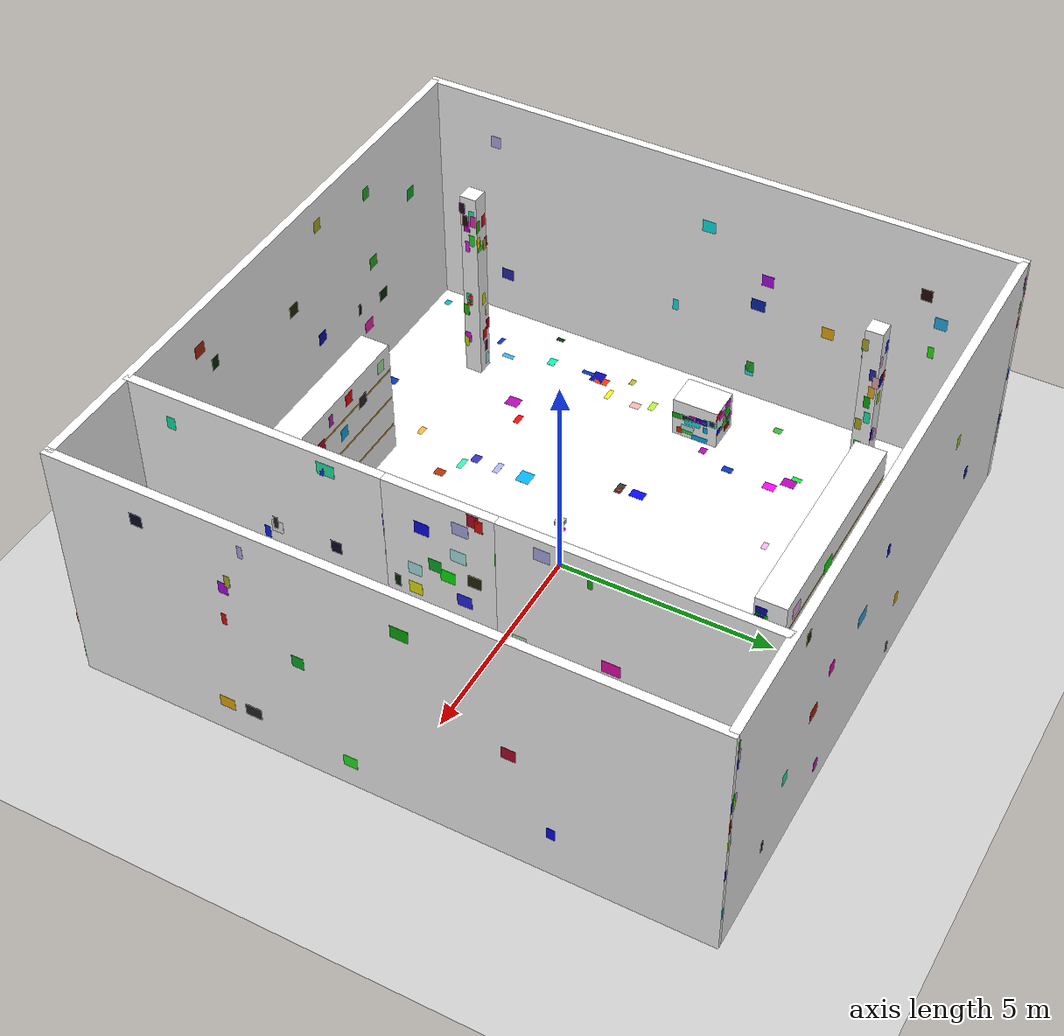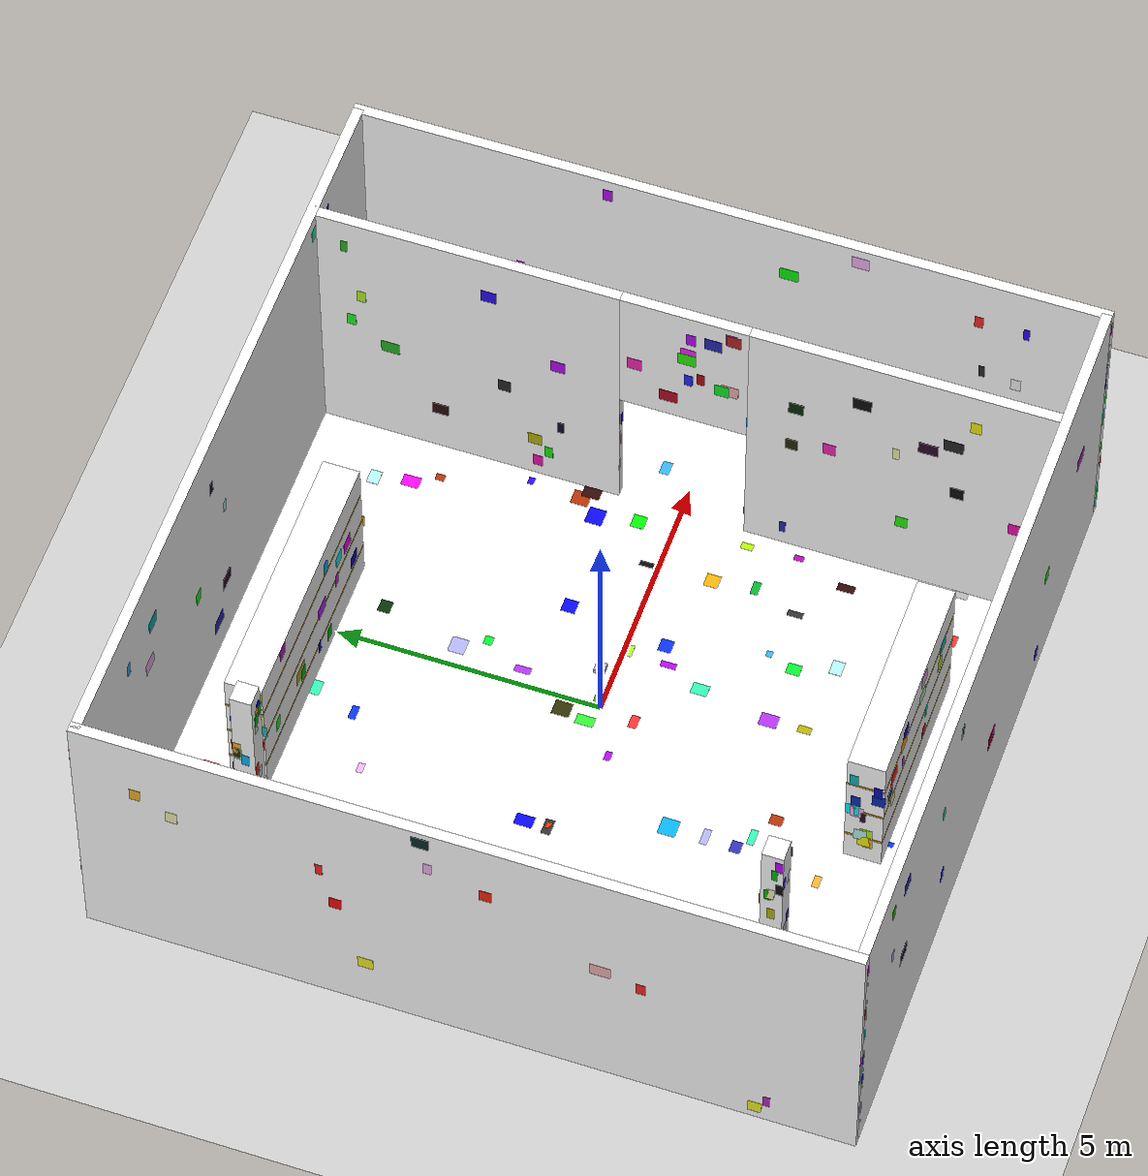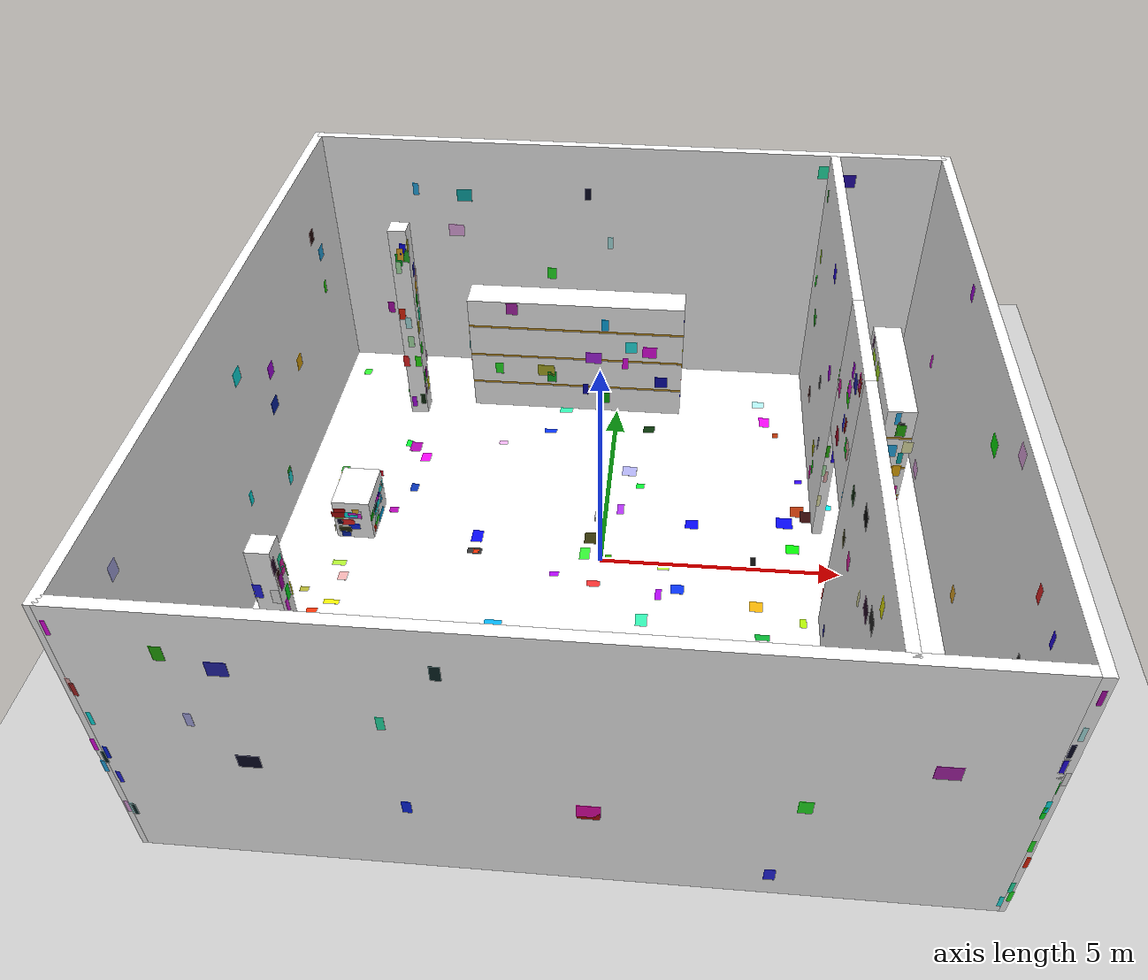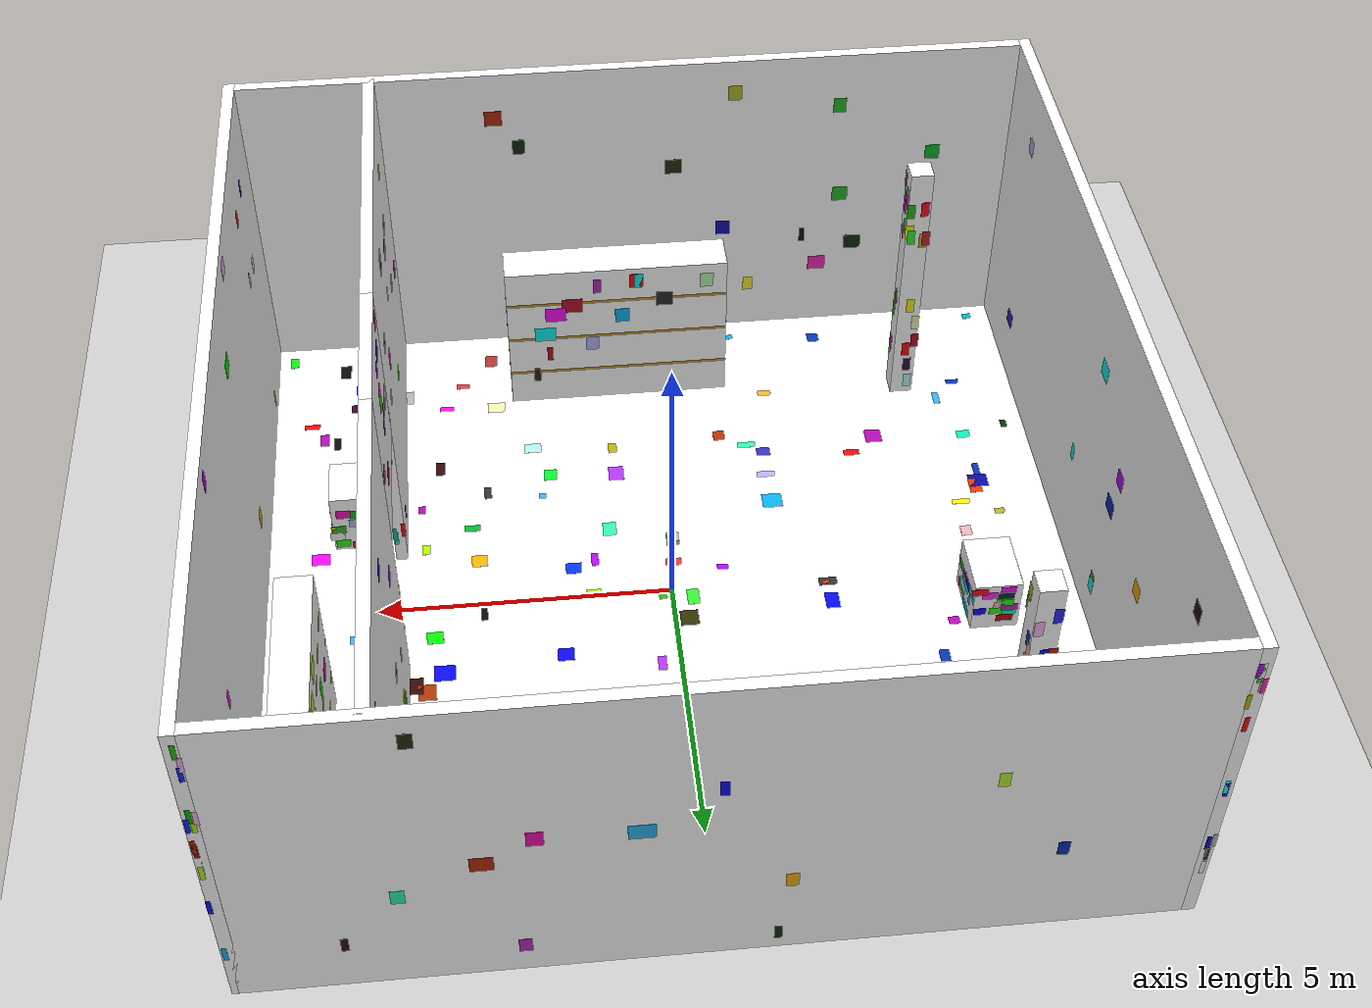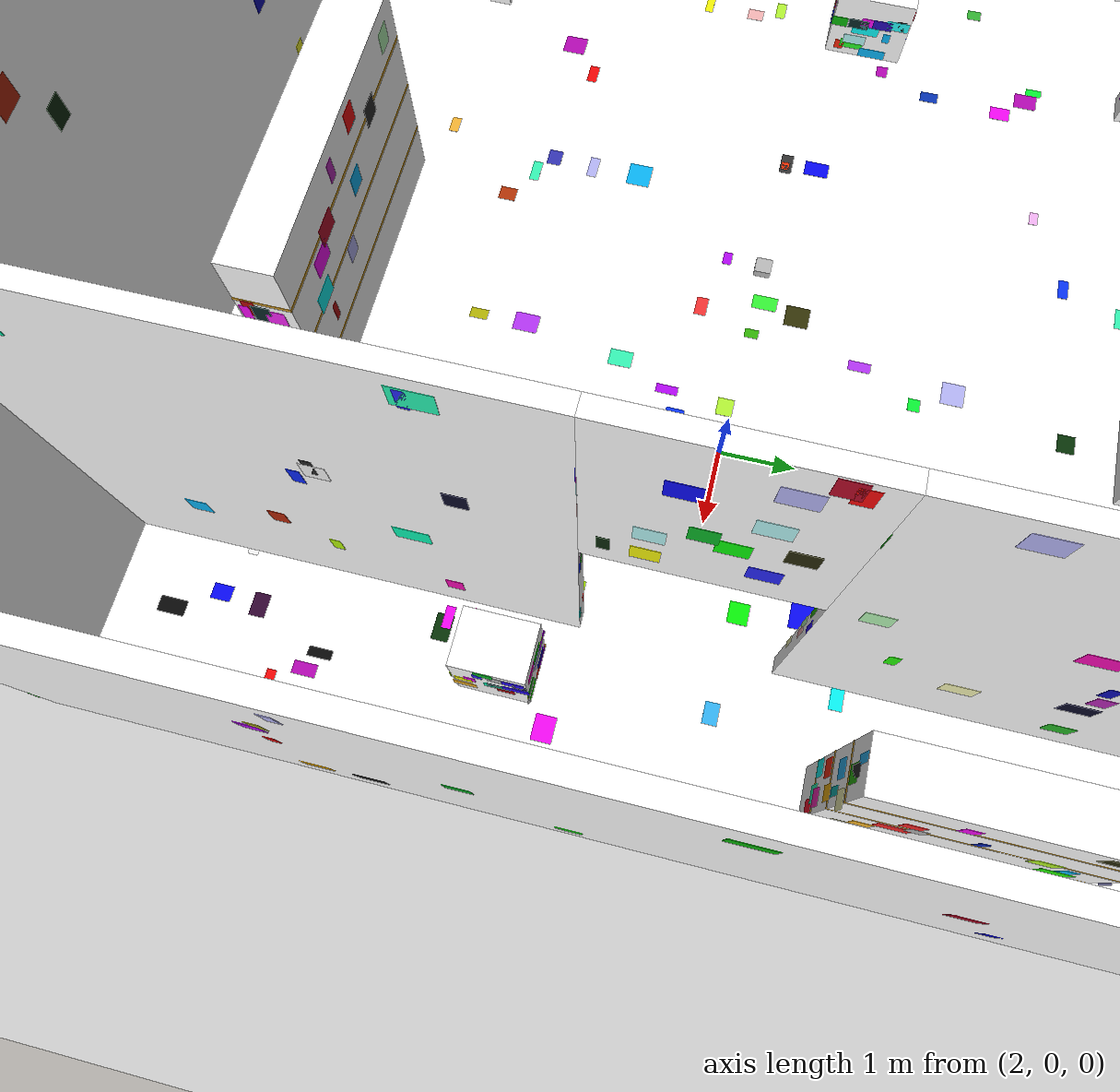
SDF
<?xml version='1.0' encoding='utf-8'?>
<sdf version="1.9">
  <world name="default">
    <physics type="ode">
      <max_step_size>0.004</max_step_size>
      <real_time_factor>1.0</real_time_factor>
      <real_time_update_rate>250</real_time_update_rate>
    </physics>
    <gravity>0 0 -9.8</gravity>
    <magnetic_field>6e-06 2.3e-05 -4.2e-05</magnetic_field>
    <atmosphere type="adiabatic" />
    <scene>
      <grid>false</grid>
      <ambient>0.4 0.4 0.4 1</ambient>
      <background>0.7 0.7 0.7 1</background>
      <shadows>true</shadows>
    </scene>
    <model name="ground_plane">
      <static>true</static>
      <link name="link">
        <collision name="collision">
          <geometry>
            <plane>
              <normal>0 0 1</normal>
              <size>1 1</size>
            </plane>
          </geometry>
          <surface>
            <friction>
              <ode />
            </friction>
            <bounce />
            <contact />
          </surface>
        </collision>
        <visual name="visual">
          <geometry>
            <plane>
              <normal>0 0 1</normal>
              <size>500 500</size>
            </plane>
          </geometry>
          <material>
            <ambient>0.8 0.8 0.8 1</ambient>
            <diffuse>0.8 0.8 0.8 1</diffuse>
            <specular>0.8 0.8 0.8 1</specular>
          </material>
        </visual>
        <pose>0 0 0 0 -0 0</pose>
        <inertial>
          <pose>0 0 0 0 -0 0</pose>
          <mass>1</mass>
          <inertia>
            <ixx>1</ixx>
            <ixy>0</ixy>
            <ixz>0</ixz>
            <iyy>1</iyy>
            <iyz>0</iyz>
            <izz>1</izz>
          </inertia>
        </inertial>
        <enable_wind>false</enable_wind>
      </link>
      <pose>0 0 0 0 -0 0</pose>
      <self_collide>false</self_collide>
    </model>
    <light name="sunUTC" type="directional">
      <pose>0 0 500 0 -0 0</pose>
      <cast_shadows>true</cast_shadows>
      <intensity>1</intensity>
      <direction>0.001 0.625 -0.78</direction>
      <diffuse>0.904 0.904 0.904 1</diffuse>
      <specular>0.271 0.271 0.271 1</specular>
      <attenuation>
        <range>2000</range>
        <linear>0</linear>
        <constant>1</constant>
        <quadratic>0</quadratic>
      </attenuation>
      <spot>
        <inner_angle>0</inner_angle>
        <outer_angle>0</outer_angle>
        <falloff>0</falloff>
      </spot>
    </light>
    <spherical_coordinates>
      <surface_model>EARTH_WGS84</surface_model>
      <world_frame_orientation>ENU</world_frame_orientation>
      <latitude_deg>47.397971057728974</latitude_deg>
      <longitude_deg> 8.546163739800146</longitude_deg>
      <elevation>0</elevation>
    </spherical_coordinates>
  <include><uri>model://vio_motion_carrier</uri><name>vio_motion_carrier</name><pose>0 0 1.3 0 0 0</pose></include><model name="wall_east"><static>true</static><pose>7 0 3 0 0 0</pose><link name="structure"><collision name="collision"><pose>0 0 0 0 0 0</pose><geometry><box><size>0.2 14.2 6</size></box></geometry></collision><visual name="surface"><pose>0 0 0 0 0 0</pose><geometry><box><size>0.2 14.2 6</size></box></geometry><material><ambient>1 1 1 1</ambient><diffuse>1 1 1 1</diffuse><pbr><metal><albedo_map>model://warehouse_textures/materials/textures/wall_east.png</albedo_map><metalness>0</metalness><roughness>1</roughness></metal></pbr></material></visual><visual name="feature_0_0"><pose>-0.10200000000000001 3.9178357231538863 -0.23942794925580735 0 0 0</pose><geometry><box><size>0.004 0.14189132276210312 0.3</size></box></geometry><material><ambient>0.95 0.15 0.95 1</ambient><diffuse>0.95 0.15 0.95 1</diffuse></material></visual><visual name="feature_0_1"><pose>-0.10200000000000001 2.248544532041607 2.597786841049812 0 0 0</pose><geometry><box><size>0.004 0.185155461414554 0.3</size></box></geometry><material><ambient>0.7 0.04 0.95 1</ambient><diffuse>0.7 0.04 0.95 1</diffuse></material></visual><visual name="feature_0_2"><pose>-0.10200000000000001 -5.159789778848193 -2.6235959311520105 0 0 0</pose><geometry><box><size>0.004 0.10792435688912158 0.3</size></box></geometry><material><ambient>0.95 0.95 0.15 1</ambient><diffuse>0.95 0.95 0.15 1</diffuse></material></visual><visual name="feature_0_3"><pose>-0.10200000000000001 -1.1770367301604088 1.7315249909807306 0 0 0</pose><geometry><box><size>0.004 0.3598786949216656 0.3</size></box></geometry><material><ambient>0.04 0.95 0.04 1</ambient><diffuse>0.04 0.95 0.04 1</diffuse></material></visual><visual name="feature_0_4"><pose>-0.10200000000000001 -5.601512003683719 1.886318854560181 0 0 0</pose><geometry><box><size>0.004 0.11264673118302052 0.3</size></box></geometry><material><ambient>0.15 0.04 0.95 1</ambient><diffuse>0.15 0.04 0.95 1</diffuse></material></visual><visual name="feature_0_5"><pose>-0.10200000000000001 -2.4866485925921693 2.643267252773019 0 0 0</pose><geometry><box><size>0.004 0.3289600401103557 0.3</size></box></geometry><material><ambient>0.95 0.7 0.95 1</ambient><diffuse>0.95 0.7 0.95 1</diffuse></material></visual><visual name="feature_0_6"><pose>-0.10200000000000001 5.863397269165957 -2.3947577388200374 0 0 0</pose><geometry><box><size>0.004 0.2095861165336038 0.3</size></box></geometry><material><ambient>0.95 0.04 0.95 1</ambient><diffuse>0.95 0.04 0.95 1</diffuse></material></visual><visual name="feature_0_7"><pose>-0.10200000000000001 3.1347513125314146 -2.6983757329268823 0 0 0</pose><geometry><box><size>0.004 0.38176930140246534 0.3</size></box></geometry><material><ambient>0.95 0.7 0.95 1</ambient><diffuse>0.95 0.7 0.95 1</diffuse></material></visual><visual name="feature_0_8"><pose>-0.10200000000000001 -5.470990840412469 0.3186491958921458 0 0 0</pose><geometry><box><size>0.004 0.18813824413297156 0.3</size></box></geometry><material><ambient>0.95 0.95 0.95 1</ambient><diffuse>0.95 0.95 0.95 1</diffuse></material></visual><visual name="feature_0_9"><pose>-0.10200000000000001 -4.830854888757945 0.4499981496416776 0 0 0</pose><geometry><box><size>0.004 0.10737702104862838 0.3</size></box></geometry><material><ambient>0.15 0.15 0.15 1</ambient><diffuse>0.15 0.15 0.15 1</diffuse></material></visual><visual name="feature_0_10"><pose>-0.10200000000000001 -4.715888096258629 1.8814669264913046 0 0 0</pose><geometry><box><size>0.004 0.1619836867270691 0.3</size></box></geometry><material><ambient>0.95 0.15 0.15 1</ambient><diffuse>0.95 0.15 0.15 1</diffuse></material></visual><visual name="feature_0_11"><pose>-0.10200000000000001 -1.3653618908001155 -1.880458354740901 0 0 0</pose><geometry><box><size>0.004 0.2429496896069118 0.3</size></box></geometry><material><ambient>0.95 0.7 0.15 1</ambient><diffuse>0.95 0.7 0.15 1</diffuse></material></visual><visual name="feature_1_0"><pose>0.10200000000000001 -3.215207384766206 1.3177846946540628 0 0 0</pose><geometry><box><size>0.004 0.21061888112744842 0.3</size></box></geometry><material><ambient>0.7 0.04 0.95 1</ambient><diffuse>0.7 0.04 0.95 1</diffuse></material></visual><visual name="feature_1_1"><pose>0.10200000000000001 -5.045410455985666 2.2063860207376136 0 0 0</pose><geometry><box><size>0.004 0.27513421637657054 0.3</size></box></geometry><material><ambient>0.04 0.04 0.15 1</ambient><diffuse>0.04 0.04 0.15 1</diffuse></material></visual><visual name="feature_1_2"><pose>0.10200000000000001 -3.553419336964374 -2.1259498442138915 0 0 0</pose><geometry><box><size>0.004 0.35003354443500534 0.3</size></box></geometry><material><ambient>0.95 0.7 0.04 1</ambient><diffuse>0.95 0.7 0.04 1</diffuse></material></visual><visual name="feature_1_3"><pose>0.10200000000000001 2.790867838502046 0.03241816002108777 0 0 0</pose><geometry><box><size>0.004 0.30349363258738443 0.3</size></box></geometry><material><ambient>0.7 0.04 0.15 1</ambient><diffuse>0.7 0.04 0.15 1</diffuse></material></visual><visual name="feature_1_4"><pose>0.10200000000000001 -2.93062404953227 -2.057010024470475 0 0 0</pose><geometry><box><size>0.004 0.3728433332919928 0.3</size></box></geometry><material><ambient>0.15 0.15 0.15 1</ambient><diffuse>0.15 0.15 0.15 1</diffuse></material></visual><visual name="feature_1_5"><pose>0.10200000000000001 -1.694841203794203 0.07388358552824181 0 0 0</pose><geometry><box><size>0.004 0.2664336709840587 0.3</size></box></geometry><material><ambient>0.04 0.7 0.15 1</ambient><diffuse>0.04 0.7 0.15 1</diffuse></material></visual><visual name="feature_1_6"><pose>0.10200000000000001 3.6500567521704825 -1.770663625432134 0 0 0</pose><geometry><box><size>0.004 0.17514672766197945 0.3</size></box></geometry><material><ambient>0.04 0.04 0.95 1</ambient><diffuse>0.04 0.04 0.95 1</diffuse></material></visual><visual name="feature_1_7"><pose>0.10200000000000001 -3.0994695822400278 1.547897880401421 0 0 0</pose><geometry><box><size>0.004 0.1285859055925925 0.3</size></box></geometry><material><ambient>0.7 0.7 0.15 1</ambient><diffuse>0.7 0.7 0.15 1</diffuse></material></visual><visual name="feature_1_8"><pose>0.10200000000000001 -3.303723234747799 0.43109630609461114 0 0 0</pose><geometry><box><size>0.004 0.10858935532779604 0.3</size></box></geometry><material><ambient>0.95 0.04 0.04 1</ambient><diffuse>0.95 0.04 0.04 1</diffuse></material></visual><visual name="feature_1_9"><pose>0.10200000000000001 0.6269025367458987 2.0851139675306385 0 0 0</pose><geometry><box><size>0.004 0.37629751187536964 0.3</size></box></geometry><material><ambient>0.04 0.7 0.04 1</ambient><diffuse>0.04 0.7 0.04 1</diffuse></material></visual><visual name="feature_1_10"><pose>0.10200000000000001 -2.6976495073365756 2.515020477868731 0 0 0</pose><geometry><box><size>0.004 0.11310534109812008 0.3</size></box></geometry><material><ambient>0.7 0.7 0.95 1</ambient><diffuse>0.7 0.7 0.95 1</diffuse></material></visual><visual name="feature_1_11"><pose>0.10200000000000001 -0.7274036900313892 -2.2844395361407632 0 0 0</pose><geometry><box><size>0.004 0.3145879897438352 0.3</size></box></geometry><material><ambient>0.15 0.95 0.15 1</ambient><diffuse>0.15 0.95 0.15 1</diffuse></material></visual><visual name="feature_2_0"><pose>0.030321591510859933 -7.101999999999999 -2.2461099457503035 0 0 0</pose><geometry><box><size>0.06999999999999999 0.004 0.3</size></box></geometry><material><ambient>0.15 0.95 0.7 1</ambient><diffuse>0.15 0.95 0.7 1</diffuse></material></visual><visual name="feature_2_1"><pose>0.031053473420672537 -7.101999999999999 -1.020780035921137 0 0 0</pose><geometry><box><size>0.06999999999999999 0.004 0.3</size></box></geometry><material><ambient>0.15 0.95 0.15 1</ambient><diffuse>0.15 0.95 0.15 1</diffuse></material></visual><visual name="feature_2_2"><pose>0.010723683748403073 -7.101999999999999 2.5800491672008876 0 0 0</pose><geometry><box><size>0.06999999999999999 0.004 0.3</size></box></geometry><material><ambient>0.7 0.04 0.7 1</ambient><diffuse>0.7 0.04 0.7 1</diffuse></material></visual><visual name="feature_2_3"><pose>-0.047490979648707736 -7.101999999999999 1.4016530091235104 0 0 0</pose><geometry><box><size>0.06999999999999999 0.004 0.3</size></box></geometry><material><ambient>0.04 0.04 0.15 1</ambient><diffuse>0.04 0.04 0.15 1</diffuse></material></visual><visual name="feature_2_4"><pose>0.07786138472605127 -7.101999999999999 -1.4874329970574864 0 0 0</pose><geometry><box><size>0.06999999999999999 0.004 0.3</size></box></geometry><material><ambient>0.95 0.15 0.04 1</ambient><diffuse>0.95 0.15 0.04 1</diffuse></material></visual><visual name="feature_2_5"><pose>-0.018443908203377532 -7.101999999999999 -0.11889163192938623 0 0 0</pose><geometry><box><size>0.06999999999999999 0.004 0.3</size></box></geometry><material><ambient>0.04 0.95 0.15 1</ambient><diffuse>0.04 0.95 0.15 1</diffuse></material></visual><visual name="feature_2_6"><pose>-0.0020178627598053944 -7.101999999999999 1.7966251486583662 0 0 0</pose><geometry><box><size>0.06999999999999999 0.004 0.3</size></box></geometry><material><ambient>0.7 0.95 0.95 1</ambient><diffuse>0.7 0.95 0.95 1</diffuse></material></visual><visual name="feature_2_7"><pose>0.0705698958574366 -7.101999999999999 -2.5121000949316046 0 0 0</pose><geometry><box><size>0.06999999999999999 0.004 0.3</size></box></geometry><material><ambient>0.15 0.95 0.15 1</ambient><diffuse>0.15 0.95 0.15 1</diffuse></material></visual><visual name="feature_2_8"><pose>-0.037521912363465554 -7.101999999999999 -2.6973855140228866 0 0 0</pose><geometry><box><size>0.06999999999999999 0.004 0.3</size></box></geometry><material><ambient>0.15 0.95 0.95 1</ambient><diffuse>0.15 0.95 0.95 1</diffuse></material></visual><visual name="feature_2_9"><pose>0.05610463733537026 -7.101999999999999 0.7547431508411848 0 0 0</pose><geometry><box><size>0.06999999999999999 0.004 0.3</size></box></geometry><material><ambient>0.95 0.95 0.95 1</ambient><diffuse>0.95 0.95 0.95 1</diffuse></material></visual><visual name="feature_2_10"><pose>-0.04852550980525617 -7.101999999999999 1.0366485904182379 0 0 0</pose><geometry><box><size>0.06999999999999999 0.004 0.3</size></box></geometry><material><ambient>0.15 0.04 0.95 1</ambient><diffuse>0.15 0.04 0.95 1</diffuse></material></visual><visual name="feature_2_11"><pose>-0.013362612163153709 -7.101999999999999 0.03682141249163928 0 0 0</pose><geometry><box><size>0.06999999999999999 0.004 0.3</size></box></geometry><material><ambient>0.04 0.95 0.95 1</ambient><diffuse>0.04 0.95 0.95 1</diffuse></material></visual><visual name="feature_3_0"><pose>-0.030997780367746433 7.101999999999999 2.661931016307885 0 0 0</pose><geometry><box><size>0.06999999999999999 0.004 0.3</size></box></geometry><material><ambient>0.15 0.7 0.04 1</ambient><diffuse>0.15 0.7 0.04 1</diffuse></material></visual><visual name="feature_3_1"><pose>0.07141941224342348 7.101999999999999 -0.7770742994680593 0 0 0</pose><geometry><box><size>0.06999999999999999 0.004 0.3</size></box></geometry><material><ambient>0.04 0.04 0.95 1</ambient><diffuse>0.04 0.04 0.95 1</diffuse></material></visual><visual name="feature_3_2"><pose>-0.0768313318849458 7.101999999999999 1.2603403348973399 0 0 0</pose><geometry><box><size>0.06999999999999999 0.004 0.3</size></box></geometry><material><ambient>0.95 0.7 0.95 1</ambient><diffuse>0.95 0.7 0.95 1</diffuse></material></visual><visual name="feature_3_3"><pose>-0.07376981931180335 7.101999999999999 2.405054611475088 0 0 0</pose><geometry><box><size>0.06999999999999999 0.004 0.3</size></box></geometry><material><ambient>0.95 0.7 0.95 1</ambient><diffuse>0.95 0.7 0.95 1</diffuse></material></visual><visual name="feature_3_4"><pose>0.05405259903448399 7.101999999999999 1.1098649010972563 0 0 0</pose><geometry><box><size>0.06999999999999999 0.004 0.3</size></box></geometry><material><ambient>0.04 0.15 0.95 1</ambient><diffuse>0.04 0.15 0.95 1</diffuse></material></visual><visual name="feature_3_5"><pose>0.05269651745658745 7.101999999999999 0.6320913630091982 0 0 0</pose><geometry><box><size>0.06999999999999999 0.004 0.3</size></box></geometry><material><ambient>0.7 0.15 0.04 1</ambient><diffuse>0.7 0.15 0.04 1</diffuse></material></visual><visual name="feature_3_6"><pose>-0.02850205260600079 7.101999999999999 1.108306751776046 0 0 0</pose><geometry><box><size>0.06999999999999999 0.004 0.3</size></box></geometry><material><ambient>0.7 0.95 0.04 1</ambient><diffuse>0.7 0.95 0.04 1</diffuse></material></visual><visual name="feature_3_7"><pose>0.03851074568325473 7.101999999999999 0.5397746193927548 0 0 0</pose><geometry><box><size>0.06999999999999999 0.004 0.3</size></box></geometry><material><ambient>0.7 0.04 0.04 1</ambient><diffuse>0.7 0.04 0.04 1</diffuse></material></visual><visual name="feature_3_8"><pose>-0.046063226050189046 7.101999999999999 2.2045703281883897 0 0 0</pose><geometry><box><size>0.06999999999999999 0.004 0.3</size></box></geometry><material><ambient>0.04 0.15 0.95 1</ambient><diffuse>0.04 0.15 0.95 1</diffuse></material></visual><visual name="feature_3_9"><pose>0.039816054668243256 7.101999999999999 -1.9539020883463913 0 0 0</pose><geometry><box><size>0.06999999999999999 0.004 0.3</size></box></geometry><material><ambient>0.04 0.7 0.95 1</ambient><diffuse>0.04 0.7 0.95 1</diffuse></material></visual><visual name="feature_3_10"><pose>0.003942239389446975 7.101999999999999 1.3023531107784683 0 0 0</pose><geometry><box><size>0.06999999999999999 0.004 0.3</size></box></geometry><material><ambient>0.04 0.7 0.04 1</ambient><diffuse>0.04 0.7 0.04 1</diffuse></material></visual><visual name="feature_3_11"><pose>0.041140976275479677 7.101999999999999 0.03912102621192526 0 0 0</pose><geometry><box><size>0.06999999999999999 0.004 0.3</size></box></geometry><material><ambient>0.7 0.95 0.15 1</ambient><diffuse>0.7 0.95 0.15 1</diffuse></material></visual></link></model><model name="wall_west"><static>true</static><pose>-7 0 3 0 0 0</pose><link name="structure"><collision name="collision"><pose>0 0 0 0 0 0</pose><geometry><box><size>0.2 14.2 6</size></box></geometry></collision><visual name="surface"><pose>0 0 0 0 0 0</pose><geometry><box><size>0.2 14.2 6</size></box></geometry><material><ambient>1 1 1 1</ambient><diffuse>1 1 1 1</diffuse><pbr><metal><albedo_map>model://warehouse_textures/materials/textures/wall_west.png</albedo_map><metalness>0</metalness><roughness>1</roughness></metal></pbr></material></visual><visual name="feature_0_0"><pose>-0.10200000000000001 -2.4399980160481607 0.3020556819575564 0 0 0</pose><geometry><box><size>0.004 0.3915892769131405 0.3</size></box></geometry><material><ambient>0.95 0.7 0.7 1</ambient><diffuse>0.95 0.7 0.7 1</diffuse></material></visual><visual name="feature_0_1"><pose>-0.10200000000000001 -5.469895380556496 -2.391834382314927 0 0 0</pose><geometry><box><size>0.004 0.12230098529325793 0.3</size></box></geometry><material><ambient>0.7 0.15 0.7 1</ambient><diffuse>0.7 0.15 0.7 1</diffuse></material></visual><visual name="feature_0_2"><pose>-0.10200000000000001 -0.3922380446730216 1.619069457699612 0 0 0</pose><geometry><box><size>0.004 0.21475900137104384 0.3</size></box></geometry><material><ambient>0.95 0.15 0.04 1</ambient><diffuse>0.95 0.15 0.04 1</diffuse></material></visual><visual name="feature_0_3"><pose>-0.10200000000000001 5.303675404785616 1.1770575741565459 0 0 0</pose><geometry><box><size>0.004 0.21581993688109666 0.3</size></box></geometry><material><ambient>0.95 0.95 0.7 1</ambient><diffuse>0.95 0.95 0.7 1</diffuse></material></visual><visual name="feature_0_4"><pose>-0.10200000000000001 1.857140336990156 -1.7308972042441964 0 0 0</pose><geometry><box><size>0.004 0.2853784063809313 0.3</size></box></geometry><material><ambient>0.95 0.95 0.15 1</ambient><diffuse>0.95 0.95 0.15 1</diffuse></material></visual><visual name="feature_0_5"><pose>-0.10200000000000001 -5.257246740748468 -2.6705996857956467 0 0 0</pose><geometry><box><size>0.004 0.24765341213349165 0.3</size></box></geometry><material><ambient>0.95 0.95 0.15 1</ambient><diffuse>0.95 0.95 0.15 1</diffuse></material></visual><visual name="feature_0_6"><pose>-0.10200000000000001 0.6406034004180539 1.9547910802914412 0 0 0</pose><geometry><box><size>0.004 0.15719647215785326 0.3</size></box></geometry><material><ambient>0.95 0.7 0.95 1</ambient><diffuse>0.95 0.7 0.95 1</diffuse></material></visual><visual name="feature_0_7"><pose>-0.10200000000000001 5.950152480403291 1.565054231273173 0 0 0</pose><geometry><box><size>0.004 0.19411906627216463 0.3</size></box></geometry><material><ambient>0.95 0.7 0.15 1</ambient><diffuse>0.95 0.7 0.15 1</diffuse></material></visual><visual name="feature_0_8"><pose>-0.10200000000000001 -3.170714427656762 0.08628925859680692 0 0 0</pose><geometry><box><size>0.004 0.16883432869781856 0.3</size></box></geometry><material><ambient>0.95 0.15 0.15 1</ambient><diffuse>0.95 0.15 0.15 1</diffuse></material></visual><visual name="feature_0_9"><pose>-0.10200000000000001 2.361354726646524 -0.04804159367639427 0 0 0</pose><geometry><box><size>0.004 0.23035874622938698 0.3</size></box></geometry><material><ambient>0.95 0.04 0.04 1</ambient><diffuse>0.95 0.04 0.04 1</diffuse></material></visual><visual name="feature_0_10"><pose>-0.10200000000000001 0.7603342701338871 2.6998069709910046 0 0 0</pose><geometry><box><size>0.004 0.32312808295700146 0.3</size></box></geometry><material><ambient>0.04 0.15 0.15 1</ambient><diffuse>0.04 0.15 0.15 1</diffuse></material></visual><visual name="feature_0_11"><pose>-0.10200000000000001 2.6294569060722415 0.9065385129955983 0 0 0</pose><geometry><box><size>0.004 0.1335520405367582 0.3</size></box></geometry><material><ambient>0.95 0.15 0.15 1</ambient><diffuse>0.95 0.15 0.15 1</diffuse></material></visual><visual name="feature_1_0"><pose>0.10200000000000001 -5.399512206344948 1.8735425798313612 0 0 0</pose><geometry><box><size>0.004 0.2418432798297935 0.3</size></box></geometry><material><ambient>0.7 0.7 0.95 1</ambient><diffuse>0.7 0.7 0.95 1</diffuse></material></visual><visual name="feature_1_1"><pose>0.10200000000000001 5.113483547642439 1.4560023157235351 0 0 0</pose><geometry><box><size>0.004 0.2602024849089039 0.3</size></box></geometry><material><ambient>0.15 0.04 0.04 1</ambient><diffuse>0.15 0.04 0.04 1</diffuse></material></visual><visual name="feature_1_2"><pose>0.10200000000000001 0.003909557750823467 1.4239754996089058 0 0 0</pose><geometry><box><size>0.004 0.3210840017837414 0.3</size></box></geometry><material><ambient>0.04 0.95 0.95 1</ambient><diffuse>0.04 0.95 0.95 1</diffuse></material></visual><visual name="feature_1_3"><pose>0.10200000000000001 -5.1558248896728704 -1.8593190721477653 0 0 0</pose><geometry><box><size>0.004 0.31464795694989345 0.3</size></box></geometry><material><ambient>0.15 0.15 0.7 1</ambient><diffuse>0.15 0.15 0.7 1</diffuse></material></visual><visual name="feature_1_4"><pose>0.10200000000000001 5.510971681542455 0.8155410828662855 0 0 0</pose><geometry><box><size>0.004 0.28785485438118963 0.3</size></box></geometry><material><ambient>0.15 0.7 0.95 1</ambient><diffuse>0.15 0.7 0.95 1</diffuse></material></visual><visual name="feature_1_5"><pose>0.10200000000000001 1.2185686625670114 -2.2565620411603713 0 0 0</pose><geometry><box><size>0.004 0.2053780267001708 0.3</size></box></geometry><material><ambient>0.15 0.95 0.95 1</ambient><diffuse>0.15 0.95 0.95 1</diffuse></material></visual><visual name="feature_1_6"><pose>0.10200000000000001 1.2313417950706773 -2.153556797394641 0 0 0</pose><geometry><box><size>0.004 0.18775018185270168 0.3</size></box></geometry><material><ambient>0.15 0.7 0.15 1</ambient><diffuse>0.15 0.7 0.15 1</diffuse></material></visual><visual name="feature_1_7"><pose>0.10200000000000001 1.4967319646772026 0.4535006445750165 0 0 0</pose><geometry><box><size>0.004 0.27968708074921705 0.3</size></box></geometry><material><ambient>0.7 0.04 0.95 1</ambient><diffuse>0.7 0.04 0.95 1</diffuse></material></visual><visual name="feature_1_8"><pose>0.10200000000000001 -0.7172996017168378 -1.0624026120775714 0 0 0</pose><geometry><box><size>0.004 0.14363849470104317 0.3</size></box></geometry><material><ambient>0.04 0.95 0.95 1</ambient><diffuse>0.04 0.95 0.95 1</diffuse></material></visual><visual name="feature_1_9"><pose>0.10200000000000001 5.380406554997474 -0.02972041102786349 0 0 0</pose><geometry><box><size>0.004 0.13555540260375187 0.3</size></box></geometry><material><ambient>0.15 0.95 0.04 1</ambient><diffuse>0.15 0.95 0.04 1</diffuse></material></visual><visual name="feature_1_10"><pose>0.10200000000000001 1.3121269055660543 -0.29682539251616236 0 0 0</pose><geometry><box><size>0.004 0.343418644844803 0.3</size></box></geometry><material><ambient>0.04 0.15 0.7 1</ambient><diffuse>0.04 0.15 0.7 1</diffuse></material></visual><visual name="feature_1_11"><pose>0.10200000000000001 3.0123426507784385 -0.44656640002336223 0 0 0</pose><geometry><box><size>0.004 0.2870872941407462 0.3</size></box></geometry><material><ambient>0.95 0.7 0.04 1</ambient><diffuse>0.95 0.7 0.04 1</diffuse></material></visual><visual name="feature_2_0"><pose>-0.07991013242355217 -7.101999999999999 -0.7561266371148745 0 0 0</pose><geometry><box><size>0.06999999999999999 0.004 0.3</size></box></geometry><material><ambient>0.15 0.7 0.95 1</ambient><diffuse>0.15 0.7 0.95 1</diffuse></material></visual><visual name="feature_2_1"><pose>0.03669403453833113 -7.101999999999999 1.1883494590325112 0 0 0</pose><geometry><box><size>0.06999999999999999 0.004 0.3</size></box></geometry><material><ambient>0.7 0.15 0.15 1</ambient><diffuse>0.7 0.15 0.15 1</diffuse></material></visual><visual name="feature_2_2"><pose>0.08337135820517337 -7.101999999999999 -1.0278463338228963 0 0 0</pose><geometry><box><size>0.06999999999999999 0.004 0.3</size></box></geometry><material><ambient>0.15 0.15 0.95 1</ambient><diffuse>0.15 0.15 0.95 1</diffuse></material></visual><visual name="feature_2_3"><pose>-0.07619952582028745 -7.101999999999999 -0.1836294385403905 0 0 0</pose><geometry><box><size>0.06999999999999999 0.004 0.3</size></box></geometry><material><ambient>0.95 0.04 0.95 1</ambient><diffuse>0.95 0.04 0.95 1</diffuse></material></visual><visual name="feature_2_4"><pose>-0.03448234247563747 -7.101999999999999 -1.883475053466344 0 0 0</pose><geometry><box><size>0.06999999999999999 0.004 0.3</size></box></geometry><material><ambient>0.95 0.7 0.95 1</ambient><diffuse>0.95 0.7 0.95 1</diffuse></material></visual><visual name="feature_2_5"><pose>0.01170848448713191 -7.101999999999999 1.2914774825609996 0 0 0</pose><geometry><box><size>0.06999999999999999 0.004 0.3</size></box></geometry><material><ambient>0.95 0.7 0.7 1</ambient><diffuse>0.95 0.7 0.7 1</diffuse></material></visual><visual name="feature_2_6"><pose>0.07116156059138791 -7.101999999999999 0.4999555629831667 0 0 0</pose><geometry><box><size>0.06999999999999999 0.004 0.3</size></box></geometry><material><ambient>0.04 0.95 0.95 1</ambient><diffuse>0.04 0.95 0.95 1</diffuse></material></visual><visual name="feature_2_7"><pose>-0.007971952722534037 -7.101999999999999 -0.497226688570517 0 0 0</pose><geometry><box><size>0.06999999999999999 0.004 0.3</size></box></geometry><material><ambient>0.04 0.15 0.15 1</ambient><diffuse>0.04 0.15 0.15 1</diffuse></material></visual><visual name="feature_2_8"><pose>0.06343480146830573 -7.101999999999999 -0.3664382893202238 0 0 0</pose><geometry><box><size>0.06999999999999999 0.004 0.3</size></box></geometry><material><ambient>0.04 0.15 0.95 1</ambient><diffuse>0.04 0.15 0.95 1</diffuse></material></visual><visual name="feature_2_9"><pose>0.06431576085093442 -7.101999999999999 -1.953412984633799 0 0 0</pose><geometry><box><size>0.06999999999999999 0.004 0.3</size></box></geometry><material><ambient>0.04 0.15 0.15 1</ambient><diffuse>0.04 0.15 0.15 1</diffuse></material></visual><visual name="feature_2_10"><pose>0.03253761486497819 -7.101999999999999 -1.9315518510024878 0 0 0</pose><geometry><box><size>0.06999999999999999 0.004 0.3</size></box></geometry><material><ambient>0.7 0.95 0.95 1</ambient><diffuse>0.7 0.95 0.95 1</diffuse></material></visual><visual name="feature_2_11"><pose>0.07052570471376453 -7.101999999999999 2.5447842467985975 0 0 0</pose><geometry><box><size>0.06999999999999999 0.004 0.3</size></box></geometry><material><ambient>0.95 0.04 0.95 1</ambient><diffuse>0.95 0.04 0.95 1</diffuse></material></visual><visual name="feature_3_0"><pose>0.006474535881474092 7.101999999999999 2.5459525278538377 0 0 0</pose><geometry><box><size>0.06999999999999999 0.004 0.3</size></box></geometry><material><ambient>0.95 0.95 0.95 1</ambient><diffuse>0.95 0.95 0.95 1</diffuse></material></visual><visual name="feature_3_1"><pose>-0.017878671191996973 7.101999999999999 -1.581706155410074 0 0 0</pose><geometry><box><size>0.06999999999999999 0.004 0.3</size></box></geometry><material><ambient>0.15 0.15 0.15 1</ambient><diffuse>0.15 0.15 0.15 1</diffuse></material></visual><visual name="feature_3_2"><pose>0.017576754217694654 7.101999999999999 1.426769199673192 0 0 0</pose><geometry><box><size>0.06999999999999999 0.004 0.3</size></box></geometry><material><ambient>0.95 0.04 0.04 1</ambient><diffuse>0.95 0.04 0.04 1</diffuse></material></visual><visual name="feature_3_3"><pose>0.006894885509430432 7.101999999999999 -1.2993058035159568 0 0 0</pose><geometry><box><size>0.06999999999999999 0.004 0.3</size></box></geometry><material><ambient>0.04 0.04 0.7 1</ambient><diffuse>0.04 0.04 0.7 1</diffuse></material></visual><visual name="feature_3_4"><pose>0.016524127904333108 7.101999999999999 2.4506980377521455 0 0 0</pose><geometry><box><size>0.06999999999999999 0.004 0.3</size></box></geometry><material><ambient>0.04 0.95 0.15 1</ambient><diffuse>0.04 0.95 0.15 1</diffuse></material></visual><visual name="feature_3_5"><pose>-0.06561015559391227 7.101999999999999 2.2327862794091535 0 0 0</pose><geometry><box><size>0.06999999999999999 0.004 0.3</size></box></geometry><material><ambient>0.95 0.15 0.7 1</ambient><diffuse>0.95 0.15 0.7 1</diffuse></material></visual><visual name="feature_3_6"><pose>0.0532409292346545 7.101999999999999 2.5385344094423035 0 0 0</pose><geometry><box><size>0.06999999999999999 0.004 0.3</size></box></geometry><material><ambient>0.7 0.04 0.95 1</ambient><diffuse>0.7 0.04 0.95 1</diffuse></material></visual><visual name="feature_3_7"><pose>0.08374873507306586 7.101999999999999 1.9144505125081581 0 0 0</pose><geometry><box><size>0.06999999999999999 0.004 0.3</size></box></geometry><material><ambient>0.7 0.7 0.04 1</ambient><diffuse>0.7 0.7 0.04 1</diffuse></material></visual><visual name="feature_3_8"><pose>-0.07185214656855918 7.101999999999999 -1.2465015885113353 0 0 0</pose><geometry><box><size>0.06999999999999999 0.004 0.3</size></box></geometry><material><ambient>0.7 0.7 0.7 1</ambient><diffuse>0.7 0.7 0.7 1</diffuse></material></visual><visual name="feature_3_9"><pose>-0.006473240006751202 7.101999999999999 -0.03164831225535769 0 0 0</pose><geometry><box><size>0.06999999999999999 0.004 0.3</size></box></geometry><material><ambient>0.15 0.04 0.95 1</ambient><diffuse>0.15 0.04 0.95 1</diffuse></material></visual><visual name="feature_3_10"><pose>0.001973377840803467 7.101999999999999 0.02778293553877731 0 0 0</pose><geometry><box><size>0.06999999999999999 0.004 0.3</size></box></geometry><material><ambient>0.15 0.95 0.95 1</ambient><diffuse>0.15 0.95 0.95 1</diffuse></material></visual><visual name="feature_3_11"><pose>-0.017681620398762657 7.101999999999999 -1.9031852857431533 0 0 0</pose><geometry><box><size>0.06999999999999999 0.004 0.3</size></box></geometry><material><ambient>0.95 0.95 0.95 1</ambient><diffuse>0.95 0.95 0.95 1</diffuse></material></visual></link></model><model name="wall_north"><static>true</static><pose>0 7 3 0 0 0</pose><link name="structure"><collision name="collision"><pose>0 0 0 0 0 0</pose><geometry><box><size>14 0.2 6</size></box></geometry></collision><visual name="surface"><pose>0 0 0 0 0 0</pose><geometry><box><size>14 0.2 6</size></box></geometry><material><ambient>1 1 1 1</ambient><diffuse>1 1 1 1</diffuse><pbr><metal><albedo_map>model://warehouse_textures/materials/textures/wall_north.png</albedo_map><metalness>0</metalness><roughness>1</roughness></metal></pbr></material></visual><visual name="feature_0_0"><pose>-7.002 0.05740399791249655 0.7025036751725389 0 0 0</pose><geometry><box><size>0.004 0.06999999999999999 0.3</size></box></geometry><material><ambient>0.95 0.15 0.04 1</ambient><diffuse>0.95 0.15 0.04 1</diffuse></material></visual><visual name="feature_0_1"><pose>-7.002 0.07854383397790567 2.2538727229539655 0 0 0</pose><geometry><box><size>0.004 0.06999999999999999 0.3</size></box></geometry><material><ambient>0.04 0.04 0.04 1</ambient><diffuse>0.04 0.04 0.04 1</diffuse></material></visual><visual name="feature_0_2"><pose>-7.002 -0.050748433006339494 2.5971247547386653 0 0 0</pose><geometry><box><size>0.004 0.06999999999999999 0.3</size></box></geometry><material><ambient>0.7 0.15 0.7 1</ambient><diffuse>0.7 0.15 0.7 1</diffuse></material></visual><visual name="feature_0_3"><pose>-7.002 0.07319288169317882 -1.4738854698375377 0 0 0</pose><geometry><box><size>0.004 0.06999999999999999 0.3</size></box></geometry><material><ambient>0.15 0.7 0.7 1</ambient><diffuse>0.15 0.7 0.7 1</diffuse></material></visual><visual name="feature_0_4"><pose>-7.002 0.02419814084115028 0.8926612303974193 0 0 0</pose><geometry><box><size>0.004 0.06999999999999999 0.3</size></box></geometry><material><ambient>0.7 0.7 0.7 1</ambient><diffuse>0.7 0.7 0.7 1</diffuse></material></visual><visual name="feature_0_5"><pose>-7.002 -0.01561939305149082 -1.4772465535562793 0 0 0</pose><geometry><box><size>0.004 0.06999999999999999 0.3</size></box></geometry><material><ambient>0.95 0.7 0.7 1</ambient><diffuse>0.95 0.7 0.7 1</diffuse></material></visual><visual name="feature_0_6"><pose>-7.002 -0.03776069096096815 2.3207784220638707 0 0 0</pose><geometry><box><size>0.004 0.06999999999999999 0.3</size></box></geometry><material><ambient>0.15 0.95 0.04 1</ambient><diffuse>0.15 0.95 0.04 1</diffuse></material></visual><visual name="feature_0_7"><pose>-7.002 -0.06937758499440702 2.1350625783068047 0 0 0</pose><geometry><box><size>0.004 0.06999999999999999 0.3</size></box></geometry><material><ambient>0.7 0.04 0.7 1</ambient><diffuse>0.7 0.04 0.7 1</diffuse></material></visual><visual name="feature_0_8"><pose>-7.002 -0.005494628617869715 0.6742356440841863 0 0 0</pose><geometry><box><size>0.004 0.06999999999999999 0.3</size></box></geometry><material><ambient>0.15 0.7 0.15 1</ambient><diffuse>0.15 0.7 0.15 1</diffuse></material></visual><visual name="feature_0_9"><pose>-7.002 0.06492972701412435 0.06277169505868763 0 0 0</pose><geometry><box><size>0.004 0.06999999999999999 0.3</size></box></geometry><material><ambient>0.7 0.04 0.04 1</ambient><diffuse>0.7 0.04 0.04 1</diffuse></material></visual><visual name="feature_0_10"><pose>-7.002 0.03187456365895723 1.5432750982797598 0 0 0</pose><geometry><box><size>0.004 0.06999999999999999 0.3</size></box></geometry><material><ambient>0.7 0.15 0.95 1</ambient><diffuse>0.7 0.15 0.95 1</diffuse></material></visual><visual name="feature_0_11"><pose>-7.002 -0.045730328586155645 -0.6271222171113213 0 0 0</pose><geometry><box><size>0.004 0.06999999999999999 0.3</size></box></geometry><material><ambient>0.95 0.7 0.04 1</ambient><diffuse>0.95 0.7 0.04 1</diffuse></material></visual><visual name="feature_1_0"><pose>7.002 0.03522446831923705 1.2735736602150443 0 0 0</pose><geometry><box><size>0.004 0.06999999999999999 0.3</size></box></geometry><material><ambient>0.04 0.04 0.15 1</ambient><diffuse>0.04 0.04 0.15 1</diffuse></material></visual><visual name="feature_1_1"><pose>7.002 -0.0469776455105717 0.9024821809548937 0 0 0</pose><geometry><box><size>0.004 0.06999999999999999 0.3</size></box></geometry><material><ambient>0.04 0.04 0.04 1</ambient><diffuse>0.04 0.04 0.04 1</diffuse></material></visual><visual name="feature_1_2"><pose>7.002 -0.08157546014427244 1.9879936328129517 0 0 0</pose><geometry><box><size>0.004 0.06999999999999999 0.3</size></box></geometry><material><ambient>0.04 0.95 0.95 1</ambient><diffuse>0.04 0.95 0.95 1</diffuse></material></visual><visual name="feature_1_3"><pose>7.002 -0.0359489471036907 -1.746866420652428 0 0 0</pose><geometry><box><size>0.004 0.06999999999999999 0.3</size></box></geometry><material><ambient>0.7 0.7 0.95 1</ambient><diffuse>0.7 0.7 0.95 1</diffuse></material></visual><visual name="feature_1_4"><pose>7.002 0.047225878332427765 -0.38483222295266684 0 0 0</pose><geometry><box><size>0.004 0.06999999999999999 0.3</size></box></geometry><material><ambient>0.15 0.95 0.95 1</ambient><diffuse>0.15 0.95 0.95 1</diffuse></material></visual><visual name="feature_1_5"><pose>7.002 -0.00879384942152947 -1.5133206622587514 0 0 0</pose><geometry><box><size>0.004 0.06999999999999999 0.3</size></box></geometry><material><ambient>0.04 0.95 0.7 1</ambient><diffuse>0.04 0.95 0.7 1</diffuse></material></visual><visual name="feature_1_6"><pose>7.002 0.0777051902753262 0.13805254826223035 0 0 0</pose><geometry><box><size>0.004 0.06999999999999999 0.3</size></box></geometry><material><ambient>0.7 0.95 0.95 1</ambient><diffuse>0.7 0.95 0.95 1</diffuse></material></visual><visual name="feature_1_7"><pose>7.002 0.0215522584049017 0.054730310761432754 0 0 0</pose><geometry><box><size>0.004 0.06999999999999999 0.3</size></box></geometry><material><ambient>0.15 0.04 0.7 1</ambient><diffuse>0.15 0.04 0.7 1</diffuse></material></visual><visual name="feature_1_8"><pose>7.002 0.03341609340743347 0.1774305171533701 0 0 0</pose><geometry><box><size>0.004 0.06999999999999999 0.3</size></box></geometry><material><ambient>0.04 0.95 0.15 1</ambient><diffuse>0.04 0.95 0.15 1</diffuse></material></visual><visual name="feature_1_9"><pose>7.002 -0.018324491610264435 2.0514677380727084 0 0 0</pose><geometry><box><size>0.004 0.06999999999999999 0.3</size></box></geometry><material><ambient>0.04 0.04 0.95 1</ambient><diffuse>0.04 0.04 0.95 1</diffuse></material></visual><visual name="feature_1_10"><pose>7.002 -0.021048834978753914 1.1123216580747055 0 0 0</pose><geometry><box><size>0.004 0.06999999999999999 0.3</size></box></geometry><material><ambient>0.15 0.15 0.15 1</ambient><diffuse>0.15 0.15 0.15 1</diffuse></material></visual><visual name="feature_1_11"><pose>7.002 -0.020994369180686576 -0.9567640208396138 0 0 0</pose><geometry><box><size>0.004 0.06999999999999999 0.3</size></box></geometry><material><ambient>0.95 0.15 0.15 1</ambient><diffuse>0.95 0.15 0.15 1</diffuse></material></visual><visual name="feature_2_0"><pose>-3.7463705665134444 -0.10200000000000001 1.6719955134625675 0 0 0</pose><geometry><box><size>0.3448776181266677 0.004 0.3</size></box></geometry><material><ambient>0.04 0.7 0.7 1</ambient><diffuse>0.04 0.7 0.7 1</diffuse></material></visual><visual name="feature_2_1"><pose>-4.87564520115154 -0.10200000000000001 1.7861467148703136 0 0 0</pose><geometry><box><size>0.1276775238052339 0.004 0.3</size></box></geometry><material><ambient>0.15 0.7 0.95 1</ambient><diffuse>0.15 0.7 0.95 1</diffuse></material></visual><visual name="feature_2_2"><pose>4.841366774784601 -0.10200000000000001 -1.6677762424896379 0 0 0</pose><geometry><box><size>0.37165318680444903 0.004 0.3</size></box></geometry><material><ambient>0.95 0.04 0.04 1</ambient><diffuse>0.95 0.04 0.04 1</diffuse></material></visual><visual name="feature_2_3"><pose>-0.4796735420358935 -0.10200000000000001 -1.5064770531862461 0 0 0</pose><geometry><box><size>0.3642524153653406 0.004 0.3</size></box></geometry><material><ambient>0.15 0.04 0.15 1</ambient><diffuse>0.15 0.04 0.15 1</diffuse></material></visual><visual name="feature_2_4"><pose>-0.3446644241147494 -0.10200000000000001 0.574764268523206 0 0 0</pose><geometry><box><size>0.12782794762885477 0.004 0.3</size></box></geometry><material><ambient>0.7 0.95 0.95 1</ambient><diffuse>0.7 0.95 0.95 1</diffuse></material></visual><visual name="feature_2_5"><pose>-0.9417978065136889 -0.10200000000000001 -2.2360110182364714 0 0 0</pose><geometry><box><size>0.39611606082923 0.004 0.3</size></box></geometry><material><ambient>0.15 0.15 0.7 1</ambient><diffuse>0.15 0.15 0.7 1</diffuse></material></visual><visual name="feature_2_6"><pose>-0.8678799756750291 -0.10200000000000001 1.8241203898199858 0 0 0</pose><geometry><box><size>0.14542062047875087 0.004 0.3</size></box></geometry><material><ambient>0.04 0.04 0.15 1</ambient><diffuse>0.04 0.04 0.15 1</diffuse></material></visual><visual name="feature_2_7"><pose>-1.7576227178929766 -0.10200000000000001 -0.32648244934040216 0 0 0</pose><geometry><box><size>0.2118109170490709 0.004 0.3</size></box></geometry><material><ambient>0.15 0.95 0.15 1</ambient><diffuse>0.15 0.95 0.15 1</diffuse></material></visual><visual name="feature_2_8"><pose>-5.854685572844656 -0.10200000000000001 -1.5402346275416843 0 0 0</pose><geometry><box><size>0.1568972919745467 0.004 0.3</size></box></geometry><material><ambient>0.7 0.04 0.7 1</ambient><diffuse>0.7 0.04 0.7 1</diffuse></material></visual><visual name="feature_2_9"><pose>-4.002903347911203 -0.10200000000000001 0.7465170212490646 0 0 0</pose><geometry><box><size>0.3693178337186339 0.004 0.3</size></box></geometry><material><ambient>0.95 0.7 0.95 1</ambient><diffuse>0.95 0.7 0.95 1</diffuse></material></visual><visual name="feature_2_10"><pose>4.446334056606893 -0.10200000000000001 2.597757033441134 0 0 0</pose><geometry><box><size>0.33266853110518313 0.004 0.3</size></box></geometry><material><ambient>0.15 0.95 0.7 1</ambient><diffuse>0.15 0.95 0.7 1</diffuse></material></visual><visual name="feature_2_11"><pose>4.964333592438792 -0.10200000000000001 2.4120357996076764 0 0 0</pose><geometry><box><size>0.3133948943335935 0.004 0.3</size></box></geometry><material><ambient>0.15 0.04 0.7 1</ambient><diffuse>0.15 0.04 0.7 1</diffuse></material></visual><visual name="feature_3_0"><pose>1.1282435638475423 0.10200000000000001 0.14423615194003592 0 0 0</pose><geometry><box><size>0.3955038056316935 0.004 0.3</size></box></geometry><material><ambient>0.15 0.7 0.95 1</ambient><diffuse>0.15 0.7 0.95 1</diffuse></material></visual><visual name="feature_3_1"><pose>-4.857796091694734 0.10200000000000001 -1.1142142219452753 0 0 0</pose><geometry><box><size>0.1734927756511203 0.004 0.3</size></box></geometry><material><ambient>0.04 0.15 0.7 1</ambient><diffuse>0.04 0.15 0.7 1</diffuse></material></visual><visual name="feature_3_2"><pose>-0.986825706234459 0.10200000000000001 -1.3138108848722216 0 0 0</pose><geometry><box><size>0.18919522284882473 0.004 0.3</size></box></geometry><material><ambient>0.95 0.7 0.04 1</ambient><diffuse>0.95 0.7 0.04 1</diffuse></material></visual><visual name="feature_3_3"><pose>2.5884112058253175 0.10200000000000001 0.1823241996053926 0 0 0</pose><geometry><box><size>0.24418146115547687 0.004 0.3</size></box></geometry><material><ambient>0.95 0.04 0.7 1</ambient><diffuse>0.95 0.04 0.7 1</diffuse></material></visual><visual name="feature_3_4"><pose>4.114185387368543 0.10200000000000001 2.5141208712715315 0 0 0</pose><geometry><box><size>0.19915672047099398 0.004 0.3</size></box></geometry><material><ambient>0.15 0.15 0.04 1</ambient><diffuse>0.15 0.15 0.04 1</diffuse></material></visual><visual name="feature_3_5"><pose>-3.805344522671366 0.10200000000000001 0.6368814556220714 0 0 0</pose><geometry><box><size>0.16552342569710427 0.004 0.3</size></box></geometry><material><ambient>0.7 0.95 0.15 1</ambient><diffuse>0.7 0.95 0.15 1</diffuse></material></visual><visual name="feature_3_6"><pose>3.3352210802083855 0.10200000000000001 -0.3038700329918118 0 0 0</pose><geometry><box><size>0.3380992009920988 0.004 0.3</size></box></geometry><material><ambient>0.7 0.15 0.04 1</ambient><diffuse>0.7 0.15 0.04 1</diffuse></material></visual><visual name="feature_3_7"><pose>2.8326043910910697 0.10200000000000001 -2.389874496279892 0 0 0</pose><geometry><box><size>0.19349118028708032 0.004 0.3</size></box></geometry><material><ambient>0.7 0.15 0.7 1</ambient><diffuse>0.7 0.15 0.7 1</diffuse></material></visual><visual name="feature_3_8"><pose>5.371310928173304 0.10200000000000001 -1.984964379111334 0 0 0</pose><geometry><box><size>0.11080823919699212 0.004 0.3</size></box></geometry><material><ambient>0.15 0.04 0.04 1</ambient><diffuse>0.15 0.04 0.04 1</diffuse></material></visual><visual name="feature_3_9"><pose>-0.8280257225982046 0.10200000000000001 -2.6286080882410996 0 0 0</pose><geometry><box><size>0.11757383931301915 0.004 0.3</size></box></geometry><material><ambient>0.04 0.15 0.04 1</ambient><diffuse>0.04 0.15 0.04 1</diffuse></material></visual><visual name="feature_3_10"><pose>0.014371656385049114 0.10200000000000001 0.961100657873351 0 0 0</pose><geometry><box><size>0.13675560995941782 0.004 0.3</size></box></geometry><material><ambient>0.04 0.04 0.95 1</ambient><diffuse>0.04 0.04 0.95 1</diffuse></material></visual><visual name="feature_3_11"><pose>4.531343988861354 0.10200000000000001 -0.9169683445239627 0 0 0</pose><geometry><box><size>0.20477298006318828 0.004 0.3</size></box></geometry><material><ambient>0.15 0.95 0.7 1</ambient><diffuse>0.15 0.95 0.7 1</diffuse></material></visual></link></model><model name="wall_south"><static>true</static><pose>0 -7 3 0 0 0</pose><link name="structure"><collision name="collision"><pose>0 0 0 0 0 0</pose><geometry><box><size>14 0.2 6</size></box></geometry></collision><visual name="surface"><pose>0 0 0 0 0 0</pose><geometry><box><size>14 0.2 6</size></box></geometry><material><ambient>1 1 1 1</ambient><diffuse>1 1 1 1</diffuse><pbr><metal><albedo_map>model://warehouse_textures/materials/textures/wall_south.png</albedo_map><metalness>0</metalness><roughness>1</roughness></metal></pbr></material></visual><visual name="feature_0_0"><pose>-7.002 0.05013029429316511 1.3344337788280045 0 0 0</pose><geometry><box><size>0.004 0.06999999999999999 0.3</size></box></geometry><material><ambient>0.7 0.95 0.7 1</ambient><diffuse>0.7 0.95 0.7 1</diffuse></material></visual><visual name="feature_0_1"><pose>-7.002 0.053626879045490364 0.5126375350169363 0 0 0</pose><geometry><box><size>0.004 0.06999999999999999 0.3</size></box></geometry><material><ambient>0.7 0.15 0.7 1</ambient><diffuse>0.7 0.15 0.7 1</diffuse></material></visual><visual name="feature_0_2"><pose>-7.002 -0.014323555653300915 0.5184565482892922 0 0 0</pose><geometry><box><size>0.004 0.06999999999999999 0.3</size></box></geometry><material><ambient>0.95 0.15 0.95 1</ambient><diffuse>0.95 0.15 0.95 1</diffuse></material></visual><visual name="feature_0_3"><pose>-7.002 0.07942451934433421 1.2721664787519549 0 0 0</pose><geometry><box><size>0.004 0.06999999999999999 0.3</size></box></geometry><material><ambient>0.95 0.7 0.7 1</ambient><diffuse>0.95 0.7 0.7 1</diffuse></material></visual><visual name="feature_0_4"><pose>-7.002 -0.031241482324715887 0.8213783852477801 0 0 0</pose><geometry><box><size>0.004 0.06999999999999999 0.3</size></box></geometry><material><ambient>0.7 0.7 0.7 1</ambient><diffuse>0.7 0.7 0.7 1</diffuse></material></visual><visual name="feature_0_5"><pose>-7.002 0.033509999577640975 -0.36077187990043225 0 0 0</pose><geometry><box><size>0.004 0.06999999999999999 0.3</size></box></geometry><material><ambient>0.04 0.95 0.15 1</ambient><diffuse>0.04 0.95 0.15 1</diffuse></material></visual><visual name="feature_0_6"><pose>-7.002 -0.02649520504299914 -2.222417838808128 0 0 0</pose><geometry><box><size>0.004 0.06999999999999999 0.3</size></box></geometry><material><ambient>0.15 0.7 0.15 1</ambient><diffuse>0.15 0.7 0.15 1</diffuse></material></visual><visual name="feature_0_7"><pose>-7.002 0.006326238674518994 -0.21376637762866313 0 0 0</pose><geometry><box><size>0.004 0.06999999999999999 0.3</size></box></geometry><material><ambient>0.15 0.15 0.15 1</ambient><diffuse>0.15 0.15 0.15 1</diffuse></material></visual><visual name="feature_0_8"><pose>-7.002 -0.02319102826291799 -0.5412880793490009 0 0 0</pose><geometry><box><size>0.004 0.06999999999999999 0.3</size></box></geometry><material><ambient>0.15 0.15 0.04 1</ambient><diffuse>0.15 0.15 0.04 1</diffuse></material></visual><visual name="feature_0_9"><pose>-7.002 -0.05281084595567803 -2.4427364049877722 0 0 0</pose><geometry><box><size>0.004 0.06999999999999999 0.3</size></box></geometry><material><ambient>0.04 0.04 0.04 1</ambient><diffuse>0.04 0.04 0.04 1</diffuse></material></visual><visual name="feature_0_10"><pose>-7.002 -0.02206726810736683 -0.8268935963826314 0 0 0</pose><geometry><box><size>0.004 0.06999999999999999 0.3</size></box></geometry><material><ambient>0.7 0.15 0.95 1</ambient><diffuse>0.7 0.15 0.95 1</diffuse></material></visual><visual name="feature_0_11"><pose>-7.002 0.06690281060180585 0.13786475028770706 0 0 0</pose><geometry><box><size>0.004 0.06999999999999999 0.3</size></box></geometry><material><ambient>0.15 0.04 0.04 1</ambient><diffuse>0.15 0.04 0.04 1</diffuse></material></visual><visual name="feature_1_0"><pose>7.002 0.06450336411470818 2.68545447530506 0 0 0</pose><geometry><box><size>0.004 0.06999999999999999 0.3</size></box></geometry><material><ambient>0.95 0.7 0.04 1</ambient><diffuse>0.95 0.7 0.04 1</diffuse></material></visual><visual name="feature_1_1"><pose>7.002 -0.08260006728813388 0.5347834316504732 0 0 0</pose><geometry><box><size>0.004 0.06999999999999999 0.3</size></box></geometry><material><ambient>0.04 0.95 0.15 1</ambient><diffuse>0.04 0.95 0.15 1</diffuse></material></visual><visual name="feature_1_2"><pose>7.002 -0.011583482624690819 -1.9228539210441242 0 0 0</pose><geometry><box><size>0.004 0.06999999999999999 0.3</size></box></geometry><material><ambient>0.15 0.95 0.15 1</ambient><diffuse>0.15 0.95 0.15 1</diffuse></material></visual><visual name="feature_1_3"><pose>7.002 -0.013183834536215355 -0.7871604675557424 0 0 0</pose><geometry><box><size>0.004 0.06999999999999999 0.3</size></box></geometry><material><ambient>0.15 0.95 0.15 1</ambient><diffuse>0.15 0.95 0.15 1</diffuse></material></visual><visual name="feature_1_4"><pose>7.002 0.07380699173682594 -0.664364832384468 0 0 0</pose><geometry><box><size>0.004 0.06999999999999999 0.3</size></box></geometry><material><ambient>0.95 0.15 0.15 1</ambient><diffuse>0.95 0.15 0.15 1</diffuse></material></visual><visual name="feature_1_5"><pose>7.002 -0.048694230574671815 1.5630788077055522 0 0 0</pose><geometry><box><size>0.004 0.06999999999999999 0.3</size></box></geometry><material><ambient>0.95 0.7 0.95 1</ambient><diffuse>0.95 0.7 0.95 1</diffuse></material></visual><visual name="feature_1_6"><pose>7.002 0.028389967478109568 1.868636731459282 0 0 0</pose><geometry><box><size>0.004 0.06999999999999999 0.3</size></box></geometry><material><ambient>0.04 0.95 0.04 1</ambient><diffuse>0.04 0.95 0.04 1</diffuse></material></visual><visual name="feature_1_7"><pose>7.002 -0.01131909396849029 1.6887105902124375 0 0 0</pose><geometry><box><size>0.004 0.06999999999999999 0.3</size></box></geometry><material><ambient>0.7 0.95 0.7 1</ambient><diffuse>0.7 0.95 0.7 1</diffuse></material></visual><visual name="feature_1_8"><pose>7.002 -0.05081834634932061 -2.52169160086991 0 0 0</pose><geometry><box><size>0.004 0.06999999999999999 0.3</size></box></geometry><material><ambient>0.7 0.95 0.15 1</ambient><diffuse>0.7 0.95 0.15 1</diffuse></material></visual><visual name="feature_1_9"><pose>7.002 -0.034713704641175 -0.6536029513765729 0 0 0</pose><geometry><box><size>0.004 0.06999999999999999 0.3</size></box></geometry><material><ambient>0.95 0.15 0.95 1</ambient><diffuse>0.95 0.15 0.95 1</diffuse></material></visual><visual name="feature_1_10"><pose>7.002 0.028761669940748094 -1.226467510396191 0 0 0</pose><geometry><box><size>0.004 0.06999999999999999 0.3</size></box></geometry><material><ambient>0.15 0.15 0.04 1</ambient><diffuse>0.15 0.15 0.04 1</diffuse></material></visual><visual name="feature_1_11"><pose>7.002 0.03662493447125069 0.5929723749907376 0 0 0</pose><geometry><box><size>0.004 0.06999999999999999 0.3</size></box></geometry><material><ambient>0.15 0.04 0.04 1</ambient><diffuse>0.15 0.04 0.04 1</diffuse></material></visual><visual name="feature_2_0"><pose>-2.4029796759381647 -0.10200000000000001 -1.271434456737637 0 0 0</pose><geometry><box><size>0.15301972618142512 0.004 0.3</size></box></geometry><material><ambient>0.04 0.15 0.95 1</ambient><diffuse>0.04 0.15 0.95 1</diffuse></material></visual><visual name="feature_2_1"><pose>-4.704728112849553 -0.10200000000000001 1.8899872533510402 0 0 0</pose><geometry><box><size>0.3194365047836309 0.004 0.3</size></box></geometry><material><ambient>0.15 0.15 0.7 1</ambient><diffuse>0.15 0.15 0.7 1</diffuse></material></visual><visual name="feature_2_2"><pose>-2.5403862817549006 -0.10200000000000001 0.8930933905496885 0 0 0</pose><geometry><box><size>0.1221163689964482 0.004 0.3</size></box></geometry><material><ambient>0.15 0.95 0.7 1</ambient><diffuse>0.15 0.95 0.7 1</diffuse></material></visual><visual name="feature_2_3"><pose>-1.6306037418121857 -0.10200000000000001 2.1312175730096907 0 0 0</pose><geometry><box><size>0.1594067344939466 0.004 0.3</size></box></geometry><material><ambient>0.04 0.15 0.15 1</ambient><diffuse>0.04 0.15 0.15 1</diffuse></material></visual><visual name="feature_2_4"><pose>-4.709416479293927 -0.10200000000000001 -0.3308416464242767 0 0 0</pose><geometry><box><size>0.36822410486320134 0.004 0.3</size></box></geometry><material><ambient>0.04 0.04 0.15 1</ambient><diffuse>0.04 0.04 0.15 1</diffuse></material></visual><visual name="feature_2_5"><pose>-5.481536256598476 -0.10200000000000001 2.1508934084905516 0 0 0</pose><geometry><box><size>0.1743473653715774 0.004 0.3</size></box></geometry><material><ambient>0.15 0.7 0.04 1</ambient><diffuse>0.15 0.7 0.04 1</diffuse></material></visual><visual name="feature_2_6"><pose>3.639597669959689 -0.10200000000000001 -0.44284286626378044 0 0 0</pose><geometry><box><size>0.22242148415727694 0.004 0.3</size></box></geometry><material><ambient>0.15 0.95 0.15 1</ambient><diffuse>0.15 0.95 0.15 1</diffuse></material></visual><visual name="feature_2_7"><pose>0.4271078491047673 -0.10200000000000001 -1.0628347992002252 0 0 0</pose><geometry><box><size>0.3516741174449177 0.004 0.3</size></box></geometry><material><ambient>0.7 0.04 0.04 1</ambient><diffuse>0.7 0.04 0.04 1</diffuse></material></visual><visual name="feature_2_8"><pose>0.42920601847937156 -0.10200000000000001 -1.0008616115868496 0 0 0</pose><geometry><box><size>0.36893222837835393 0.004 0.3</size></box></geometry><material><ambient>0.95 0.04 0.7 1</ambient><diffuse>0.95 0.04 0.7 1</diffuse></material></visual><visual name="feature_2_9"><pose>3.303983123943101 -0.10200000000000001 -2.435756244164814 0 0 0</pose><geometry><box><size>0.18238401828457473 0.004 0.3</size></box></geometry><material><ambient>0.15 0.15 0.95 1</ambient><diffuse>0.15 0.15 0.95 1</diffuse></material></visual><visual name="feature_2_10"><pose>5.480055527675781 -0.10200000000000001 0.688664998123341 0 0 0</pose><geometry><box><size>0.39323818227977214 0.004 0.3</size></box></geometry><material><ambient>0.7 0.15 0.7 1</ambient><diffuse>0.7 0.15 0.7 1</diffuse></material></visual><visual name="feature_2_11"><pose>-5.404282146829244 -0.10200000000000001 0.6460780768385304 0 0 0</pose><geometry><box><size>0.11832070714311219 0.004 0.3</size></box></geometry><material><ambient>0.7 0.7 0.95 1</ambient><diffuse>0.7 0.7 0.95 1</diffuse></material></visual><visual name="feature_3_0"><pose>-3.469024428247825 0.10200000000000001 -1.620479554302231 0 0 0</pose><geometry><box><size>0.32611919888681085 0.004 0.3</size></box></geometry><material><ambient>0.95 0.15 0.7 1</ambient><diffuse>0.95 0.15 0.7 1</diffuse></material></visual><visual name="feature_3_1"><pose>2.496609554513557 0.10200000000000001 2.102235758403199 0 0 0</pose><geometry><box><size>0.3041412456497423 0.004 0.3</size></box></geometry><material><ambient>0.7 0.15 0.04 1</ambient><diffuse>0.7 0.15 0.04 1</diffuse></material></visual><visual name="feature_3_2"><pose>-1.6444254859621408 0.10200000000000001 -0.642777461246741 0 0 0</pose><geometry><box><size>0.26782309748555577 0.004 0.3</size></box></geometry><material><ambient>0.04 0.04 0.7 1</ambient><diffuse>0.04 0.04 0.7 1</diffuse></material></visual><visual name="feature_3_3"><pose>2.0794254198614457 0.10200000000000001 1.465026459522334 0 0 0</pose><geometry><box><size>0.2182699326110329 0.004 0.3</size></box></geometry><material><ambient>0.04 0.15 0.04 1</ambient><diffuse>0.04 0.15 0.04 1</diffuse></material></visual><visual name="feature_3_4"><pose>-4.1313465546691575 0.10200000000000001 -1.164722269733362 0 0 0</pose><geometry><box><size>0.3163317013369229 0.004 0.3</size></box></geometry><material><ambient>0.04 0.15 0.04 1</ambient><diffuse>0.04 0.15 0.04 1</diffuse></material></visual><visual name="feature_3_5"><pose>-3.155975064294834 0.10200000000000001 -0.9271056754248004 0 0 0</pose><geometry><box><size>0.10317137432118983 0.004 0.3</size></box></geometry><material><ambient>0.04 0.04 0.04 1</ambient><diffuse>0.04 0.04 0.04 1</diffuse></material></visual><visual name="feature_3_6"><pose>-3.7281642928547623 0.10200000000000001 1.9566934200549762 0 0 0</pose><geometry><box><size>0.22802913965751254 0.004 0.3</size></box></geometry><material><ambient>0.15 0.7 0.15 1</ambient><diffuse>0.15 0.7 0.15 1</diffuse></material></visual><visual name="feature_3_7"><pose>-1.8231379939122307 0.10200000000000001 2.349784061363769 0 0 0</pose><geometry><box><size>0.23568298246755162 0.004 0.3</size></box></geometry><material><ambient>0.7 0.7 0.15 1</ambient><diffuse>0.7 0.7 0.15 1</diffuse></material></visual><visual name="feature_3_8"><pose>-2.1495540054644997 0.10200000000000001 -2.029957619902869 0 0 0</pose><geometry><box><size>0.17637276640077826 0.004 0.3</size></box></geometry><material><ambient>0.95 0.95 0.15 1</ambient><diffuse>0.95 0.95 0.15 1</diffuse></material></visual><visual name="feature_3_9"><pose>-3.8293673647596727 0.10200000000000001 -0.013000887557255592 0 0 0</pose><geometry><box><size>0.2837734355302372 0.004 0.3</size></box></geometry><material><ambient>0.15 0.7 0.15 1</ambient><diffuse>0.15 0.7 0.15 1</diffuse></material></visual><visual name="feature_3_10"><pose>-0.7074972291922821 0.10200000000000001 0.8315936040870096 0 0 0</pose><geometry><box><size>0.3034151856676342 0.004 0.3</size></box></geometry><material><ambient>0.15 0.15 0.04 1</ambient><diffuse>0.15 0.15 0.04 1</diffuse></material></visual><visual name="feature_3_11"><pose>-5.507283317989444 0.10200000000000001 0.8140772229232067 0 0 0</pose><geometry><box><size>0.2665901325083502 0.004 0.3</size></box></geometry><material><ambient>0.04 0.7 0.15 1</ambient><diffuse>0.04 0.7 0.15 1</diffuse></material></visual></link></model><model name="room_partition_north"><static>true</static><pose>4.6 4.1 3 0 0 0</pose><link name="structure"><collision name="collision"><pose>0 0 0 0 0 0</pose><geometry><box><size>0.2 5.8 6</size></box></geometry></collision><visual name="surface"><pose>0 0 0 0 0 0</pose><geometry><box><size>0.2 5.8 6</size></box></geometry><material><ambient>1 1 1 1</ambient><diffuse>1 1 1 1</diffuse><pbr><metal><albedo_map>model://warehouse_textures/materials/textures/room_partition_north.png</albedo_map><metalness>0</metalness><roughness>1</roughness></metal></pbr></material></visual><visual name="feature_0_0"><pose>-0.10200000000000001 2.1961870131766297 0.1731966156131497 0 0 0</pose><geometry><box><size>0.004 0.17442470761049098 0.3</size></box></geometry><material><ambient>0.15 0.95 0.15 1</ambient><diffuse>0.15 0.95 0.15 1</diffuse></material></visual><visual name="feature_0_1"><pose>-0.10200000000000001 -1.7388151838334869 0.46146331260249696 0 0 0</pose><geometry><box><size>0.004 0.2881736573309157 0.3</size></box></geometry><material><ambient>0.7 0.04 0.95 1</ambient><diffuse>0.7 0.04 0.95 1</diffuse></material></visual><visual name="feature_0_2"><pose>-0.10200000000000001 1.9879930598199795 0.9420433285903349 0 0 0</pose><geometry><box><size>0.004 0.16791759989514624 0.3</size></box></geometry><material><ambient>0.7 0.95 0.15 1</ambient><diffuse>0.7 0.95 0.15 1</diffuse></material></visual><visual name="feature_0_3"><pose>-0.10200000000000001 -0.4374287857214474 1.9998288739793626 0 0 0</pose><geometry><box><size>0.004 0.2918106308955343 0.3</size></box></geometry><material><ambient>0.15 0.04 0.95 1</ambient><diffuse>0.15 0.04 0.95 1</diffuse></material></visual><visual name="feature_0_4"><pose>-0.10200000000000001 -0.7138683708570526 -0.5691655581310395 0 0 0</pose><geometry><box><size>0.004 0.2503779107054135 0.3</size></box></geometry><material><ambient>0.15 0.15 0.15 1</ambient><diffuse>0.15 0.15 0.15 1</diffuse></material></visual><visual name="feature_0_5"><pose>-0.10200000000000001 -1.5542152083736909 -2.2545623900225458 0 0 0</pose><geometry><box><size>0.004 0.15225614200809703 0.3</size></box></geometry><material><ambient>0.04 0.95 0.04 1</ambient><diffuse>0.04 0.95 0.04 1</diffuse></material></visual><visual name="feature_0_6"><pose>-0.10200000000000001 -1.7881865858097248 -1.3880695350349839 0 0 0</pose><geometry><box><size>0.004 0.13158450102762542 0.3</size></box></geometry><material><ambient>0.04 0.04 0.15 1</ambient><diffuse>0.04 0.04 0.15 1</diffuse></material></visual><visual name="feature_0_7"><pose>-0.10200000000000001 1.4649710746762818 -0.37248549812417053 0 0 0</pose><geometry><box><size>0.004 0.3510652175656582 0.3</size></box></geometry><material><ambient>0.15 0.7 0.15 1</ambient><diffuse>0.15 0.7 0.15 1</diffuse></material></visual><visual name="feature_0_8"><pose>-0.10200000000000001 2.2841608323067435 2.321284751580298 0 0 0</pose><geometry><box><size>0.004 0.1258561456362311 0.3</size></box></geometry><material><ambient>0.15 0.7 0.15 1</ambient><diffuse>0.15 0.7 0.15 1</diffuse></material></visual><visual name="feature_0_9"><pose>-0.10200000000000001 -1.3356152798643366 -2.6017153583800443 0 0 0</pose><geometry><box><size>0.004 0.18385360421409264 0.3</size></box></geometry><material><ambient>0.95 0.04 0.7 1</ambient><diffuse>0.95 0.04 0.7 1</diffuse></material></visual><visual name="feature_0_10"><pose>-0.10200000000000001 0.5323142537270678 -1.8574961119536537 0 0 0</pose><geometry><box><size>0.004 0.3143721058863611 0.3</size></box></geometry><material><ambient>0.15 0.04 0.04 1</ambient><diffuse>0.15 0.04 0.04 1</diffuse></material></visual><visual name="feature_0_11"><pose>-0.10200000000000001 -1.2812514483751745 -1.9545153764474867 0 0 0</pose><geometry><box><size>0.004 0.2633172959472546 0.3</size></box></geometry><material><ambient>0.7 0.7 0.04 1</ambient><diffuse>0.7 0.7 0.04 1</diffuse></material></visual><visual name="feature_1_0"><pose>0.10200000000000001 0.0676545822701895 -1.383385717452624 0 0 0</pose><geometry><box><size>0.004 0.3742813283955341 0.3</size></box></geometry><material><ambient>0.04 0.04 0.15 1</ambient><diffuse>0.04 0.04 0.15 1</diffuse></material></visual><visual name="feature_1_1"><pose>0.10200000000000001 0.29122800133395366 -2.3905956358381677 0 0 0</pose><geometry><box><size>0.004 0.31543398565250924 0.3</size></box></geometry><material><ambient>0.15 0.7 0.15 1</ambient><diffuse>0.15 0.7 0.15 1</diffuse></material></visual><visual name="feature_1_2"><pose>0.10200000000000001 -0.9558474961947265 2.4233803566094823 0 0 0</pose><geometry><box><size>0.004 0.10993739273196551 0.3</size></box></geometry><material><ambient>0.04 0.7 0.04 1</ambient><diffuse>0.04 0.7 0.04 1</diffuse></material></visual><visual name="feature_1_3"><pose>0.10200000000000001 2.1236686812467376 -1.2941294686250722 0 0 0</pose><geometry><box><size>0.004 0.26950949776683764 0.3</size></box></geometry><material><ambient>0.04 0.04 0.95 1</ambient><diffuse>0.04 0.04 0.95 1</diffuse></material></visual><visual name="feature_1_4"><pose>0.10200000000000001 0.09960015254756804 -0.9402946421273379 0 0 0</pose><geometry><box><size>0.004 0.20102138921678223 0.3</size></box></geometry><material><ambient>0.7 0.15 0.7 1</ambient><diffuse>0.7 0.15 0.7 1</diffuse></material></visual><visual name="feature_1_5"><pose>0.10200000000000001 -2.431989535124329 0.08121166094542387 0 0 0</pose><geometry><box><size>0.004 0.29479244175545744 0.3</size></box></geometry><material><ambient>0.7 0.95 0.7 1</ambient><diffuse>0.7 0.95 0.7 1</diffuse></material></visual><visual name="feature_1_6"><pose>0.10200000000000001 -1.937226908779074 -1.18661370683603 0 0 0</pose><geometry><box><size>0.004 0.12813826527377084 0.3</size></box></geometry><material><ambient>0.15 0.95 0.04 1</ambient><diffuse>0.15 0.95 0.04 1</diffuse></material></visual><visual name="feature_1_7"><pose>0.10200000000000001 -0.4937822407527206 0.35670988639466694 0 0 0</pose><geometry><box><size>0.004 0.39557730347396347 0.3</size></box></geometry><material><ambient>0.95 0.04 0.7 1</ambient><diffuse>0.95 0.04 0.7 1</diffuse></material></visual><visual name="feature_1_8"><pose>0.10200000000000001 -1.0654907766462458 -1.7192638018085846 0 0 0</pose><geometry><box><size>0.004 0.37925116302619055 0.3</size></box></geometry><material><ambient>0.95 0.95 0.7 1</ambient><diffuse>0.95 0.95 0.7 1</diffuse></material></visual><visual name="feature_1_9"><pose>0.10200000000000001 -1.931687933645829 2.6357564002525624 0 0 0</pose><geometry><box><size>0.004 0.34580424255755243 0.3</size></box></geometry><material><ambient>0.7 0.7 0.95 1</ambient><diffuse>0.7 0.7 0.95 1</diffuse></material></visual><visual name="feature_1_10"><pose>0.10200000000000001 0.002313553832542503 -0.5483663588496506 0 0 0</pose><geometry><box><size>0.004 0.1371016083376358 0.3</size></box></geometry><material><ambient>0.04 0.04 0.7 1</ambient><diffuse>0.04 0.04 0.7 1</diffuse></material></visual><visual name="feature_1_11"><pose>0.10200000000000001 1.4771010500427568 -2.067134620360548 0 0 0</pose><geometry><box><size>0.004 0.25865005646091377 0.3</size></box></geometry><material><ambient>0.15 0.15 0.95 1</ambient><diffuse>0.15 0.15 0.95 1</diffuse></material></visual><visual name="feature_2_0"><pose>-0.06012323420444048 -2.9019999999999997 -0.6524099204835005 0 0 0</pose><geometry><box><size>0.06999999999999999 0.004 0.3</size></box></geometry><material><ambient>0.15 0.7 0.04 1</ambient><diffuse>0.15 0.7 0.04 1</diffuse></material></visual><visual name="feature_2_1"><pose>-0.06455482679895964 -2.9019999999999997 0.6708852009758566 0 0 0</pose><geometry><box><size>0.06999999999999999 0.004 0.3</size></box></geometry><material><ambient>0.95 0.04 0.7 1</ambient><diffuse>0.95 0.04 0.7 1</diffuse></material></visual><visual name="feature_2_2"><pose>0.03271148689503185 -2.9019999999999997 0.7688418102202048 0 0 0</pose><geometry><box><size>0.06999999999999999 0.004 0.3</size></box></geometry><material><ambient>0.7 0.15 0.15 1</ambient><diffuse>0.7 0.15 0.15 1</diffuse></material></visual><visual name="feature_2_3"><pose>-0.051921238011332624 -2.9019999999999997 2.3241213081950125 0 0 0</pose><geometry><box><size>0.06999999999999999 0.004 0.3</size></box></geometry><material><ambient>0.95 0.7 0.15 1</ambient><diffuse>0.95 0.7 0.15 1</diffuse></material></visual><visual name="feature_2_4"><pose>0.06117527078091366 -2.9019999999999997 2.6451895682102835 0 0 0</pose><geometry><box><size>0.06999999999999999 0.004 0.3</size></box></geometry><material><ambient>0.7 0.95 0.95 1</ambient><diffuse>0.7 0.95 0.95 1</diffuse></material></visual><visual name="feature_2_5"><pose>-0.07293445011822318 -2.9019999999999997 -1.171626675991661 0 0 0</pose><geometry><box><size>0.06999999999999999 0.004 0.3</size></box></geometry><material><ambient>0.7 0.95 0.7 1</ambient><diffuse>0.7 0.95 0.7 1</diffuse></material></visual><visual name="feature_2_6"><pose>-0.01662142659450669 -2.9019999999999997 -1.3358295062377963 0 0 0</pose><geometry><box><size>0.06999999999999999 0.004 0.3</size></box></geometry><material><ambient>0.95 0.7 0.7 1</ambient><diffuse>0.95 0.7 0.7 1</diffuse></material></visual><visual name="feature_2_7"><pose>0.06896919967062905 -2.9019999999999997 -0.7904638252518332 0 0 0</pose><geometry><box><size>0.06999999999999999 0.004 0.3</size></box></geometry><material><ambient>0.15 0.04 0.95 1</ambient><diffuse>0.15 0.04 0.95 1</diffuse></material></visual><visual name="feature_2_8"><pose>0.03434495563750714 -2.9019999999999997 2.56690646416555 0 0 0</pose><geometry><box><size>0.06999999999999999 0.004 0.3</size></box></geometry><material><ambient>0.95 0.04 0.7 1</ambient><diffuse>0.95 0.04 0.7 1</diffuse></material></visual><visual name="feature_2_9"><pose>-0.05843846625891885 -2.9019999999999997 1.9006949580055092 0 0 0</pose><geometry><box><size>0.06999999999999999 0.004 0.3</size></box></geometry><material><ambient>0.7 0.95 0.7 1</ambient><diffuse>0.7 0.95 0.7 1</diffuse></material></visual><visual name="feature_2_10"><pose>-0.010804893021479245 -2.9019999999999997 0.8344176799770211 0 0 0</pose><geometry><box><size>0.06999999999999999 0.004 0.3</size></box></geometry><material><ambient>0.15 0.15 0.7 1</ambient><diffuse>0.15 0.15 0.7 1</diffuse></material></visual><visual name="feature_2_11"><pose>-0.07207719750909151 -2.9019999999999997 -2.0275504960125392 0 0 0</pose><geometry><box><size>0.06999999999999999 0.004 0.3</size></box></geometry><material><ambient>0.95 0.95 0.7 1</ambient><diffuse>0.95 0.95 0.7 1</diffuse></material></visual><visual name="feature_3_0"><pose>-0.061557175602958474 2.9019999999999997 -1.4756159432560971 0 0 0</pose><geometry><box><size>0.06999999999999999 0.004 0.3</size></box></geometry><material><ambient>0.95 0.7 0.15 1</ambient><diffuse>0.95 0.7 0.15 1</diffuse></material></visual><visual name="feature_3_1"><pose>0.030166582601801037 2.9019999999999997 -0.24181237557915258 0 0 0</pose><geometry><box><size>0.06999999999999999 0.004 0.3</size></box></geometry><material><ambient>0.95 0.95 0.04 1</ambient><diffuse>0.95 0.95 0.04 1</diffuse></material></visual><visual name="feature_3_2"><pose>-0.025186596468803966 2.9019999999999997 1.0615499178528345 0 0 0</pose><geometry><box><size>0.06999999999999999 0.004 0.3</size></box></geometry><material><ambient>0.7 0.04 0.95 1</ambient><diffuse>0.7 0.04 0.95 1</diffuse></material></visual><visual name="feature_3_3"><pose>0.021265604044612404 2.9019999999999997 2.106613044702101 0 0 0</pose><geometry><box><size>0.06999999999999999 0.004 0.3</size></box></geometry><material><ambient>0.7 0.7 0.95 1</ambient><diffuse>0.7 0.7 0.95 1</diffuse></material></visual><visual name="feature_3_4"><pose>-0.0641916185876778 2.9019999999999997 -1.0324422003114573 0 0 0</pose><geometry><box><size>0.06999999999999999 0.004 0.3</size></box></geometry><material><ambient>0.04 0.7 0.7 1</ambient><diffuse>0.04 0.7 0.7 1</diffuse></material></visual><visual name="feature_3_5"><pose>-0.00895938454851472 2.9019999999999997 1.0862014166296161 0 0 0</pose><geometry><box><size>0.06999999999999999 0.004 0.3</size></box></geometry><material><ambient>0.95 0.7 0.15 1</ambient><diffuse>0.95 0.7 0.15 1</diffuse></material></visual><visual name="feature_3_6"><pose>-0.08167361802806333 2.9019999999999997 -0.8597978719302948 0 0 0</pose><geometry><box><size>0.06999999999999999 0.004 0.3</size></box></geometry><material><ambient>0.15 0.15 0.7 1</ambient><diffuse>0.15 0.15 0.7 1</diffuse></material></visual><visual name="feature_3_7"><pose>0.04503419139047436 2.9019999999999997 -1.6974197110613864 0 0 0</pose><geometry><box><size>0.06999999999999999 0.004 0.3</size></box></geometry><material><ambient>0.7 0.15 0.15 1</ambient><diffuse>0.7 0.15 0.15 1</diffuse></material></visual><visual name="feature_3_8"><pose>-0.044915466487832255 2.9019999999999997 -1.968288742845946 0 0 0</pose><geometry><box><size>0.06999999999999999 0.004 0.3</size></box></geometry><material><ambient>0.95 0.04 0.04 1</ambient><diffuse>0.95 0.04 0.04 1</diffuse></material></visual><visual name="feature_3_9"><pose>-0.07738602368564768 2.9019999999999997 2.5788554463354716 0 0 0</pose><geometry><box><size>0.06999999999999999 0.004 0.3</size></box></geometry><material><ambient>0.04 0.15 0.15 1</ambient><diffuse>0.04 0.15 0.15 1</diffuse></material></visual><visual name="feature_3_10"><pose>-0.06140924445697178 2.9019999999999997 -2.158303889553638 0 0 0</pose><geometry><box><size>0.06999999999999999 0.004 0.3</size></box></geometry><material><ambient>0.15 0.15 0.7 1</ambient><diffuse>0.15 0.15 0.7 1</diffuse></material></visual><visual name="feature_3_11"><pose>0.057058118548446904 2.9019999999999997 -0.23351231349831236 0 0 0</pose><geometry><box><size>0.06999999999999999 0.004 0.3</size></box></geometry><material><ambient>0.95 0.95 0.15 1</ambient><diffuse>0.95 0.95 0.15 1</diffuse></material></visual></link></model><model name="room_partition_south"><static>true</static><pose>4.6 -4.1 3 0 0 0</pose><link name="structure"><collision name="collision"><pose>0 0 0 0 0 0</pose><geometry><box><size>0.2 5.8 6</size></box></geometry></collision><visual name="surface"><pose>0 0 0 0 0 0</pose><geometry><box><size>0.2 5.8 6</size></box></geometry><material><ambient>1 1 1 1</ambient><diffuse>1 1 1 1</diffuse><pbr><metal><albedo_map>model://warehouse_textures/materials/textures/room_partition_south.png</albedo_map><metalness>0</metalness><roughness>1</roughness></metal></pbr></material></visual><visual name="feature_0_0"><pose>-0.10200000000000001 2.1709150930400947 -2.52344042349194 0 0 0</pose><geometry><box><size>0.004 0.12185791453634244 0.3</size></box></geometry><material><ambient>0.15 0.15 0.7 1</ambient><diffuse>0.15 0.15 0.7 1</diffuse></material></visual><visual name="feature_0_1"><pose>-0.10200000000000001 1.3494884280232533 0.27098438040863515 0 0 0</pose><geometry><box><size>0.004 0.24074818795024663 0.3</size></box></geometry><material><ambient>0.95 0.15 0.7 1</ambient><diffuse>0.95 0.15 0.7 1</diffuse></material></visual><visual name="feature_0_2"><pose>-0.10200000000000001 -0.050919529782320616 -1.336852252964101 0 0 0</pose><geometry><box><size>0.004 0.2310943071635888 0.3</size></box></geometry><material><ambient>0.15 0.95 0.04 1</ambient><diffuse>0.15 0.95 0.04 1</diffuse></material></visual><visual name="feature_0_3"><pose>-0.10200000000000001 -2.159398530668011 -0.6026725821727488 0 0 0</pose><geometry><box><size>0.004 0.27363621435690316 0.3</size></box></geometry><material><ambient>0.95 0.04 0.7 1</ambient><diffuse>0.95 0.04 0.7 1</diffuse></material></visual><visual name="feature_0_4"><pose>-0.10200000000000001 1.9909066356012017 1.2194051303418627 0 0 0</pose><geometry><box><size>0.004 0.2854975150144328 0.3</size></box></geometry><material><ambient>0.04 0.15 0.04 1</ambient><diffuse>0.04 0.15 0.04 1</diffuse></material></visual><visual name="feature_0_5"><pose>-0.10200000000000001 2.05366636042396 0.10699784121333034 0 0 0</pose><geometry><box><size>0.004 0.22615411521465176 0.3</size></box></geometry><material><ambient>0.15 0.15 0.04 1</ambient><diffuse>0.15 0.15 0.04 1</diffuse></material></visual><visual name="feature_0_6"><pose>-0.10200000000000001 -1.3095306119570913 2.1310093648389232 0 0 0</pose><geometry><box><size>0.004 0.20313532304516438 0.3</size></box></geometry><material><ambient>0.95 0.95 0.04 1</ambient><diffuse>0.95 0.95 0.04 1</diffuse></material></visual><visual name="feature_0_7"><pose>-0.10200000000000001 -0.466831988143664 1.110566151039989 0 0 0</pose><geometry><box><size>0.004 0.36884349280556994 0.3</size></box></geometry><material><ambient>0.15 0.04 0.15 1</ambient><diffuse>0.15 0.04 0.15 1</diffuse></material></visual><visual name="feature_0_8"><pose>-0.10200000000000001 0.12045253341750861 0.7055017036588871 0 0 0</pose><geometry><box><size>0.004 0.12673147228578552 0.3</size></box></geometry><material><ambient>0.95 0.95 0.7 1</ambient><diffuse>0.95 0.95 0.7 1</diffuse></material></visual><visual name="feature_0_9"><pose>-0.10200000000000001 -1.039254226042634 0.009838577024662953 0 0 0</pose><geometry><box><size>0.004 0.25501991116502554 0.3</size></box></geometry><material><ambient>0.04 0.04 0.04 1</ambient><diffuse>0.04 0.04 0.04 1</diffuse></material></visual><visual name="feature_0_10"><pose>-0.10200000000000001 -0.9282153609606039 1.3938844822769916 0 0 0</pose><geometry><box><size>0.004 0.3683992520736522 0.3</size></box></geometry><material><ambient>0.15 0.15 0.15 1</ambient><diffuse>0.15 0.15 0.15 1</diffuse></material></visual><visual name="feature_0_11"><pose>-0.10200000000000001 0.7824751876549971 1.89049786487538 0 0 0</pose><geometry><box><size>0.004 0.3515360641381716 0.3</size></box></geometry><material><ambient>0.04 0.04 0.04 1</ambient><diffuse>0.04 0.04 0.04 1</diffuse></material></visual><visual name="feature_1_0"><pose>0.10200000000000001 0.06049787162061504 -1.7881336603528717 0 0 0</pose><geometry><box><size>0.004 0.13177021903417838 0.3</size></box></geometry><material><ambient>0.7 0.95 0.04 1</ambient><diffuse>0.7 0.95 0.04 1</diffuse></material></visual><visual name="feature_1_1"><pose>0.10200000000000001 1.761939994951974 0.654294228170262 0 0 0</pose><geometry><box><size>0.004 0.240635289641556 0.3</size></box></geometry><material><ambient>0.04 0.04 0.15 1</ambient><diffuse>0.04 0.04 0.15 1</diffuse></material></visual><visual name="feature_1_2"><pose>0.10200000000000001 -1.8707076454735243 2.297220641862662 0 0 0</pose><geometry><box><size>0.004 0.1950376891250068 0.3</size></box></geometry><material><ambient>0.04 0.95 0.7 1</ambient><diffuse>0.04 0.95 0.7 1</diffuse></material></visual><visual name="feature_1_3"><pose>0.10200000000000001 0.3954802805329858 0.5622968216459214 0 0 0</pose><geometry><box><size>0.004 0.262108306443366 0.3</size></box></geometry><material><ambient>0.95 0.95 0.95 1</ambient><diffuse>0.95 0.95 0.95 1</diffuse></material></visual><visual name="feature_1_4"><pose>0.10200000000000001 -0.47734127017940997 -1.222964050049925 0 0 0</pose><geometry><box><size>0.004 0.20427671897808677 0.3</size></box></geometry><material><ambient>0.7 0.15 0.04 1</ambient><diffuse>0.7 0.15 0.04 1</diffuse></material></visual><visual name="feature_1_5"><pose>0.10200000000000001 1.387580484368525 -2.363711011383825 0 0 0</pose><geometry><box><size>0.004 0.21084392864908663 0.3</size></box></geometry><material><ambient>0.95 0.04 0.7 1</ambient><diffuse>0.95 0.04 0.7 1</diffuse></material></visual><visual name="feature_1_6"><pose>0.10200000000000001 1.5986297118367006 2.636416786391348 0 0 0</pose><geometry><box><size>0.004 0.1042069368390579 0.3</size></box></geometry><material><ambient>0.15 0.15 0.95 1</ambient><diffuse>0.15 0.15 0.95 1</diffuse></material></visual><visual name="feature_1_7"><pose>0.10200000000000001 1.6825496107157125 2.668401002214911 0 0 0</pose><geometry><box><size>0.004 0.3888611341664422 0.3</size></box></geometry><material><ambient>0.15 0.95 0.7 1</ambient><diffuse>0.15 0.95 0.7 1</diffuse></material></visual><visual name="feature_1_8"><pose>0.10200000000000001 1.126605502948975 -0.7330846481504774 0 0 0</pose><geometry><box><size>0.004 0.39737651707530164 0.3</size></box></geometry><material><ambient>0.04 0.95 0.7 1</ambient><diffuse>0.04 0.95 0.7 1</diffuse></material></visual><visual name="feature_1_9"><pose>0.10200000000000001 0.1517120562242198 0.31935787018720774 0 0 0</pose><geometry><box><size>0.004 0.13551569525776896 0.3</size></box></geometry><material><ambient>0.04 0.15 0.95 1</ambient><diffuse>0.04 0.15 0.95 1</diffuse></material></visual><visual name="feature_1_10"><pose>0.10200000000000001 -1.5100234070630538 -1.5362396017282862 0 0 0</pose><geometry><box><size>0.004 0.25205466505659313 0.3</size></box></geometry><material><ambient>0.04 0.7 0.95 1</ambient><diffuse>0.04 0.7 0.95 1</diffuse></material></visual><visual name="feature_1_11"><pose>0.10200000000000001 0.36692434733320534 0.6589152834829965 0 0 0</pose><geometry><box><size>0.004 0.11233463375900332 0.3</size></box></geometry><material><ambient>0.15 0.15 0.15 1</ambient><diffuse>0.15 0.15 0.15 1</diffuse></material></visual><visual name="feature_2_0"><pose>-0.03104075013813297 -2.9019999999999997 1.9163904146755817 0 0 0</pose><geometry><box><size>0.06999999999999999 0.004 0.3</size></box></geometry><material><ambient>0.15 0.7 0.15 1</ambient><diffuse>0.15 0.7 0.15 1</diffuse></material></visual><visual name="feature_2_1"><pose>-0.033218877345828526 -2.9019999999999997 -2.1156691529077465 0 0 0</pose><geometry><box><size>0.06999999999999999 0.004 0.3</size></box></geometry><material><ambient>0.15 0.95 0.7 1</ambient><diffuse>0.15 0.95 0.7 1</diffuse></material></visual><visual name="feature_2_2"><pose>-0.04215527720349947 -2.9019999999999997 -1.9562920686444993 0 0 0</pose><geometry><box><size>0.06999999999999999 0.004 0.3</size></box></geometry><material><ambient>0.7 0.95 0.15 1</ambient><diffuse>0.7 0.95 0.15 1</diffuse></material></visual><visual name="feature_2_3"><pose>-0.002511453393265889 -2.9019999999999997 2.510687648575437 0 0 0</pose><geometry><box><size>0.06999999999999999 0.004 0.3</size></box></geometry><material><ambient>0.95 0.15 0.95 1</ambient><diffuse>0.95 0.15 0.95 1</diffuse></material></visual><visual name="feature_2_4"><pose>0.050280290983582984 -2.9019999999999997 -2.167192485983678 0 0 0</pose><geometry><box><size>0.06999999999999999 0.004 0.3</size></box></geometry><material><ambient>0.04 0.15 0.15 1</ambient><diffuse>0.04 0.15 0.15 1</diffuse></material></visual><visual name="feature_2_5"><pose>0.07474736808689712 -2.9019999999999997 0.30873322590413643 0 0 0</pose><geometry><box><size>0.06999999999999999 0.004 0.3</size></box></geometry><material><ambient>0.7 0.7 0.04 1</ambient><diffuse>0.7 0.7 0.04 1</diffuse></material></visual><visual name="feature_2_6"><pose>-0.012398501398095396 -2.9019999999999997 -0.47240348276678334 0 0 0</pose><geometry><box><size>0.06999999999999999 0.004 0.3</size></box></geometry><material><ambient>0.7 0.95 0.7 1</ambient><diffuse>0.7 0.95 0.7 1</diffuse></material></visual><visual name="feature_2_7"><pose>-0.06915154734531317 -2.9019999999999997 1.4181413326639216 0 0 0</pose><geometry><box><size>0.06999999999999999 0.004 0.3</size></box></geometry><material><ambient>0.04 0.15 0.04 1</ambient><diffuse>0.04 0.15 0.04 1</diffuse></material></visual><visual name="feature_2_8"><pose>-0.01412212008344671 -2.9019999999999997 1.7662760379453806 0 0 0</pose><geometry><box><size>0.06999999999999999 0.004 0.3</size></box></geometry><material><ambient>0.15 0.15 0.15 1</ambient><diffuse>0.15 0.15 0.15 1</diffuse></material></visual><visual name="feature_2_9"><pose>0.03564757352582715 -2.9019999999999997 1.5096004684774078 0 0 0</pose><geometry><box><size>0.06999999999999999 0.004 0.3</size></box></geometry><material><ambient>0.04 0.7 0.15 1</ambient><diffuse>0.04 0.7 0.15 1</diffuse></material></visual><visual name="feature_2_10"><pose>0.07181786696822055 -2.9019999999999997 0.49701980853664374 0 0 0</pose><geometry><box><size>0.06999999999999999 0.004 0.3</size></box></geometry><material><ambient>0.95 0.04 0.15 1</ambient><diffuse>0.95 0.04 0.15 1</diffuse></material></visual><visual name="feature_2_11"><pose>0.005349882979684306 -2.9019999999999997 -1.5070324726757172 0 0 0</pose><geometry><box><size>0.06999999999999999 0.004 0.3</size></box></geometry><material><ambient>0.95 0.95 0.15 1</ambient><diffuse>0.95 0.95 0.15 1</diffuse></material></visual><visual name="feature_3_0"><pose>-0.08209729531623891 2.9019999999999997 -2.277475342837858 0 0 0</pose><geometry><box><size>0.06999999999999999 0.004 0.3</size></box></geometry><material><ambient>0.95 0.04 0.04 1</ambient><diffuse>0.95 0.04 0.04 1</diffuse></material></visual><visual name="feature_3_1"><pose>0.02762520796303243 2.9019999999999997 2.0226306584273717 0 0 0</pose><geometry><box><size>0.06999999999999999 0.004 0.3</size></box></geometry><material><ambient>0.15 0.95 0.7 1</ambient><diffuse>0.15 0.95 0.7 1</diffuse></material></visual><visual name="feature_3_2"><pose>0.06981254141333014 2.9019999999999997 -2.3837887807294034 0 0 0</pose><geometry><box><size>0.06999999999999999 0.004 0.3</size></box></geometry><material><ambient>0.04 0.7 0.7 1</ambient><diffuse>0.04 0.7 0.7 1</diffuse></material></visual><visual name="feature_3_3"><pose>-0.012765856021369912 2.9019999999999997 -0.5434613560372914 0 0 0</pose><geometry><box><size>0.06999999999999999 0.004 0.3</size></box></geometry><material><ambient>0.15 0.7 0.15 1</ambient><diffuse>0.15 0.7 0.15 1</diffuse></material></visual><visual name="feature_3_4"><pose>-0.013289343524289052 2.9019999999999997 0.12752251701161121 0 0 0</pose><geometry><box><size>0.06999999999999999 0.004 0.3</size></box></geometry><material><ambient>0.15 0.7 0.04 1</ambient><diffuse>0.15 0.7 0.04 1</diffuse></material></visual><visual name="feature_3_5"><pose>0.07250299561596533 2.9019999999999997 1.1739649821136315 0 0 0</pose><geometry><box><size>0.06999999999999999 0.004 0.3</size></box></geometry><material><ambient>0.15 0.04 0.04 1</ambient><diffuse>0.15 0.04 0.04 1</diffuse></material></visual><visual name="feature_3_6"><pose>0.01672400078461206 2.9019999999999997 -0.4537627295160731 0 0 0</pose><geometry><box><size>0.06999999999999999 0.004 0.3</size></box></geometry><material><ambient>0.15 0.04 0.15 1</ambient><diffuse>0.15 0.04 0.15 1</diffuse></material></visual><visual name="feature_3_7"><pose>0.05644553287219291 2.9019999999999997 -2.4659315394386696 0 0 0</pose><geometry><box><size>0.06999999999999999 0.004 0.3</size></box></geometry><material><ambient>0.04 0.95 0.7 1</ambient><diffuse>0.04 0.95 0.7 1</diffuse></material></visual><visual name="feature_3_8"><pose>0.07342623298988503 2.9019999999999997 1.7562834005053247 0 0 0</pose><geometry><box><size>0.06999999999999999 0.004 0.3</size></box></geometry><material><ambient>0.7 0.04 0.7 1</ambient><diffuse>0.7 0.04 0.7 1</diffuse></material></visual><visual name="feature_3_9"><pose>0.07855592352205683 2.9019999999999997 1.6517766545281285 0 0 0</pose><geometry><box><size>0.06999999999999999 0.004 0.3</size></box></geometry><material><ambient>0.7 0.95 0.95 1</ambient><diffuse>0.7 0.95 0.95 1</diffuse></material></visual><visual name="feature_3_10"><pose>0.01917523501809433 2.9019999999999997 0.43764683278143535 0 0 0</pose><geometry><box><size>0.06999999999999999 0.004 0.3</size></box></geometry><material><ambient>0.7 0.7 0.15 1</ambient><diffuse>0.7 0.7 0.15 1</diffuse></material></visual><visual name="feature_3_11"><pose>0.023400225426117124 2.9019999999999997 -0.6550674274351254 0 0 0</pose><geometry><box><size>0.06999999999999999 0.004 0.3</size></box></geometry><material><ambient>0.04 0.15 0.95 1</ambient><diffuse>0.04 0.15 0.95 1</diffuse></material></visual></link></model><model name="door_lintel"><static>true</static><pose>4.6 0 4.5 0 0 0</pose><link name="structure"><collision name="collision"><pose>0 0 0 0 0 0</pose><geometry><box><size>0.2 2.4 3</size></box></geometry></collision><visual name="surface"><pose>0 0 0 0 0 0</pose><geometry><box><size>0.2 2.4 3</size></box></geometry><material><ambient>1 1 1 1</ambient><diffuse>1 1 1 1</diffuse><pbr><metal><albedo_map>model://warehouse_textures/materials/textures/door_lintel.png</albedo_map><metalness>0</metalness><roughness>1</roughness></metal></pbr></material></visual><visual name="feature_0_0"><pose>-0.10200000000000001 -0.0815109561514199 0.44111212638515873 0 0 0</pose><geometry><box><size>0.004 0.2869578854761567 0.3</size></box></geometry><material><ambient>0.95 0.15 0.95 1</ambient><diffuse>0.95 0.15 0.95 1</diffuse></material></visual><visual name="feature_0_1"><pose>-0.10200000000000001 -0.7242733999883489 -0.37624742401098143 0 0 0</pose><geometry><box><size>0.004 0.27053461584774685 0.3</size></box></geometry><material><ambient>0.04 0.95 0.15 1</ambient><diffuse>0.04 0.95 0.15 1</diffuse></material></visual><visual name="feature_0_2"><pose>-0.10200000000000001 -0.09765114166597189 -0.33606049642773583 0 0 0</pose><geometry><box><size>0.004 0.15285831178532397 0.3</size></box></geometry><material><ambient>0.15 0.15 0.95 1</ambient><diffuse>0.15 0.15 0.95 1</diffuse></material></visual><visual name="feature_0_3"><pose>-0.10200000000000001 -0.8887867040586971 1.2023462985490583 0 0 0</pose><geometry><box><size>0.004 0.21804514042940776 0.3</size></box></geometry><material><ambient>0.95 0.15 0.7 1</ambient><diffuse>0.95 0.15 0.7 1</diffuse></material></visual><visual name="feature_0_4"><pose>-0.10200000000000001 -0.9308647361494224 1.1734225250239767 0 0 0</pose><geometry><box><size>0.004 0.2676913068704049 0.3</size></box></geometry><material><ambient>0.7 0.15 0.15 1</ambient><diffuse>0.7 0.15 0.15 1</diffuse></material></visual><visual name="feature_0_5"><pose>-0.10200000000000001 0.28075256595451803 -0.9726446993497642 0 0 0</pose><geometry><box><size>0.004 0.34369675785626674 0.3</size></box></geometry><material><ambient>0.7 0.04 0.15 1</ambient><diffuse>0.7 0.04 0.15 1</diffuse></material></visual><visual name="feature_0_6"><pose>-0.10200000000000001 -0.06310131542292663 0.2750030751554233 0 0 0</pose><geometry><box><size>0.004 0.3481774075902315 0.3</size></box></geometry><material><ambient>0.15 0.95 0.04 1</ambient><diffuse>0.15 0.95 0.04 1</diffuse></material></visual><visual name="feature_0_7"><pose>-0.10200000000000001 -0.13449834050690257 0.8907698363799876 0 0 0</pose><geometry><box><size>0.004 0.1861561084517646 0.3</size></box></geometry><material><ambient>0.7 0.04 0.95 1</ambient><diffuse>0.7 0.04 0.95 1</diffuse></material></visual><visual name="feature_0_8"><pose>-0.10200000000000001 -0.5452051516379665 0.9141707169284357 0 0 0</pose><geometry><box><size>0.004 0.33185339265883335 0.3</size></box></geometry><material><ambient>0.15 0.15 0.7 1</ambient><diffuse>0.15 0.15 0.7 1</diffuse></material></visual><visual name="feature_0_9"><pose>-0.10200000000000001 -0.8630001692625842 -0.3317376933076275 0 0 0</pose><geometry><box><size>0.004 0.3275137010879305 0.3</size></box></geometry><material><ambient>0.95 0.7 0.7 1</ambient><diffuse>0.95 0.7 0.7 1</diffuse></material></visual><visual name="feature_0_10"><pose>-0.10200000000000001 -0.328040051371829 -0.2152922194738911 0 0 0</pose><geometry><box><size>0.004 0.13874404597352638 0.3</size></box></geometry><material><ambient>0.7 0.04 0.04 1</ambient><diffuse>0.7 0.04 0.04 1</diffuse></material></visual><visual name="feature_0_11"><pose>-0.10200000000000001 0.9181740087655204 -0.2902849003515695 0 0 0</pose><geometry><box><size>0.004 0.25946778733741266 0.3</size></box></geometry><material><ambient>0.95 0.15 0.7 1</ambient><diffuse>0.95 0.15 0.7 1</diffuse></material></visual><visual name="feature_1_0"><pose>0.10200000000000001 0.8727459691419421 1.2415507093245455 0 0 0</pose><geometry><box><size>0.004 0.17355437571640286 0.3</size></box></geometry><material><ambient>0.95 0.04 0.04 1</ambient><diffuse>0.95 0.04 0.04 1</diffuse></material></visual><visual name="feature_1_1"><pose>0.10200000000000001 -0.10715043098940524 -0.24896200645893063 0 0 0</pose><geometry><box><size>0.004 0.2755235783954311 0.3</size></box></geometry><material><ambient>0.04 0.7 0.15 1</ambient><diffuse>0.04 0.7 0.15 1</diffuse></material></visual><visual name="feature_1_2"><pose>0.10200000000000001 -0.3578196728893923 0.60929071837453 0 0 0</pose><geometry><box><size>0.004 0.31634825054920324 0.3</size></box></geometry><material><ambient>0.04 0.04 0.95 1</ambient><diffuse>0.04 0.04 0.95 1</diffuse></material></visual><visual name="feature_1_3"><pose>0.10200000000000001 0.4709239689066065 0.9687833498376288 0 0 0</pose><geometry><box><size>0.004 0.34726436164829727 0.3</size></box></geometry><material><ambient>0.7 0.7 0.95 1</ambient><diffuse>0.7 0.7 0.95 1</diffuse></material></visual><visual name="feature_1_4"><pose>0.10200000000000001 0.7441542657542697 1.3155717775031017 0 0 0</pose><geometry><box><size>0.004 0.23577364431151007 0.3</size></box></geometry><material><ambient>0.7 0.04 0.15 1</ambient><diffuse>0.7 0.04 0.15 1</diffuse></material></visual><visual name="feature_1_5"><pose>0.10200000000000001 -0.9624262174591318 -1.0503127412822537 0 0 0</pose><geometry><box><size>0.004 0.13173447095640395 0.3</size></box></geometry><material><ambient>0.04 0.15 0.04 1</ambient><diffuse>0.04 0.15 0.04 1</diffuse></material></visual><visual name="feature_1_6"><pose>0.10200000000000001 0.5117654994164498 -0.9093327461135352 0 0 0</pose><geometry><box><size>0.004 0.32210729963487783 0.3</size></box></geometry><material><ambient>0.15 0.15 0.95 1</ambient><diffuse>0.15 0.15 0.95 1</diffuse></material></visual><visual name="feature_1_7"><pose>0.10200000000000001 0.7409418943383121 -0.2812769942077813 0 0 0</pose><geometry><box><size>0.004 0.2945552815533874 0.3</size></box></geometry><material><ambient>0.15 0.15 0.04 1</ambient><diffuse>0.15 0.15 0.04 1</diffuse></material></visual><visual name="feature_1_8"><pose>0.10200000000000001 -0.5670265039074693 -1.0800555995695198 0 0 0</pose><geometry><box><size>0.004 0.28959491968531353 0.3</size></box></geometry><material><ambient>0.95 0.95 0.04 1</ambient><diffuse>0.95 0.95 0.04 1</diffuse></material></visual><visual name="feature_1_9"><pose>0.10200000000000001 -0.5573267370171198 -0.5547783204191197 0 0 0</pose><geometry><box><size>0.004 0.29813050692646614 0.3</size></box></geometry><material><ambient>0.7 0.95 0.95 1</ambient><diffuse>0.7 0.95 0.95 1</diffuse></material></visual><visual name="feature_1_10"><pose>0.10200000000000001 0.16391290357379518 -0.4159001629177076 0 0 0</pose><geometry><box><size>0.004 0.31340018167227857 0.3</size></box></geometry><material><ambient>0.04 0.95 0.04 1</ambient><diffuse>0.04 0.95 0.04 1</diffuse></material></visual><visual name="feature_1_11"><pose>0.10200000000000001 0.41088708008877917 0.23603670388327025 0 0 0</pose><geometry><box><size>0.004 0.3358948531379189 0.3</size></box></geometry><material><ambient>0.7 0.95 0.95 1</ambient><diffuse>0.7 0.95 0.95 1</diffuse></material></visual><visual name="feature_2_0"><pose>0.00475929949602763 -1.202 1.0944532573770598 0 0 0</pose><geometry><box><size>0.06999999999999999 0.004 0.3</size></box></geometry><material><ambient>0.7 0.95 0.15 1</ambient><diffuse>0.7 0.95 0.15 1</diffuse></material></visual><visual name="feature_2_1"><pose>0.019952407330103977 -1.202 -0.5059901904944473 0 0 0</pose><geometry><box><size>0.06999999999999999 0.004 0.3</size></box></geometry><material><ambient>0.95 0.04 0.7 1</ambient><diffuse>0.95 0.04 0.7 1</diffuse></material></visual><visual name="feature_2_2"><pose>0.011076571388062714 -1.202 0.58131863871754 0 0 0</pose><geometry><box><size>0.06999999999999999 0.004 0.3</size></box></geometry><material><ambient>0.95 0.04 0.04 1</ambient><diffuse>0.95 0.04 0.04 1</diffuse></material></visual><visual name="feature_2_3"><pose>0.035875845600861 -1.202 0.13507094967731303 0 0 0</pose><geometry><box><size>0.06999999999999999 0.004 0.3</size></box></geometry><material><ambient>0.7 0.7 0.15 1</ambient><diffuse>0.7 0.7 0.15 1</diffuse></material></visual><visual name="feature_2_4"><pose>-0.0707039365767736 -1.202 -1.1115130313494719 0 0 0</pose><geometry><box><size>0.06999999999999999 0.004 0.3</size></box></geometry><material><ambient>0.15 0.7 0.95 1</ambient><diffuse>0.15 0.7 0.95 1</diffuse></material></visual><visual name="feature_2_5"><pose>-0.046076619908778656 -1.202 -0.9479307126348324 0 0 0</pose><geometry><box><size>0.06999999999999999 0.004 0.3</size></box></geometry><material><ambient>0.15 0.95 0.15 1</ambient><diffuse>0.15 0.95 0.15 1</diffuse></material></visual><visual name="feature_2_6"><pose>-0.009681320857755984 -1.202 -0.3005403888405993 0 0 0</pose><geometry><box><size>0.06999999999999999 0.004 0.3</size></box></geometry><material><ambient>0.15 0.95 0.95 1</ambient><diffuse>0.15 0.95 0.95 1</diffuse></material></visual><visual name="feature_2_7"><pose>-0.059087841749283825 -1.202 0.49747868877684165 0 0 0</pose><geometry><box><size>0.06999999999999999 0.004 0.3</size></box></geometry><material><ambient>0.15 0.95 0.15 1</ambient><diffuse>0.15 0.95 0.15 1</diffuse></material></visual><visual name="feature_2_8"><pose>0.08125387107347741 -1.202 0.46379603350354626 0 0 0</pose><geometry><box><size>0.06999999999999999 0.004 0.3</size></box></geometry><material><ambient>0.15 0.15 0.95 1</ambient><diffuse>0.15 0.15 0.95 1</diffuse></material></visual><visual name="feature_2_9"><pose>0.06422056609925954 -1.202 -0.2811401749478335 0 0 0</pose><geometry><box><size>0.06999999999999999 0.004 0.3</size></box></geometry><material><ambient>0.04 0.04 0.04 1</ambient><diffuse>0.04 0.04 0.04 1</diffuse></material></visual><visual name="feature_2_10"><pose>-0.013046139808190013 -1.202 0.24202501454378034 0 0 0</pose><geometry><box><size>0.06999999999999999 0.004 0.3</size></box></geometry><material><ambient>0.04 0.15 0.7 1</ambient><diffuse>0.04 0.15 0.7 1</diffuse></material></visual><visual name="feature_2_11"><pose>-0.014104785072020232 -1.202 -0.3847142357794191 0 0 0</pose><geometry><box><size>0.06999999999999999 0.004 0.3</size></box></geometry><material><ambient>0.15 0.15 0.7 1</ambient><diffuse>0.15 0.15 0.7 1</diffuse></material></visual><visual name="feature_3_0"><pose>-0.03702062971277564 1.202 1.1401431961865045 0 0 0</pose><geometry><box><size>0.06999999999999999 0.004 0.3</size></box></geometry><material><ambient>0.15 0.7 0.7 1</ambient><diffuse>0.15 0.7 0.7 1</diffuse></material></visual><visual name="feature_3_1"><pose>-0.043528729154397476 1.202 -0.6696193214256235 0 0 0</pose><geometry><box><size>0.06999999999999999 0.004 0.3</size></box></geometry><material><ambient>0.15 0.04 0.15 1</ambient><diffuse>0.15 0.04 0.15 1</diffuse></material></visual><visual name="feature_3_2"><pose>0.08193574026850119 1.202 0.5626667230369033 0 0 0</pose><geometry><box><size>0.06999999999999999 0.004 0.3</size></box></geometry><material><ambient>0.15 0.7 0.15 1</ambient><diffuse>0.15 0.7 0.15 1</diffuse></material></visual><visual name="feature_3_3"><pose>-0.004243013008943072 1.202 0.5888076091581613 0 0 0</pose><geometry><box><size>0.06999999999999999 0.004 0.3</size></box></geometry><material><ambient>0.95 0.95 0.04 1</ambient><diffuse>0.95 0.95 0.04 1</diffuse></material></visual><visual name="feature_3_4"><pose>0.04030549185084299 1.202 1.209366290949633 0 0 0</pose><geometry><box><size>0.06999999999999999 0.004 0.3</size></box></geometry><material><ambient>0.7 0.95 0.95 1</ambient><diffuse>0.7 0.95 0.95 1</diffuse></material></visual><visual name="feature_3_5"><pose>0.0014352549730891617 1.202 1.229114454267617 0 0 0</pose><geometry><box><size>0.06999999999999999 0.004 0.3</size></box></geometry><material><ambient>0.7 0.15 0.15 1</ambient><diffuse>0.7 0.15 0.15 1</diffuse></material></visual><visual name="feature_3_6"><pose>-0.0725478675210333 1.202 -0.18608971027562649 0 0 0</pose><geometry><box><size>0.06999999999999999 0.004 0.3</size></box></geometry><material><ambient>0.15 0.7 0.04 1</ambient><diffuse>0.15 0.7 0.04 1</diffuse></material></visual><visual name="feature_3_7"><pose>0.014561218386128671 1.202 -1.1918629100834 0 0 0</pose><geometry><box><size>0.06999999999999999 0.004 0.3</size></box></geometry><material><ambient>0.7 0.04 0.15 1</ambient><diffuse>0.7 0.04 0.15 1</diffuse></material></visual><visual name="feature_3_8"><pose>-0.05139966481451658 1.202 0.6730392704010058 0 0 0</pose><geometry><box><size>0.06999999999999999 0.004 0.3</size></box></geometry><material><ambient>0.7 0.04 0.7 1</ambient><diffuse>0.7 0.04 0.7 1</diffuse></material></visual><visual name="feature_3_9"><pose>-0.04380899819167925 1.202 -0.8470788090040019 0 0 0</pose><geometry><box><size>0.06999999999999999 0.004 0.3</size></box></geometry><material><ambient>0.7 0.15 0.7 1</ambient><diffuse>0.7 0.15 0.7 1</diffuse></material></visual><visual name="feature_3_10"><pose>0.03496988209349901 1.202 1.2386772133617892 0 0 0</pose><geometry><box><size>0.06999999999999999 0.004 0.3</size></box></geometry><material><ambient>0.7 0.7 0.04 1</ambient><diffuse>0.7 0.7 0.04 1</diffuse></material></visual><visual name="feature_3_11"><pose>0.06258140034654376 1.202 -0.04653014984510717 0 0 0</pose><geometry><box><size>0.06999999999999999 0.004 0.3</size></box></geometry><material><ambient>0.95 0.04 0.04 1</ambient><diffuse>0.95 0.04 0.04 1</diffuse></material></visual></link></model><model name="column_nw"><static>true</static><pose>-4.8 4.8 2.5 0 0 0</pose><link name="structure"><collision name="collision"><pose>0 0 0 0 0 0</pose><geometry><box><size>0.4 0.4 5</size></box></geometry></collision><visual name="surface"><pose>0 0 0 0 0 0</pose><geometry><box><size>0.4 0.4 5</size></box></geometry><material><ambient>1 1 1 1</ambient><diffuse>1 1 1 1</diffuse><pbr><metal><albedo_map>model://warehouse_textures/materials/textures/column_nw.png</albedo_map><metalness>0</metalness><roughness>1</roughness></metal></pbr></material></visual><visual name="feature_0_0"><pose>-0.202 0.13393470103310487 0.8522537983564047 0 0 0</pose><geometry><box><size>0.004 0.13999999999999999 0.3</size></box></geometry><material><ambient>0.15 0.15 0.04 1</ambient><diffuse>0.15 0.15 0.04 1</diffuse></material></visual><visual name="feature_0_1"><pose>-0.202 -0.07721439148381189 -1.6065257175357595 0 0 0</pose><geometry><box><size>0.004 0.13999999999999999 0.3</size></box></geometry><material><ambient>0.7 0.04 0.95 1</ambient><diffuse>0.7 0.04 0.95 1</diffuse></material></visual><visual name="feature_0_2"><pose>-0.202 0.13552391656976467 -1.5371914113165182 0 0 0</pose><geometry><box><size>0.004 0.1162455707285957 0.3</size></box></geometry><material><ambient>0.15 0.7 0.15 1</ambient><diffuse>0.15 0.7 0.15 1</diffuse></material></visual><visual name="feature_0_3"><pose>-0.202 0.12211623996170892 0.9987048883152694 0 0 0</pose><geometry><box><size>0.004 0.13999999999999999 0.3</size></box></geometry><material><ambient>0.95 0.7 0.15 1</ambient><diffuse>0.95 0.7 0.15 1</diffuse></material></visual><visual name="feature_0_4"><pose>-0.202 0.10715708197996285 -1.4582482958577831 0 0 0</pose><geometry><box><size>0.004 0.13999999999999999 0.3</size></box></geometry><material><ambient>0.7 0.95 0.04 1</ambient><diffuse>0.7 0.95 0.04 1</diffuse></material></visual><visual name="feature_0_5"><pose>-0.202 -0.0209828147140379 0.6782718655230049 0 0 0</pose><geometry><box><size>0.004 0.13999999999999999 0.3</size></box></geometry><material><ambient>0.04 0.7 0.95 1</ambient><diffuse>0.04 0.7 0.95 1</diffuse></material></visual><visual name="feature_0_6"><pose>-0.202 0.1287747132211133 -1.900252355879775 0 0 0</pose><geometry><box><size>0.004 0.13999999999999999 0.3</size></box></geometry><material><ambient>0.15 0.15 0.7 1</ambient><diffuse>0.15 0.15 0.7 1</diffuse></material></visual><visual name="feature_0_7"><pose>-0.202 -0.10152881759266114 -0.35690510996950664 0 0 0</pose><geometry><box><size>0.004 0.13999999999999999 0.3</size></box></geometry><material><ambient>0.15 0.7 0.95 1</ambient><diffuse>0.15 0.7 0.95 1</diffuse></material></visual><visual name="feature_0_8"><pose>-0.202 -0.15320316202315748 -1.8778627196137767 0 0 0</pose><geometry><box><size>0.004 0.12656197979187367 0.3</size></box></geometry><material><ambient>0.04 0.7 0.04 1</ambient><diffuse>0.04 0.7 0.04 1</diffuse></material></visual><visual name="feature_0_9"><pose>-0.202 0.01846087805614305 -1.1166516037688805 0 0 0</pose><geometry><box><size>0.004 0.13999999999999999 0.3</size></box></geometry><material><ambient>0.7 0.7 0.7 1</ambient><diffuse>0.7 0.7 0.7 1</diffuse></material></visual><visual name="feature_0_10"><pose>-0.202 0.10094495126345873 0.8140546717873876 0 0 0</pose><geometry><box><size>0.004 0.13315775455317694 0.3</size></box></geometry><material><ambient>0.7 0.95 0.7 1</ambient><diffuse>0.7 0.95 0.7 1</diffuse></material></visual><visual name="feature_0_11"><pose>-0.202 0.045239910388062354 -0.6517661478975187 0 0 0</pose><geometry><box><size>0.004 0.13999999999999999 0.3</size></box></geometry><material><ambient>0.15 0.95 0.95 1</ambient><diffuse>0.15 0.95 0.95 1</diffuse></material></visual><visual name="feature_1_0"><pose>0.202 0.13737913286454792 -1.859604844201789 0 0 0</pose><geometry><box><size>0.004 0.13999999999999999 0.3</size></box></geometry><material><ambient>0.95 0.95 0.04 1</ambient><diffuse>0.95 0.95 0.04 1</diffuse></material></visual><visual name="feature_1_1"><pose>0.202 -0.13766811033960769 -1.8523260240356425 0 0 0</pose><geometry><box><size>0.004 0.13999999999999999 0.3</size></box></geometry><material><ambient>0.15 0.04 0.15 1</ambient><diffuse>0.15 0.04 0.15 1</diffuse></material></visual><visual name="feature_1_2"><pose>0.202 -0.09506292787777992 -1.4900721708138063 0 0 0</pose><geometry><box><size>0.004 0.13999999999999999 0.3</size></box></geometry><material><ambient>0.15 0.7 0.15 1</ambient><diffuse>0.15 0.7 0.15 1</diffuse></material></visual><visual name="feature_1_3"><pose>0.202 -0.0709048764015679 -0.6855965810825415 0 0 0</pose><geometry><box><size>0.004 0.13999999999999999 0.3</size></box></geometry><material><ambient>0.15 0.95 0.15 1</ambient><diffuse>0.15 0.95 0.15 1</diffuse></material></visual><visual name="feature_1_4"><pose>0.202 0.08301363444882151 1.3656890042889955 0 0 0</pose><geometry><box><size>0.004 0.13999999999999999 0.3</size></box></geometry><material><ambient>0.15 0.15 0.7 1</ambient><diffuse>0.15 0.15 0.7 1</diffuse></material></visual><visual name="feature_1_5"><pose>0.202 0.0987583455398621 0.9099032520145367 0 0 0</pose><geometry><box><size>0.004 0.13999999999999999 0.3</size></box></geometry><material><ambient>0.95 0.7 0.15 1</ambient><diffuse>0.95 0.7 0.15 1</diffuse></material></visual><visual name="feature_1_6"><pose>0.202 0.16191791084062654 1.2002203056038008 0 0 0</pose><geometry><box><size>0.004 0.13999999999999999 0.3</size></box></geometry><material><ambient>0.95 0.7 0.7 1</ambient><diffuse>0.95 0.7 0.7 1</diffuse></material></visual><visual name="feature_1_7"><pose>0.202 0.05440624466082236 -1.4769591573965015 0 0 0</pose><geometry><box><size>0.004 0.13999999999999999 0.3</size></box></geometry><material><ambient>0.7 0.04 0.7 1</ambient><diffuse>0.7 0.04 0.7 1</diffuse></material></visual><visual name="feature_1_8"><pose>0.202 -0.09947985131424963 -0.05944127332707039 0 0 0</pose><geometry><box><size>0.004 0.13999999999999999 0.3</size></box></geometry><material><ambient>0.7 0.7 0.15 1</ambient><diffuse>0.7 0.7 0.15 1</diffuse></material></visual><visual name="feature_1_9"><pose>0.202 -0.1609781423351832 2.109784566885449 0 0 0</pose><geometry><box><size>0.004 0.13999999999999999 0.3</size></box></geometry><material><ambient>0.7 0.7 0.15 1</ambient><diffuse>0.7 0.7 0.15 1</diffuse></material></visual><visual name="feature_1_10"><pose>0.202 0.07247869900072401 0.18504770577103713 0 0 0</pose><geometry><box><size>0.004 0.13999999999999999 0.3</size></box></geometry><material><ambient>0.15 0.95 0.7 1</ambient><diffuse>0.15 0.95 0.7 1</diffuse></material></visual><visual name="feature_1_11"><pose>0.202 0.028116965769920482 0.6048820254032949 0 0 0</pose><geometry><box><size>0.004 0.13999999999999999 0.3</size></box></geometry><material><ambient>0.04 0.7 0.04 1</ambient><diffuse>0.04 0.7 0.04 1</diffuse></material></visual><visual name="feature_2_0"><pose>0.021277459400378257 -0.202 1.9199830011559316 0 0 0</pose><geometry><box><size>0.13999999999999999 0.004 0.3</size></box></geometry><material><ambient>0.95 0.7 0.15 1</ambient><diffuse>0.95 0.7 0.15 1</diffuse></material></visual><visual name="feature_2_1"><pose>0.09408436232768766 -0.202 2.040929621409317 0 0 0</pose><geometry><box><size>0.1345008847256509 0.004 0.3</size></box></geometry><material><ambient>0.04 0.04 0.95 1</ambient><diffuse>0.04 0.04 0.95 1</diffuse></material></visual><visual name="feature_2_2"><pose>0.0013953721320100754 -0.202 0.1194229785962202 0 0 0</pose><geometry><box><size>0.13662478963188207 0.004 0.3</size></box></geometry><material><ambient>0.7 0.95 0.95 1</ambient><diffuse>0.7 0.95 0.95 1</diffuse></material></visual><visual name="feature_2_3"><pose>-0.05403124742031236 -0.202 1.5831517474636017 0 0 0</pose><geometry><box><size>0.11524386417548012 0.004 0.3</size></box></geometry><material><ambient>0.7 0.95 0.7 1</ambient><diffuse>0.7 0.95 0.7 1</diffuse></material></visual><visual name="feature_2_4"><pose>-0.11023769719893486 -0.202 0.3497836330490891 0 0 0</pose><geometry><box><size>0.13999999999999999 0.004 0.3</size></box></geometry><material><ambient>0.95 0.15 0.04 1</ambient><diffuse>0.95 0.15 0.04 1</diffuse></material></visual><visual name="feature_2_5"><pose>-0.16554142154055718 -0.202 -0.9850233819238068 0 0 0</pose><geometry><box><size>0.13999999999999999 0.004 0.3</size></box></geometry><material><ambient>0.95 0.15 0.15 1</ambient><diffuse>0.95 0.15 0.15 1</diffuse></material></visual><visual name="feature_2_6"><pose>-0.023522013540198422 -0.202 1.7747717477019957 0 0 0</pose><geometry><box><size>0.13999999999999999 0.004 0.3</size></box></geometry><material><ambient>0.04 0.7 0.15 1</ambient><diffuse>0.04 0.7 0.15 1</diffuse></material></visual><visual name="feature_2_7"><pose>0.009042679494871864 -0.202 -0.4030460581592672 0 0 0</pose><geometry><box><size>0.13999999999999999 0.004 0.3</size></box></geometry><material><ambient>0.7 0.95 0.7 1</ambient><diffuse>0.7 0.95 0.7 1</diffuse></material></visual><visual name="feature_2_8"><pose>0.11839192769760262 -0.202 -0.9717246568307345 0 0 0</pose><geometry><box><size>0.13999999999999999 0.004 0.3</size></box></geometry><material><ambient>0.15 0.95 0.04 1</ambient><diffuse>0.15 0.95 0.04 1</diffuse></material></visual><visual name="feature_2_9"><pose>0.122617023681827 -0.202 -2.092717145428085 0 0 0</pose><geometry><box><size>0.12145057133511926 0.004 0.3</size></box></geometry><material><ambient>0.04 0.15 0.04 1</ambient><diffuse>0.04 0.15 0.04 1</diffuse></material></visual><visual name="feature_2_10"><pose>-0.09980524080979576 -0.202 -2.192499315315467 0 0 0</pose><geometry><box><size>0.1106994587277104 0.004 0.3</size></box></geometry><material><ambient>0.7 0.04 0.95 1</ambient><diffuse>0.7 0.04 0.95 1</diffuse></material></visual><visual name="feature_2_11"><pose>0.14851881130025538 -0.202 1.881202350439687 0 0 0</pose><geometry><box><size>0.13999999999999999 0.004 0.3</size></box></geometry><material><ambient>0.15 0.7 0.15 1</ambient><diffuse>0.15 0.7 0.15 1</diffuse></material></visual><visual name="feature_3_0"><pose>-0.02910887752046415 0.202 -1.8148588809462423 0 0 0</pose><geometry><box><size>0.13999999999999999 0.004 0.3</size></box></geometry><material><ambient>0.7 0.15 0.15 1</ambient><diffuse>0.7 0.15 0.15 1</diffuse></material></visual><visual name="feature_3_1"><pose>0.12599126662581875 0.202 -0.3002684309472925 0 0 0</pose><geometry><box><size>0.13999999999999999 0.004 0.3</size></box></geometry><material><ambient>0.15 0.04 0.7 1</ambient><diffuse>0.15 0.04 0.7 1</diffuse></material></visual><visual name="feature_3_2"><pose>0.005495658212735427 0.202 0.656697705167268 0 0 0</pose><geometry><box><size>0.13999999999999999 0.004 0.3</size></box></geometry><material><ambient>0.7 0.95 0.04 1</ambient><diffuse>0.7 0.95 0.04 1</diffuse></material></visual><visual name="feature_3_3"><pose>0.019326413320022273 0.202 -0.9747280552212942 0 0 0</pose><geometry><box><size>0.13999999999999999 0.004 0.3</size></box></geometry><material><ambient>0.95 0.7 0.15 1</ambient><diffuse>0.95 0.7 0.15 1</diffuse></material></visual><visual name="feature_3_4"><pose>0.011296224122826909 0.202 -2.2004318183496268 0 0 0</pose><geometry><box><size>0.13999999999999999 0.004 0.3</size></box></geometry><material><ambient>0.7 0.7 0.15 1</ambient><diffuse>0.7 0.7 0.15 1</diffuse></material></visual><visual name="feature_3_5"><pose>-0.04619341807559103 0.202 -0.42670707484016646 0 0 0</pose><geometry><box><size>0.13999999999999999 0.004 0.3</size></box></geometry><material><ambient>0.95 0.7 0.95 1</ambient><diffuse>0.95 0.7 0.95 1</diffuse></material></visual><visual name="feature_3_6"><pose>0.1127022021524259 0.202 1.7152254140861931 0 0 0</pose><geometry><box><size>0.13999999999999999 0.004 0.3</size></box></geometry><material><ambient>0.95 0.7 0.95 1</ambient><diffuse>0.95 0.7 0.95 1</diffuse></material></visual><visual name="feature_3_7"><pose>-0.03320872568100047 0.202 1.0998764328884398 0 0 0</pose><geometry><box><size>0.13999999999999999 0.004 0.3</size></box></geometry><material><ambient>0.04 0.04 0.95 1</ambient><diffuse>0.04 0.04 0.95 1</diffuse></material></visual><visual name="feature_3_8"><pose>-0.16507767980537438 0.202 1.1170126444018136 0 0 0</pose><geometry><box><size>0.13999999999999999 0.004 0.3</size></box></geometry><material><ambient>0.7 0.15 0.04 1</ambient><diffuse>0.7 0.15 0.04 1</diffuse></material></visual><visual name="feature_3_9"><pose>0.062795341897625 0.202 -2.1522859068993694 0 0 0</pose><geometry><box><size>0.13999999999999999 0.004 0.3</size></box></geometry><material><ambient>0.15 0.15 0.15 1</ambient><diffuse>0.15 0.15 0.15 1</diffuse></material></visual><visual name="feature_3_10"><pose>0.15807074236811278 0.202 -1.099970522292046 0 0 0</pose><geometry><box><size>0.13999999999999999 0.004 0.3</size></box></geometry><material><ambient>0.15 0.04 0.15 1</ambient><diffuse>0.15 0.04 0.15 1</diffuse></material></visual><visual name="feature_3_11"><pose>-0.1429518140696484 0.202 1.962910505211224 0 0 0</pose><geometry><box><size>0.13999999999999999 0.004 0.3</size></box></geometry><material><ambient>0.15 0.15 0.95 1</ambient><diffuse>0.15 0.15 0.95 1</diffuse></material></visual></link></model><model name="column_sw"><static>true</static><pose>-4.8 -4.8 2.5 0 0 0</pose><link name="structure"><collision name="collision"><pose>0 0 0 0 0 0</pose><geometry><box><size>0.4 0.4 5</size></box></geometry></collision><visual name="surface"><pose>0 0 0 0 0 0</pose><geometry><box><size>0.4 0.4 5</size></box></geometry><material><ambient>1 1 1 1</ambient><diffuse>1 1 1 1</diffuse><pbr><metal><albedo_map>model://warehouse_textures/materials/textures/column_sw.png</albedo_map><metalness>0</metalness><roughness>1</roughness></metal></pbr></material></visual><visual name="feature_0_0"><pose>-0.202 -0.07267375483536538 -1.4799013978354623 0 0 0</pose><geometry><box><size>0.004 0.13999999999999999 0.3</size></box></geometry><material><ambient>0.7 0.04 0.7 1</ambient><diffuse>0.7 0.04 0.7 1</diffuse></material></visual><visual name="feature_0_1"><pose>-0.202 -0.047015039398556835 -1.1971079683353332 0 0 0</pose><geometry><box><size>0.004 0.11820291566785776 0.3</size></box></geometry><material><ambient>0.15 0.04 0.95 1</ambient><diffuse>0.15 0.04 0.95 1</diffuse></material></visual><visual name="feature_0_2"><pose>-0.202 0.008803335878503876 0.6942735492359144 0 0 0</pose><geometry><box><size>0.004 0.13999999999999999 0.3</size></box></geometry><material><ambient>0.7 0.7 0.04 1</ambient><diffuse>0.7 0.7 0.04 1</diffuse></material></visual><visual name="feature_0_3"><pose>-0.202 -0.14105511397369552 1.5157899012883238 0 0 0</pose><geometry><box><size>0.004 0.13999999999999999 0.3</size></box></geometry><material><ambient>0.04 0.04 0.04 1</ambient><diffuse>0.04 0.04 0.04 1</diffuse></material></visual><visual name="feature_0_4"><pose>-0.202 -0.05973902449138582 -0.5709452592680939 0 0 0</pose><geometry><box><size>0.004 0.13999999999999999 0.3</size></box></geometry><material><ambient>0.7 0.7 0.7 1</ambient><diffuse>0.7 0.7 0.7 1</diffuse></material></visual><visual name="feature_0_5"><pose>-0.202 0.06736642404945029 1.2634547038126995 0 0 0</pose><geometry><box><size>0.004 0.13999999999999999 0.3</size></box></geometry><material><ambient>0.04 0.7 0.04 1</ambient><diffuse>0.04 0.7 0.04 1</diffuse></material></visual><visual name="feature_0_6"><pose>-0.202 -0.05882590787551681 -0.19649786313238415 0 0 0</pose><geometry><box><size>0.004 0.13999999999999999 0.3</size></box></geometry><material><ambient>0.7 0.7 0.7 1</ambient><diffuse>0.7 0.7 0.7 1</diffuse></material></visual><visual name="feature_0_7"><pose>-0.202 -0.04477005011043249 1.9326599799500883 0 0 0</pose><geometry><box><size>0.004 0.11123353294707526 0.3</size></box></geometry><material><ambient>0.04 0.7 0.04 1</ambient><diffuse>0.04 0.7 0.04 1</diffuse></material></visual><visual name="feature_0_8"><pose>-0.202 0.023986944237926716 1.3054177162599858 0 0 0</pose><geometry><box><size>0.004 0.13999999999999999 0.3</size></box></geometry><material><ambient>0.95 0.95 0.7 1</ambient><diffuse>0.95 0.95 0.7 1</diffuse></material></visual><visual name="feature_0_9"><pose>-0.202 0.04954831916533342 -2.141668965693576 0 0 0</pose><geometry><box><size>0.004 0.11296555281786973 0.3</size></box></geometry><material><ambient>0.7 0.15 0.15 1</ambient><diffuse>0.7 0.15 0.15 1</diffuse></material></visual><visual name="feature_0_10"><pose>-0.202 -0.12208536326981838 2.2113459958003077 0 0 0</pose><geometry><box><size>0.004 0.13999999999999999 0.3</size></box></geometry><material><ambient>0.7 0.04 0.95 1</ambient><diffuse>0.7 0.04 0.95 1</diffuse></material></visual><visual name="feature_0_11"><pose>-0.202 -0.04224294247227989 -0.893597617421293 0 0 0</pose><geometry><box><size>0.004 0.13999999999999999 0.3</size></box></geometry><material><ambient>0.7 0.15 0.15 1</ambient><diffuse>0.7 0.15 0.15 1</diffuse></material></visual><visual name="feature_1_0"><pose>0.202 0.11019220070524874 1.896889116546551 0 0 0</pose><geometry><box><size>0.004 0.13999999999999999 0.3</size></box></geometry><material><ambient>0.95 0.15 0.7 1</ambient><diffuse>0.95 0.15 0.7 1</diffuse></material></visual><visual name="feature_1_1"><pose>0.202 -0.03829880976947453 -0.38394642894908193 0 0 0</pose><geometry><box><size>0.004 0.13999999999999999 0.3</size></box></geometry><material><ambient>0.95 0.15 0.04 1</ambient><diffuse>0.95 0.15 0.04 1</diffuse></material></visual><visual name="feature_1_2"><pose>0.202 -0.08858601063882453 1.8570098557647912 0 0 0</pose><geometry><box><size>0.004 0.13377368213895535 0.3</size></box></geometry><material><ambient>0.15 0.04 0.04 1</ambient><diffuse>0.15 0.04 0.04 1</diffuse></material></visual><visual name="feature_1_3"><pose>0.202 -0.12892737613088734 -0.6891472276248969 0 0 0</pose><geometry><box><size>0.004 0.13999999999999999 0.3</size></box></geometry><material><ambient>0.15 0.7 0.04 1</ambient><diffuse>0.15 0.7 0.04 1</diffuse></material></visual><visual name="feature_1_4"><pose>0.202 -0.10555461891324736 -1.509931935570243 0 0 0</pose><geometry><box><size>0.004 0.13999999999999999 0.3</size></box></geometry><material><ambient>0.95 0.04 0.95 1</ambient><diffuse>0.95 0.04 0.95 1</diffuse></material></visual><visual name="feature_1_5"><pose>0.202 -0.046934705015001243 1.7225011725114983 0 0 0</pose><geometry><box><size>0.004 0.13999999999999999 0.3</size></box></geometry><material><ambient>0.7 0.04 0.7 1</ambient><diffuse>0.7 0.04 0.7 1</diffuse></material></visual><visual name="feature_1_6"><pose>0.202 0.07789981350862155 2.0200478505255317 0 0 0</pose><geometry><box><size>0.004 0.13999999999999999 0.3</size></box></geometry><material><ambient>0.15 0.95 0.7 1</ambient><diffuse>0.15 0.95 0.7 1</diffuse></material></visual><visual name="feature_1_7"><pose>0.202 0.0669566091803244 1.3507061511970253 0 0 0</pose><geometry><box><size>0.004 0.13999999999999999 0.3</size></box></geometry><material><ambient>0.04 0.95 0.15 1</ambient><diffuse>0.04 0.95 0.15 1</diffuse></material></visual><visual name="feature_1_8"><pose>0.202 -0.15942087869219995 2.1759873870249438 0 0 0</pose><geometry><box><size>0.004 0.13999999999999999 0.3</size></box></geometry><material><ambient>0.15 0.04 0.15 1</ambient><diffuse>0.15 0.04 0.15 1</diffuse></material></visual><visual name="feature_1_9"><pose>0.202 -0.04293377996137793 -0.34063052428538887 0 0 0</pose><geometry><box><size>0.004 0.13999999999999999 0.3</size></box></geometry><material><ambient>0.15 0.95 0.7 1</ambient><diffuse>0.15 0.95 0.7 1</diffuse></material></visual><visual name="feature_1_10"><pose>0.202 -0.15711880394539499 -1.6389853099214489 0 0 0</pose><geometry><box><size>0.004 0.10141710811829728 0.3</size></box></geometry><material><ambient>0.7 0.95 0.04 1</ambient><diffuse>0.7 0.95 0.04 1</diffuse></material></visual><visual name="feature_1_11"><pose>0.202 -0.048286262936234975 1.1555795938338824 0 0 0</pose><geometry><box><size>0.004 0.10733700032630952 0.3</size></box></geometry><material><ambient>0.95 0.15 0.95 1</ambient><diffuse>0.95 0.15 0.95 1</diffuse></material></visual><visual name="feature_2_0"><pose>0.12225767178600219 -0.202 1.5349150862071852 0 0 0</pose><geometry><box><size>0.13999999999999999 0.004 0.3</size></box></geometry><material><ambient>0.95 0.95 0.95 1</ambient><diffuse>0.95 0.95 0.95 1</diffuse></material></visual><visual name="feature_2_1"><pose>0.07323564378936451 -0.202 -0.38640525057213093 0 0 0</pose><geometry><box><size>0.13999999999999999 0.004 0.3</size></box></geometry><material><ambient>0.7 0.95 0.15 1</ambient><diffuse>0.7 0.95 0.15 1</diffuse></material></visual><visual name="feature_2_2"><pose>-0.070991369438078 -0.202 -1.1789242487419453 0 0 0</pose><geometry><box><size>0.13999999999999999 0.004 0.3</size></box></geometry><material><ambient>0.7 0.95 0.15 1</ambient><diffuse>0.7 0.95 0.15 1</diffuse></material></visual><visual name="feature_2_3"><pose>-0.037519520928310096 -0.202 -1.077206358855733 0 0 0</pose><geometry><box><size>0.13999999999999999 0.004 0.3</size></box></geometry><material><ambient>0.15 0.04 0.04 1</ambient><diffuse>0.15 0.04 0.04 1</diffuse></material></visual><visual name="feature_2_4"><pose>0.002154186567423666 -0.202 -0.5018794532448783 0 0 0</pose><geometry><box><size>0.11742882777687771 0.004 0.3</size></box></geometry><material><ambient>0.15 0.7 0.7 1</ambient><diffuse>0.15 0.7 0.7 1</diffuse></material></visual><visual name="feature_2_5"><pose>0.1056733773452794 -0.202 0.26530835524586216 0 0 0</pose><geometry><box><size>0.13999999999999999 0.004 0.3</size></box></geometry><material><ambient>0.15 0.15 0.7 1</ambient><diffuse>0.15 0.15 0.7 1</diffuse></material></visual><visual name="feature_2_6"><pose>-0.16568491214385617 -0.202 -1.2655478433270828 0 0 0</pose><geometry><box><size>0.13999999999999999 0.004 0.3</size></box></geometry><material><ambient>0.7 0.04 0.04 1</ambient><diffuse>0.7 0.04 0.04 1</diffuse></material></visual><visual name="feature_2_7"><pose>-0.13511952594146537 -0.202 -1.3300383469619523 0 0 0</pose><geometry><box><size>0.13999999999999999 0.004 0.3</size></box></geometry><material><ambient>0.15 0.15 0.04 1</ambient><diffuse>0.15 0.15 0.04 1</diffuse></material></visual><visual name="feature_2_8"><pose>-0.14375138433132673 -0.202 1.6353133249669916 0 0 0</pose><geometry><box><size>0.13999999999999999 0.004 0.3</size></box></geometry><material><ambient>0.15 0.15 0.95 1</ambient><diffuse>0.15 0.15 0.95 1</diffuse></material></visual><visual name="feature_2_9"><pose>-0.02175074370568003 -0.202 -1.0153400515673814 0 0 0</pose><geometry><box><size>0.13999999999999999 0.004 0.3</size></box></geometry><material><ambient>0.7 0.95 0.04 1</ambient><diffuse>0.7 0.95 0.04 1</diffuse></material></visual><visual name="feature_2_10"><pose>0.12950545687838858 -0.202 -1.4269500799091475 0 0 0</pose><geometry><box><size>0.13999999999999999 0.004 0.3</size></box></geometry><material><ambient>0.15 0.7 0.7 1</ambient><diffuse>0.15 0.7 0.7 1</diffuse></material></visual><visual name="feature_2_11"><pose>-0.02620584836442022 -0.202 0.06073511550357136 0 0 0</pose><geometry><box><size>0.13999999999999999 0.004 0.3</size></box></geometry><material><ambient>0.7 0.7 0.95 1</ambient><diffuse>0.7 0.7 0.95 1</diffuse></material></visual><visual name="feature_3_0"><pose>-0.1657927735327486 0.202 -1.2479356442777252 0 0 0</pose><geometry><box><size>0.13999999999999999 0.004 0.3</size></box></geometry><material><ambient>0.7 0.04 0.15 1</ambient><diffuse>0.7 0.04 0.15 1</diffuse></material></visual><visual name="feature_3_1"><pose>0.1458720846314631 0.202 1.2942452076553437 0 0 0</pose><geometry><box><size>0.13999999999999999 0.004 0.3</size></box></geometry><material><ambient>0.95 0.95 0.04 1</ambient><diffuse>0.95 0.95 0.04 1</diffuse></material></visual><visual name="feature_3_2"><pose>-0.015889914214278156 0.202 -0.4065836336815789 0 0 0</pose><geometry><box><size>0.13999999999999999 0.004 0.3</size></box></geometry><material><ambient>0.95 0.95 0.04 1</ambient><diffuse>0.95 0.95 0.04 1</diffuse></material></visual><visual name="feature_3_3"><pose>0.1027228782850074 0.202 1.173886293879661 0 0 0</pose><geometry><box><size>0.13999999999999999 0.004 0.3</size></box></geometry><material><ambient>0.15 0.95 0.15 1</ambient><diffuse>0.15 0.95 0.15 1</diffuse></material></visual><visual name="feature_3_4"><pose>-0.05785619899880358 0.202 -1.8258290630698784 0 0 0</pose><geometry><box><size>0.13999999999999999 0.004 0.3</size></box></geometry><material><ambient>0.15 0.04 0.15 1</ambient><diffuse>0.15 0.04 0.15 1</diffuse></material></visual><visual name="feature_3_5"><pose>-0.0960556425833061 0.202 -2.2228723166434716 0 0 0</pose><geometry><box><size>0.13999999999999999 0.004 0.3</size></box></geometry><material><ambient>0.7 0.95 0.95 1</ambient><diffuse>0.7 0.95 0.95 1</diffuse></material></visual><visual name="feature_3_6"><pose>-0.014577152363314999 0.202 -1.4512522352528574 0 0 0</pose><geometry><box><size>0.13999999999999999 0.004 0.3</size></box></geometry><material><ambient>0.95 0.04 0.04 1</ambient><diffuse>0.95 0.04 0.04 1</diffuse></material></visual><visual name="feature_3_7"><pose>0.14211327902759138 0.202 1.7401405280083222 0 0 0</pose><geometry><box><size>0.13999999999999999 0.004 0.3</size></box></geometry><material><ambient>0.15 0.7 0.04 1</ambient><diffuse>0.15 0.7 0.04 1</diffuse></material></visual><visual name="feature_3_8"><pose>-0.167594794802785 0.202 1.1315609345344937 0 0 0</pose><geometry><box><size>0.13999999999999999 0.004 0.3</size></box></geometry><material><ambient>0.7 0.15 0.15 1</ambient><diffuse>0.7 0.15 0.15 1</diffuse></material></visual><visual name="feature_3_9"><pose>-0.13936519527685207 0.202 -0.813111011070996 0 0 0</pose><geometry><box><size>0.13999999999999999 0.004 0.3</size></box></geometry><material><ambient>0.95 0.95 0.7 1</ambient><diffuse>0.95 0.95 0.7 1</diffuse></material></visual><visual name="feature_3_10"><pose>-0.10285957314380179 0.202 1.7745597891553189 0 0 0</pose><geometry><box><size>0.13999999999999999 0.004 0.3</size></box></geometry><material><ambient>0.95 0.04 0.15 1</ambient><diffuse>0.95 0.04 0.15 1</diffuse></material></visual><visual name="feature_3_11"><pose>-0.11445632917637184 0.202 1.0893666728079117 0 0 0</pose><geometry><box><size>0.13999999999999999 0.004 0.3</size></box></geometry><material><ambient>0.7 0.7 0.15 1</ambient><diffuse>0.7 0.7 0.15 1</diffuse></material></visual></link></model><model name="rack_north"><static>true</static><pose>-1 5.4 1.5 0 0 0</pose><link name="structure"><collision name="collision"><pose>0 0 0 0 0 0</pose><geometry><box><size>5 0.7 3</size></box></geometry></collision><visual name="surface"><pose>0 0 0 0 0 0</pose><geometry><box><size>5 0.7 3</size></box></geometry><material><ambient>1 1 1 1</ambient><diffuse>1 1 1 1</diffuse><pbr><metal><albedo_map>model://warehouse_textures/materials/textures/rack_north.png</albedo_map><metalness>0</metalness><roughness>1</roughness></metal></pbr></material></visual><visual name="feature_0_0"><pose>-2.502 -0.029573150370324652 0.13880006899674924 0 0 0</pose><geometry><box><size>0.004 0.12292425916101953 0.3</size></box></geometry><material><ambient>0.95 0.7 0.15 1</ambient><diffuse>0.95 0.7 0.15 1</diffuse></material></visual><visual name="feature_0_1"><pose>-2.502 0.05701548514897925 1.1697844234951074 0 0 0</pose><geometry><box><size>0.004 0.11756119427013559 0.3</size></box></geometry><material><ambient>0.95 0.04 0.95 1</ambient><diffuse>0.95 0.04 0.95 1</diffuse></material></visual><visual name="feature_0_2"><pose>-2.502 -0.08598049234493321 0.26949987623469385 0 0 0</pose><geometry><box><size>0.004 0.24499999999999997 0.3</size></box></geometry><material><ambient>0.7 0.95 0.95 1</ambient><diffuse>0.7 0.95 0.95 1</diffuse></material></visual><visual name="feature_0_3"><pose>-2.502 -0.1659747512603062 0.6932800574901776 0 0 0</pose><geometry><box><size>0.004 0.18408557387412547 0.3</size></box></geometry><material><ambient>0.7 0.95 0.7 1</ambient><diffuse>0.7 0.95 0.7 1</diffuse></material></visual><visual name="feature_0_4"><pose>-2.502 0.17200386945019341 -1.1821896962771739 0 0 0</pose><geometry><box><size>0.004 0.24499999999999997 0.3</size></box></geometry><material><ambient>0.15 0.15 0.15 1</ambient><diffuse>0.15 0.15 0.15 1</diffuse></material></visual><visual name="feature_0_5"><pose>-2.502 -0.108850261460401 1.1698756570820583 0 0 0</pose><geometry><box><size>0.004 0.1455343665467545 0.3</size></box></geometry><material><ambient>0.04 0.7 0.15 1</ambient><diffuse>0.04 0.7 0.15 1</diffuse></material></visual><visual name="feature_0_6"><pose>-2.502 -0.1653773084753318 0.23143712842879594 0 0 0</pose><geometry><box><size>0.004 0.22390722193871482 0.3</size></box></geometry><material><ambient>0.7 0.04 0.04 1</ambient><diffuse>0.7 0.04 0.04 1</diffuse></material></visual><visual name="feature_0_7"><pose>-2.502 -0.1907840840440041 -0.8508556895194016 0 0 0</pose><geometry><box><size>0.004 0.18946409553763416 0.3</size></box></geometry><material><ambient>0.7 0.15 0.95 1</ambient><diffuse>0.7 0.15 0.95 1</diffuse></material></visual><visual name="feature_0_8"><pose>-2.502 -0.16217808038421036 -0.36978102082191555 0 0 0</pose><geometry><box><size>0.004 0.15582614612938037 0.3</size></box></geometry><material><ambient>0.7 0.15 0.95 1</ambient><diffuse>0.7 0.15 0.95 1</diffuse></material></visual><visual name="feature_0_9"><pose>-2.502 -0.28297309882781824 -0.19747052381930352 0 0 0</pose><geometry><box><size>0.004 0.11413284256381422 0.3</size></box></geometry><material><ambient>0.95 0.04 0.04 1</ambient><diffuse>0.95 0.04 0.04 1</diffuse></material></visual><visual name="feature_0_10"><pose>-2.502 -0.2854103821323374 0.602937923127294 0 0 0</pose><geometry><box><size>0.004 0.15605401934230534 0.3</size></box></geometry><material><ambient>0.95 0.95 0.7 1</ambient><diffuse>0.95 0.95 0.7 1</diffuse></material></visual><visual name="feature_0_11"><pose>-2.502 -0.28464308231019436 0.2772827815091923 0 0 0</pose><geometry><box><size>0.004 0.24499999999999997 0.3</size></box></geometry><material><ambient>0.15 0.7 0.7 1</ambient><diffuse>0.15 0.7 0.7 1</diffuse></material></visual><visual name="feature_1_0"><pose>2.502 -0.18731504133686552 1.1437004833245146 0 0 0</pose><geometry><box><size>0.004 0.24499999999999997 0.3</size></box></geometry><material><ambient>0.04 0.04 0.7 1</ambient><diffuse>0.04 0.04 0.7 1</diffuse></material></visual><visual name="feature_1_1"><pose>2.502 0.25976017085061215 -0.46502800597763605 0 0 0</pose><geometry><box><size>0.004 0.24499999999999997 0.3</size></box></geometry><material><ambient>0.15 0.04 0.04 1</ambient><diffuse>0.15 0.04 0.04 1</diffuse></material></visual><visual name="feature_1_2"><pose>2.502 -0.0315830926473733 0.42809845652314893 0 0 0</pose><geometry><box><size>0.004 0.1866462299241896 0.3</size></box></geometry><material><ambient>0.7 0.95 0.95 1</ambient><diffuse>0.7 0.95 0.95 1</diffuse></material></visual><visual name="feature_1_3"><pose>2.502 -0.17837001569697614 -0.2664203790714057 0 0 0</pose><geometry><box><size>0.004 0.24499999999999997 0.3</size></box></geometry><material><ambient>0.95 0.7 0.15 1</ambient><diffuse>0.95 0.7 0.15 1</diffuse></material></visual><visual name="feature_1_4"><pose>2.502 -0.22452987986910716 -0.9153372066231843 0 0 0</pose><geometry><box><size>0.004 0.24499999999999997 0.3</size></box></geometry><material><ambient>0.04 0.04 0.95 1</ambient><diffuse>0.04 0.04 0.95 1</diffuse></material></visual><visual name="feature_1_5"><pose>2.502 -0.06931985374041702 0.19059778117296533 0 0 0</pose><geometry><box><size>0.004 0.2155840299896677 0.3</size></box></geometry><material><ambient>0.95 0.7 0.04 1</ambient><diffuse>0.95 0.7 0.04 1</diffuse></material></visual><visual name="feature_1_6"><pose>2.502 0.21824709364778744 -0.8287769948701678 0 0 0</pose><geometry><box><size>0.004 0.24499999999999997 0.3</size></box></geometry><material><ambient>0.95 0.15 0.15 1</ambient><diffuse>0.95 0.15 0.15 1</diffuse></material></visual><visual name="feature_1_7"><pose>2.502 -0.13338444158518448 0.77129343569761 0 0 0</pose><geometry><box><size>0.004 0.2357058221726354 0.3</size></box></geometry><material><ambient>0.7 0.95 0.95 1</ambient><diffuse>0.7 0.95 0.95 1</diffuse></material></visual><visual name="feature_1_8"><pose>2.502 -0.268114270496194 -0.03132886127546897 0 0 0</pose><geometry><box><size>0.004 0.24499999999999997 0.3</size></box></geometry><material><ambient>0.95 0.7 0.04 1</ambient><diffuse>0.95 0.7 0.04 1</diffuse></material></visual><visual name="feature_1_9"><pose>2.502 -0.19537474725382742 0.491142939287712 0 0 0</pose><geometry><box><size>0.004 0.24499999999999997 0.3</size></box></geometry><material><ambient>0.95 0.95 0.04 1</ambient><diffuse>0.95 0.95 0.04 1</diffuse></material></visual><visual name="feature_1_10"><pose>2.502 -0.06585042239077138 0.4173723298479983 0 0 0</pose><geometry><box><size>0.004 0.24499999999999997 0.3</size></box></geometry><material><ambient>0.95 0.95 0.04 1</ambient><diffuse>0.95 0.95 0.04 1</diffuse></material></visual><visual name="feature_1_11"><pose>2.502 -0.16842502734465292 0.9584726633081586 0 0 0</pose><geometry><box><size>0.004 0.24499999999999997 0.3</size></box></geometry><material><ambient>0.04 0.7 0.04 1</ambient><diffuse>0.04 0.7 0.04 1</diffuse></material></visual><visual name="feature_2_0"><pose>-0.5840455903357769 -0.352 -0.5613433673560703 0 0 0</pose><geometry><box><size>0.20501987666672553 0.004 0.3</size></box></geometry><material><ambient>0.04 0.7 0.15 1</ambient><diffuse>0.04 0.7 0.15 1</diffuse></material></visual><visual name="feature_2_1"><pose>0.6915767087318829 -0.352 1.0021285133882052 0 0 0</pose><geometry><box><size>0.16893752273482138 0.004 0.3</size></box></geometry><material><ambient>0.04 0.7 0.95 1</ambient><diffuse>0.04 0.7 0.95 1</diffuse></material></visual><visual name="feature_2_2"><pose>2.029838311405889 -0.352 -0.5722880254751255 0 0 0</pose><geometry><box><size>0.29541904159677107 0.004 0.3</size></box></geometry><material><ambient>0.04 0.04 0.7 1</ambient><diffuse>0.04 0.04 0.7 1</diffuse></material></visual><visual name="feature_2_3"><pose>0.23052462287796516 -0.352 -0.888646985302221 0 0 0</pose><geometry><box><size>0.12481305794449146 0.004 0.3</size></box></geometry><material><ambient>0.04 0.04 0.7 1</ambient><diffuse>0.04 0.04 0.7 1</diffuse></material></visual><visual name="feature_2_4"><pose>-1.8441781745506407 -0.352 -0.37858612700983996 0 0 0</pose><geometry><box><size>0.18555311651424294 0.004 0.3</size></box></geometry><material><ambient>0.15 0.95 0.15 1</ambient><diffuse>0.15 0.95 0.15 1</diffuse></material></visual><visual name="feature_2_5"><pose>1.7384514288209414 -0.352 0.290249502048602 0 0 0</pose><geometry><box><size>0.3304291823243878 0.004 0.3</size></box></geometry><material><ambient>0.95 0.04 0.95 1</ambient><diffuse>0.95 0.04 0.95 1</diffuse></material></visual><visual name="feature_2_6"><pose>-1.466239124303632 -0.352 1.3270112892173849 0 0 0</pose><geometry><box><size>0.2636566413758429 0.004 0.3</size></box></geometry><material><ambient>0.7 0.15 0.7 1</ambient><diffuse>0.7 0.15 0.7 1</diffuse></material></visual><visual name="feature_2_7"><pose>0.7115325307279989 -0.352 -1.1132655313168456 0 0 0</pose><geometry><box><size>0.20366964190961093 0.004 0.3</size></box></geometry><material><ambient>0.04 0.7 0.04 1</ambient><diffuse>0.04 0.7 0.04 1</diffuse></material></visual><visual name="feature_2_8"><pose>-0.718177176042051 -0.352 -0.3779103479104101 0 0 0</pose><geometry><box><size>0.38927135481391173 0.004 0.3</size></box></geometry><material><ambient>0.7 0.7 0.15 1</ambient><diffuse>0.7 0.7 0.15 1</diffuse></material></visual><visual name="feature_2_9"><pose>1.1708618176688104 -0.352 -0.0646324793945885 0 0 0</pose><geometry><box><size>0.13513229128637097 0.004 0.3</size></box></geometry><material><ambient>0.95 0.04 0.95 1</ambient><diffuse>0.95 0.04 0.95 1</diffuse></material></visual><visual name="feature_2_10"><pose>1.3049748559142484 -0.352 0.4029254302401295 0 0 0</pose><geometry><box><size>0.2659012504427085 0.004 0.3</size></box></geometry><material><ambient>0.15 0.95 0.95 1</ambient><diffuse>0.15 0.95 0.95 1</diffuse></material></visual><visual name="feature_2_11"><pose>0.4224796172978751 -0.352 0.05463106823392172 0 0 0</pose><geometry><box><size>0.36300842824960544 0.004 0.3</size></box></geometry><material><ambient>0.7 0.15 0.95 1</ambient><diffuse>0.7 0.15 0.95 1</diffuse></material></visual><visual name="feature_3_0"><pose>0.07866326841010052 0.352 0.04571854843554268 0 0 0</pose><geometry><box><size>0.14066264460136277 0.004 0.3</size></box></geometry><material><ambient>0.04 0.7 0.04 1</ambient><diffuse>0.04 0.7 0.04 1</diffuse></material></visual><visual name="feature_3_1"><pose>-0.1901701449141746 0.352 -0.2680518047297922 0 0 0</pose><geometry><box><size>0.24261883989884833 0.004 0.3</size></box></geometry><material><ambient>0.04 0.04 0.7 1</ambient><diffuse>0.04 0.04 0.7 1</diffuse></material></visual><visual name="feature_3_2"><pose>1.363424249642521 0.352 -1.3418454259158725 0 0 0</pose><geometry><box><size>0.36319384680432065 0.004 0.3</size></box></geometry><material><ambient>0.04 0.7 0.7 1</ambient><diffuse>0.04 0.7 0.7 1</diffuse></material></visual><visual name="feature_3_3"><pose>2.023614697213761 0.352 1.0718322544135672 0 0 0</pose><geometry><box><size>0.37077799614517426 0.004 0.3</size></box></geometry><material><ambient>0.95 0.7 0.95 1</ambient><diffuse>0.95 0.7 0.95 1</diffuse></material></visual><visual name="feature_3_4"><pose>1.4796605253087645 0.352 -1.2334764897738668 0 0 0</pose><geometry><box><size>0.36229579494899955 0.004 0.3</size></box></geometry><material><ambient>0.95 0.15 0.95 1</ambient><diffuse>0.95 0.15 0.95 1</diffuse></material></visual><visual name="feature_3_5"><pose>1.1752709713406895 0.352 0.12932308013403282 0 0 0</pose><geometry><box><size>0.13412702743275678 0.004 0.3</size></box></geometry><material><ambient>0.95 0.95 0.7 1</ambient><diffuse>0.95 0.95 0.7 1</diffuse></material></visual><visual name="feature_3_6"><pose>-0.6550339533622409 0.352 0.4475285969469158 0 0 0</pose><geometry><box><size>0.11438561159539871 0.004 0.3</size></box></geometry><material><ambient>0.15 0.15 0.04 1</ambient><diffuse>0.15 0.15 0.04 1</diffuse></material></visual><visual name="feature_3_7"><pose>-0.381320040318859 0.352 -0.4293797896756202 0 0 0</pose><geometry><box><size>0.3194906855784624 0.004 0.3</size></box></geometry><material><ambient>0.7 0.95 0.04 1</ambient><diffuse>0.7 0.95 0.04 1</diffuse></material></visual><visual name="feature_3_8"><pose>-1.6909470294280464 0.352 -0.8387407097167439 0 0 0</pose><geometry><box><size>0.14439827496181434 0.004 0.3</size></box></geometry><material><ambient>0.04 0.15 0.15 1</ambient><diffuse>0.04 0.15 0.15 1</diffuse></material></visual><visual name="feature_3_9"><pose>0.44172722095449046 0.352 0.8670259226592236 0 0 0</pose><geometry><box><size>0.3912965271702987 0.004 0.3</size></box></geometry><material><ambient>0.04 0.95 0.04 1</ambient><diffuse>0.04 0.95 0.04 1</diffuse></material></visual><visual name="feature_3_10"><pose>1.4430045711975832 0.352 -0.42906358249596976 0 0 0</pose><geometry><box><size>0.32758009204405636 0.004 0.3</size></box></geometry><material><ambient>0.04 0.04 0.15 1</ambient><diffuse>0.04 0.04 0.15 1</diffuse></material></visual><visual name="feature_3_11"><pose>-1.7019710155471017 0.352 0.11158948138797053 0 0 0</pose><geometry><box><size>0.34240990343316624 0.004 0.3</size></box></geometry><material><ambient>0.04 0.15 0.04 1</ambient><diffuse>0.04 0.15 0.04 1</diffuse></material></visual><visual name="shelf_marker_0"><pose>0 0 -0.8 0 0 0</pose><geometry><box><size>5.005 0.705 0.05</size></box></geometry><material><ambient>0.8 0.6 0.15 1</ambient><diffuse>0.8 0.6 0.15 1</diffuse></material></visual><visual name="shelf_marker_1"><pose>0 0 0.0 0 0 0</pose><geometry><box><size>5.005 0.705 0.05</size></box></geometry><material><ambient>0.8 0.6 0.15 1</ambient><diffuse>0.8 0.6 0.15 1</diffuse></material></visual><visual name="shelf_marker_2"><pose>0 0 0.8 0 0 0</pose><geometry><box><size>5.005 0.705 0.05</size></box></geometry><material><ambient>0.8 0.6 0.15 1</ambient><diffuse>0.8 0.6 0.15 1</diffuse></material></visual></link></model><model name="rack_south"><static>true</static><pose>0.5 -5.4 1.5 0 0 0</pose><link name="structure"><collision name="collision"><pose>0 0 0 0 0 0</pose><geometry><box><size>4 0.7 3</size></box></geometry></collision><visual name="surface"><pose>0 0 0 0 0 0</pose><geometry><box><size>4 0.7 3</size></box></geometry><material><ambient>1 1 1 1</ambient><diffuse>1 1 1 1</diffuse><pbr><metal><albedo_map>model://warehouse_textures/materials/textures/rack_south.png</albedo_map><metalness>0</metalness><roughness>1</roughness></metal></pbr></material></visual><visual name="feature_0_0"><pose>-2.002 0.13946720041652994 -0.0410385809055831 0 0 0</pose><geometry><box><size>0.004 0.24499999999999997 0.3</size></box></geometry><material><ambient>0.95 0.7 0.95 1</ambient><diffuse>0.95 0.7 0.95 1</diffuse></material></visual><visual name="feature_0_1"><pose>-2.002 0.22438643874388636 0.006718441335858749 0 0 0</pose><geometry><box><size>0.004 0.24499999999999997 0.3</size></box></geometry><material><ambient>0.04 0.95 0.95 1</ambient><diffuse>0.04 0.95 0.95 1</diffuse></material></visual><visual name="feature_0_2"><pose>-2.002 0.16699817416791674 0.29438037278495455 0 0 0</pose><geometry><box><size>0.004 0.170165624890808 0.3</size></box></geometry><material><ambient>0.04 0.15 0.7 1</ambient><diffuse>0.04 0.15 0.7 1</diffuse></material></visual><visual name="feature_0_3"><pose>-2.002 0.16130221224450908 0.20397419933782812 0 0 0</pose><geometry><box><size>0.004 0.11592632075452183 0.3</size></box></geometry><material><ambient>0.15 0.15 0.04 1</ambient><diffuse>0.15 0.15 0.04 1</diffuse></material></visual><visual name="feature_0_4"><pose>-2.002 -0.047565497039033344 -0.6800509822541548 0 0 0</pose><geometry><box><size>0.004 0.24499999999999997 0.3</size></box></geometry><material><ambient>0.7 0.95 0.15 1</ambient><diffuse>0.7 0.95 0.15 1</diffuse></material></visual><visual name="feature_0_5"><pose>-2.002 0.018999276242557983 -0.16157696388756815 0 0 0</pose><geometry><box><size>0.004 0.10359086883457314 0.3</size></box></geometry><material><ambient>0.15 0.04 0.15 1</ambient><diffuse>0.15 0.04 0.15 1</diffuse></material></visual><visual name="feature_0_6"><pose>-2.002 0.21295061472833515 0.9530870015904607 0 0 0</pose><geometry><box><size>0.004 0.1671871238615823 0.3</size></box></geometry><material><ambient>0.04 0.7 0.7 1</ambient><diffuse>0.04 0.7 0.7 1</diffuse></material></visual><visual name="feature_0_7"><pose>-2.002 -0.24734097170021804 0.49186336666100394 0 0 0</pose><geometry><box><size>0.004 0.24499999999999997 0.3</size></box></geometry><material><ambient>0.04 0.15 0.7 1</ambient><diffuse>0.04 0.15 0.7 1</diffuse></material></visual><visual name="feature_0_8"><pose>-2.002 -0.08511822903406052 -0.942664851773581 0 0 0</pose><geometry><box><size>0.004 0.18318892591856867 0.3</size></box></geometry><material><ambient>0.95 0.7 0.04 1</ambient><diffuse>0.95 0.7 0.04 1</diffuse></material></visual><visual name="feature_0_9"><pose>-2.002 -0.23684830094630271 0.753174450801863 0 0 0</pose><geometry><box><size>0.004 0.1665822084387022 0.3</size></box></geometry><material><ambient>0.04 0.04 0.7 1</ambient><diffuse>0.04 0.04 0.7 1</diffuse></material></visual><visual name="feature_0_10"><pose>-2.002 0.05770931969652476 -0.734427595292887 0 0 0</pose><geometry><box><size>0.004 0.24499999999999997 0.3</size></box></geometry><material><ambient>0.7 0.95 0.95 1</ambient><diffuse>0.7 0.95 0.95 1</diffuse></material></visual><visual name="feature_0_11"><pose>-2.002 -0.0090682928733547 -0.9129473314164691 0 0 0</pose><geometry><box><size>0.004 0.24499999999999997 0.3</size></box></geometry><material><ambient>0.95 0.95 0.04 1</ambient><diffuse>0.95 0.95 0.04 1</diffuse></material></visual><visual name="feature_1_0"><pose>2.002 0.11614561063807882 -0.6934954890465325 0 0 0</pose><geometry><box><size>0.004 0.18378247927208757 0.3</size></box></geometry><material><ambient>0.7 0.04 0.04 1</ambient><diffuse>0.7 0.04 0.04 1</diffuse></material></visual><visual name="feature_1_1"><pose>2.002 0.06857325749635629 0.21108778221338742 0 0 0</pose><geometry><box><size>0.004 0.24499999999999997 0.3</size></box></geometry><material><ambient>0.04 0.95 0.04 1</ambient><diffuse>0.04 0.95 0.04 1</diffuse></material></visual><visual name="feature_1_2"><pose>2.002 0.15491302577637522 -0.18861898787207676 0 0 0</pose><geometry><box><size>0.004 0.1251363140723044 0.3</size></box></geometry><material><ambient>0.15 0.04 0.95 1</ambient><diffuse>0.15 0.04 0.95 1</diffuse></material></visual><visual name="feature_1_3"><pose>2.002 0.10716604385638434 0.20759311267136216 0 0 0</pose><geometry><box><size>0.004 0.24499999999999997 0.3</size></box></geometry><material><ambient>0.04 0.04 0.95 1</ambient><diffuse>0.04 0.04 0.95 1</diffuse></material></visual><visual name="feature_1_4"><pose>2.002 0.10410334295691476 0.5319398745958073 0 0 0</pose><geometry><box><size>0.004 0.24499999999999997 0.3</size></box></geometry><material><ambient>0.95 0.15 0.95 1</ambient><diffuse>0.95 0.15 0.95 1</diffuse></material></visual><visual name="feature_1_5"><pose>2.002 -0.04884002860220657 -0.6633369907327478 0 0 0</pose><geometry><box><size>0.004 0.1307775954892898 0.3</size></box></geometry><material><ambient>0.7 0.7 0.15 1</ambient><diffuse>0.7 0.7 0.15 1</diffuse></material></visual><visual name="feature_1_6"><pose>2.002 -0.05758026392642515 0.5770761347281068 0 0 0</pose><geometry><box><size>0.004 0.228523286673878 0.3</size></box></geometry><material><ambient>0.04 0.15 0.15 1</ambient><diffuse>0.04 0.15 0.15 1</diffuse></material></visual><visual name="feature_1_7"><pose>2.002 0.05561650312631722 -0.14730060368987696 0 0 0</pose><geometry><box><size>0.004 0.24499999999999997 0.3</size></box></geometry><material><ambient>0.15 0.95 0.7 1</ambient><diffuse>0.15 0.95 0.7 1</diffuse></material></visual><visual name="feature_1_8"><pose>2.002 -0.26120328736167986 0.5291442107960949 0 0 0</pose><geometry><box><size>0.004 0.12594736685710034 0.3</size></box></geometry><material><ambient>0.95 0.04 0.95 1</ambient><diffuse>0.95 0.04 0.95 1</diffuse></material></visual><visual name="feature_1_9"><pose>2.002 -0.18950176574412425 0.6450896419105647 0 0 0</pose><geometry><box><size>0.004 0.15982053649217554 0.3</size></box></geometry><material><ambient>0.7 0.04 0.04 1</ambient><diffuse>0.7 0.04 0.04 1</diffuse></material></visual><visual name="feature_1_10"><pose>2.002 -0.09654901650623182 -0.22408690139093101 0 0 0</pose><geometry><box><size>0.004 0.24499999999999997 0.3</size></box></geometry><material><ambient>0.04 0.15 0.95 1</ambient><diffuse>0.04 0.15 0.95 1</diffuse></material></visual><visual name="feature_1_11"><pose>2.002 0.2841778264422384 -1.08778994896029 0 0 0</pose><geometry><box><size>0.004 0.18798847898776622 0.3</size></box></geometry><material><ambient>0.15 0.95 0.95 1</ambient><diffuse>0.15 0.95 0.95 1</diffuse></material></visual><visual name="feature_2_0"><pose>0.46232401205337514 -0.352 -0.11321715094425744 0 0 0</pose><geometry><box><size>0.10528924715167332 0.004 0.3</size></box></geometry><material><ambient>0.04 0.95 0.7 1</ambient><diffuse>0.04 0.95 0.7 1</diffuse></material></visual><visual name="feature_2_1"><pose>-0.8117650748538686 -0.352 1.0243761267727796 0 0 0</pose><geometry><box><size>0.27580933226495663 0.004 0.3</size></box></geometry><material><ambient>0.04 0.04 0.7 1</ambient><diffuse>0.04 0.04 0.7 1</diffuse></material></visual><visual name="feature_2_2"><pose>1.2172057458588952 -0.352 0.3489109230643739 0 0 0</pose><geometry><box><size>0.23439735757429306 0.004 0.3</size></box></geometry><material><ambient>0.7 0.95 0.04 1</ambient><diffuse>0.7 0.95 0.04 1</diffuse></material></visual><visual name="feature_2_3"><pose>-0.8978597028188404 -0.352 0.8246814324869716 0 0 0</pose><geometry><box><size>0.35490884525331234 0.004 0.3</size></box></geometry><material><ambient>0.95 0.7 0.15 1</ambient><diffuse>0.95 0.7 0.15 1</diffuse></material></visual><visual name="feature_2_4"><pose>0.22081890974317653 -0.352 1.2759648786689528 0 0 0</pose><geometry><box><size>0.31058533239278097 0.004 0.3</size></box></geometry><material><ambient>0.95 0.7 0.95 1</ambient><diffuse>0.95 0.7 0.95 1</diffuse></material></visual><visual name="feature_2_5"><pose>0.14887747633067794 -0.352 0.835061054119004 0 0 0</pose><geometry><box><size>0.32277325961243225 0.004 0.3</size></box></geometry><material><ambient>0.7 0.95 0.7 1</ambient><diffuse>0.7 0.95 0.7 1</diffuse></material></visual><visual name="feature_2_6"><pose>-1.4491607309048786 -0.352 0.5691022629956513 0 0 0</pose><geometry><box><size>0.33242667923456826 0.004 0.3</size></box></geometry><material><ambient>0.95 0.15 0.15 1</ambient><diffuse>0.95 0.15 0.15 1</diffuse></material></visual><visual name="feature_2_7"><pose>-0.8943504361334054 -0.352 0.22036473768049358 0 0 0</pose><geometry><box><size>0.11692896787531193 0.004 0.3</size></box></geometry><material><ambient>0.7 0.15 0.95 1</ambient><diffuse>0.7 0.15 0.95 1</diffuse></material></visual><visual name="feature_2_8"><pose>1.36480111081326 -0.352 0.7175914796143226 0 0 0</pose><geometry><box><size>0.32564267392404156 0.004 0.3</size></box></geometry><material><ambient>0.15 0.7 0.7 1</ambient><diffuse>0.15 0.7 0.7 1</diffuse></material></visual><visual name="feature_2_9"><pose>-1.653179243102766 -0.352 0.26239930282977886 0 0 0</pose><geometry><box><size>0.2431153505702054 0.004 0.3</size></box></geometry><material><ambient>0.15 0.15 0.15 1</ambient><diffuse>0.15 0.15 0.15 1</diffuse></material></visual><visual name="feature_2_10"><pose>0.3992289837246894 -0.352 -0.6552791059590946 0 0 0</pose><geometry><box><size>0.20491001370621625 0.004 0.3</size></box></geometry><material><ambient>0.7 0.15 0.15 1</ambient><diffuse>0.7 0.15 0.15 1</diffuse></material></visual><visual name="feature_2_11"><pose>-1.4692987229972414 -0.352 -0.1364109335744439 0 0 0</pose><geometry><box><size>0.22475743177597243 0.004 0.3</size></box></geometry><material><ambient>0.95 0.95 0.7 1</ambient><diffuse>0.95 0.95 0.7 1</diffuse></material></visual><visual name="feature_3_0"><pose>-0.09478988421690482 0.352 0.444481629991778 0 0 0</pose><geometry><box><size>0.2599398271474175 0.004 0.3</size></box></geometry><material><ambient>0.04 0.7 0.95 1</ambient><diffuse>0.04 0.7 0.95 1</diffuse></material></visual><visual name="feature_3_1"><pose>0.814113582925579 0.352 0.7369997108040702 0 0 0</pose><geometry><box><size>0.36893138193859465 0.004 0.3</size></box></geometry><material><ambient>0.7 0.04 0.15 1</ambient><diffuse>0.7 0.04 0.15 1</diffuse></material></visual><visual name="feature_3_2"><pose>0.4668972093113115 0.352 -0.18089367712737814 0 0 0</pose><geometry><box><size>0.23302571099718225 0.004 0.3</size></box></geometry><material><ambient>0.7 0.7 0.95 1</ambient><diffuse>0.7 0.7 0.95 1</diffuse></material></visual><visual name="feature_3_3"><pose>1.1168246114075104 0.352 0.5430744334122661 0 0 0</pose><geometry><box><size>0.3728395463937222 0.004 0.3</size></box></geometry><material><ambient>0.95 0.04 0.95 1</ambient><diffuse>0.95 0.04 0.95 1</diffuse></material></visual><visual name="feature_3_4"><pose>1.3231936208325064 0.352 0.09857104083382962 0 0 0</pose><geometry><box><size>0.3792121535961359 0.004 0.3</size></box></geometry><material><ambient>0.04 0.95 0.95 1</ambient><diffuse>0.04 0.95 0.95 1</diffuse></material></visual><visual name="feature_3_5"><pose>-0.40798742345012395 0.352 1.221799296283324 0 0 0</pose><geometry><box><size>0.16306714104191206 0.004 0.3</size></box></geometry><material><ambient>0.04 0.95 0.95 1</ambient><diffuse>0.04 0.95 0.95 1</diffuse></material></visual><visual name="feature_3_6"><pose>-1.6291236514777319 0.352 1.1493947523156907 0 0 0</pose><geometry><box><size>0.2447395828109344 0.004 0.3</size></box></geometry><material><ambient>0.7 0.95 0.7 1</ambient><diffuse>0.7 0.95 0.7 1</diffuse></material></visual><visual name="feature_3_7"><pose>1.2520135144736593 0.352 -0.3799818583073853 0 0 0</pose><geometry><box><size>0.10004249895755206 0.004 0.3</size></box></geometry><material><ambient>0.7 0.04 0.04 1</ambient><diffuse>0.7 0.04 0.04 1</diffuse></material></visual><visual name="feature_3_8"><pose>1.5108076744182177 0.352 -0.8669237267348241 0 0 0</pose><geometry><box><size>0.11668714629273172 0.004 0.3</size></box></geometry><material><ambient>0.15 0.15 0.04 1</ambient><diffuse>0.15 0.15 0.04 1</diffuse></material></visual><visual name="feature_3_9"><pose>-0.8620599158256582 0.352 0.7814544270253383 0 0 0</pose><geometry><box><size>0.2925275151324901 0.004 0.3</size></box></geometry><material><ambient>0.15 0.15 0.15 1</ambient><diffuse>0.15 0.15 0.15 1</diffuse></material></visual><visual name="feature_3_10"><pose>0.34356381976631467 0.352 1.153781561144954 0 0 0</pose><geometry><box><size>0.14241364019645214 0.004 0.3</size></box></geometry><material><ambient>0.7 0.15 0.7 1</ambient><diffuse>0.7 0.15 0.7 1</diffuse></material></visual><visual name="feature_3_11"><pose>-0.3635625542455865 0.352 1.2289474454906895 0 0 0</pose><geometry><box><size>0.2535524399781598 0.004 0.3</size></box></geometry><material><ambient>0.95 0.04 0.04 1</ambient><diffuse>0.95 0.04 0.04 1</diffuse></material></visual><visual name="shelf_marker_0"><pose>0 0 -0.8 0 0 0</pose><geometry><box><size>4.005 0.705 0.05</size></box></geometry><material><ambient>0.8 0.6 0.15 1</ambient><diffuse>0.8 0.6 0.15 1</diffuse></material></visual><visual name="shelf_marker_1"><pose>0 0 0.0 0 0 0</pose><geometry><box><size>4.005 0.705 0.05</size></box></geometry><material><ambient>0.8 0.6 0.15 1</ambient><diffuse>0.8 0.6 0.15 1</diffuse></material></visual><visual name="shelf_marker_2"><pose>0 0 0.8 0 0 0</pose><geometry><box><size>4.005 0.705 0.05</size></box></geometry><material><ambient>0.8 0.6 0.15 1</ambient><diffuse>0.8 0.6 0.15 1</diffuse></material></visual></link></model><model name="rack_room"><static>true</static><pose>6 3.3 1.5 0 0 0</pose><link name="structure"><collision name="collision"><pose>0 0 0 0 0 0</pose><geometry><box><size>0.6 3 3</size></box></geometry></collision><visual name="surface"><pose>0 0 0 0 0 0</pose><geometry><box><size>0.6 3 3</size></box></geometry><material><ambient>1 1 1 1</ambient><diffuse>1 1 1 1</diffuse><pbr><metal><albedo_map>model://warehouse_textures/materials/textures/rack_room.png</albedo_map><metalness>0</metalness><roughness>1</roughness></metal></pbr></material></visual><visual name="feature_0_0"><pose>-0.302 1.0495618834650966 -0.19075688369944932 0 0 0</pose><geometry><box><size>0.004 0.17699397062371064 0.3</size></box></geometry><material><ambient>0.04 0.04 0.15 1</ambient><diffuse>0.04 0.04 0.15 1</diffuse></material></visual><visual name="feature_0_1"><pose>-0.302 1.1479710496662283 -0.11561502216515995 0 0 0</pose><geometry><box><size>0.004 0.19958727396602352 0.3</size></box></geometry><material><ambient>0.7 0.04 0.7 1</ambient><diffuse>0.7 0.04 0.7 1</diffuse></material></visual><visual name="feature_0_2"><pose>-0.302 -0.9096793447281216 -0.04620070100725604 0 0 0</pose><geometry><box><size>0.004 0.3074998930129229 0.3</size></box></geometry><material><ambient>0.95 0.04 0.7 1</ambient><diffuse>0.95 0.04 0.7 1</diffuse></material></visual><visual name="feature_0_3"><pose>-0.302 1.2229781889165448 0.22456684870576504 0 0 0</pose><geometry><box><size>0.004 0.2975595067057767 0.3</size></box></geometry><material><ambient>0.15 0.04 0.04 1</ambient><diffuse>0.15 0.04 0.04 1</diffuse></material></visual><visual name="feature_0_4"><pose>-0.302 0.7652470417414177 1.1366951919478878 0 0 0</pose><geometry><box><size>0.004 0.3569545511129746 0.3</size></box></geometry><material><ambient>0.7 0.95 0.15 1</ambient><diffuse>0.7 0.95 0.15 1</diffuse></material></visual><visual name="feature_0_5"><pose>-0.302 0.7587034037076121 -0.9228499726810915 0 0 0</pose><geometry><box><size>0.004 0.24187828708951736 0.3</size></box></geometry><material><ambient>0.15 0.7 0.7 1</ambient><diffuse>0.15 0.7 0.7 1</diffuse></material></visual><visual name="feature_0_6"><pose>-0.302 1.1350778258201053 1.3448471466043093 0 0 0</pose><geometry><box><size>0.004 0.1884515489277227 0.3</size></box></geometry><material><ambient>0.15 0.04 0.15 1</ambient><diffuse>0.15 0.04 0.15 1</diffuse></material></visual><visual name="feature_0_7"><pose>-0.302 -0.26777197355701343 0.2671268222838612 0 0 0</pose><geometry><box><size>0.004 0.21121306881279545 0.3</size></box></geometry><material><ambient>0.04 0.95 0.15 1</ambient><diffuse>0.04 0.95 0.15 1</diffuse></material></visual><visual name="feature_0_8"><pose>-0.302 -0.013752125916884461 -1.0555738146624147 0 0 0</pose><geometry><box><size>0.004 0.1607236602320492 0.3</size></box></geometry><material><ambient>0.7 0.04 0.7 1</ambient><diffuse>0.7 0.04 0.7 1</diffuse></material></visual><visual name="feature_0_9"><pose>-0.302 0.14022518299037867 1.2430583283889884 0 0 0</pose><geometry><box><size>0.004 0.3914370892456841 0.3</size></box></geometry><material><ambient>0.7 0.95 0.15 1</ambient><diffuse>0.7 0.95 0.15 1</diffuse></material></visual><visual name="feature_0_10"><pose>-0.302 -0.32786764627845155 -1.0190482533344587 0 0 0</pose><geometry><box><size>0.004 0.29080275543000383 0.3</size></box></geometry><material><ambient>0.7 0.04 0.04 1</ambient><diffuse>0.7 0.04 0.04 1</diffuse></material></visual><visual name="feature_0_11"><pose>-0.302 -0.29890877469386445 -0.8443826387573014 0 0 0</pose><geometry><box><size>0.004 0.25308966718694154 0.3</size></box></geometry><material><ambient>0.15 0.7 0.04 1</ambient><diffuse>0.15 0.7 0.04 1</diffuse></material></visual><visual name="feature_1_0"><pose>0.302 -0.6811148612033953 0.2443002758236168 0 0 0</pose><geometry><box><size>0.004 0.23043577986565952 0.3</size></box></geometry><material><ambient>0.95 0.15 0.15 1</ambient><diffuse>0.95 0.15 0.15 1</diffuse></material></visual><visual name="feature_1_1"><pose>0.302 0.6474604785420064 -1.251397025735835 0 0 0</pose><geometry><box><size>0.004 0.25972832280232694 0.3</size></box></geometry><material><ambient>0.04 0.95 0.15 1</ambient><diffuse>0.04 0.95 0.15 1</diffuse></material></visual><visual name="feature_1_2"><pose>0.302 1.0847680701531515 -0.3057084769649856 0 0 0</pose><geometry><box><size>0.004 0.1471833328987458 0.3</size></box></geometry><material><ambient>0.04 0.7 0.95 1</ambient><diffuse>0.04 0.7 0.95 1</diffuse></material></visual><visual name="feature_1_3"><pose>0.302 0.7539891081607861 -0.06039747106638571 0 0 0</pose><geometry><box><size>0.004 0.28439542559734765 0.3</size></box></geometry><material><ambient>0.7 0.95 0.15 1</ambient><diffuse>0.7 0.95 0.15 1</diffuse></material></visual><visual name="feature_1_4"><pose>0.302 -1.1755490460071647 -0.8318457879548488 0 0 0</pose><geometry><box><size>0.004 0.23522920414022747 0.3</size></box></geometry><material><ambient>0.15 0.15 0.04 1</ambient><diffuse>0.15 0.15 0.04 1</diffuse></material></visual><visual name="feature_1_5"><pose>0.302 0.9007585219177379 1.2050023734579982 0 0 0</pose><geometry><box><size>0.004 0.3165190436501575 0.3</size></box></geometry><material><ambient>0.15 0.15 0.04 1</ambient><diffuse>0.15 0.15 0.04 1</diffuse></material></visual><visual name="feature_1_6"><pose>0.302 1.0733256896544467 -0.6237644225164418 0 0 0</pose><geometry><box><size>0.004 0.3549009810655076 0.3</size></box></geometry><material><ambient>0.15 0.95 0.04 1</ambient><diffuse>0.15 0.95 0.04 1</diffuse></material></visual><visual name="feature_1_7"><pose>0.302 -0.7528490439879469 -0.22326155492311828 0 0 0</pose><geometry><box><size>0.004 0.3700247630192297 0.3</size></box></geometry><material><ambient>0.95 0.15 0.15 1</ambient><diffuse>0.95 0.15 0.15 1</diffuse></material></visual><visual name="feature_1_8"><pose>0.302 -1.0084458479596707 -0.5483061685321885 0 0 0</pose><geometry><box><size>0.004 0.23528166769351277 0.3</size></box></geometry><material><ambient>0.95 0.7 0.15 1</ambient><diffuse>0.95 0.7 0.15 1</diffuse></material></visual><visual name="feature_1_9"><pose>0.302 0.020631252144888368 0.18051844009754747 0 0 0</pose><geometry><box><size>0.004 0.10340358506708557 0.3</size></box></geometry><material><ambient>0.04 0.15 0.7 1</ambient><diffuse>0.04 0.15 0.7 1</diffuse></material></visual><visual name="feature_1_10"><pose>0.302 -0.562689080230565 -0.03695277684442 0 0 0</pose><geometry><box><size>0.004 0.19863753644957685 0.3</size></box></geometry><material><ambient>0.7 0.7 0.7 1</ambient><diffuse>0.7 0.7 0.7 1</diffuse></material></visual><visual name="feature_1_11"><pose>0.302 -0.3523536408341055 0.9333017871890092 0 0 0</pose><geometry><box><size>0.004 0.1696837165357304 0.3</size></box></geometry><material><ambient>0.95 0.04 0.95 1</ambient><diffuse>0.95 0.04 0.95 1</diffuse></material></visual><visual name="feature_2_0"><pose>0.07791124140532107 -1.502 -0.810177158348712 0 0 0</pose><geometry><box><size>0.21 0.004 0.3</size></box></geometry><material><ambient>0.15 0.95 0.7 1</ambient><diffuse>0.15 0.95 0.7 1</diffuse></material></visual><visual name="feature_2_1"><pose>0.13007312811540805 -1.502 -0.6622660325026974 0 0 0</pose><geometry><box><size>0.21 0.004 0.3</size></box></geometry><material><ambient>0.95 0.15 0.7 1</ambient><diffuse>0.95 0.15 0.7 1</diffuse></material></visual><visual name="feature_2_2"><pose>0.12764544723651428 -1.502 -0.09692332205796594 0 0 0</pose><geometry><box><size>0.17627610790473267 0.004 0.3</size></box></geometry><material><ambient>0.95 0.7 0.04 1</ambient><diffuse>0.95 0.7 0.04 1</diffuse></material></visual><visual name="feature_2_3"><pose>-0.14802022029872774 -1.502 -0.2186543583462106 0 0 0</pose><geometry><box><size>0.21 0.004 0.3</size></box></geometry><material><ambient>0.95 0.15 0.04 1</ambient><diffuse>0.95 0.15 0.04 1</diffuse></material></visual><visual name="feature_2_4"><pose>0.2516890726890181 -1.502 0.5670741675300934 0 0 0</pose><geometry><box><size>0.21 0.004 0.3</size></box></geometry><material><ambient>0.95 0.95 0.7 1</ambient><diffuse>0.95 0.95 0.7 1</diffuse></material></visual><visual name="feature_2_5"><pose>0.1438694419226012 -1.502 0.26300771408701595 0 0 0</pose><geometry><box><size>0.10275140207525034 0.004 0.3</size></box></geometry><material><ambient>0.04 0.7 0.7 1</ambient><diffuse>0.04 0.7 0.7 1</diffuse></material></visual><visual name="feature_2_6"><pose>-0.1908312564066314 -1.502 -0.6594250937864831 0 0 0</pose><geometry><box><size>0.2010552085893429 0.004 0.3</size></box></geometry><material><ambient>0.04 0.95 0.95 1</ambient><diffuse>0.04 0.95 0.95 1</diffuse></material></visual><visual name="feature_2_7"><pose>0.20359878005167353 -1.502 -1.0235377744272447 0 0 0</pose><geometry><box><size>0.17465393959444497 0.004 0.3</size></box></geometry><material><ambient>0.95 0.04 0.15 1</ambient><diffuse>0.95 0.04 0.15 1</diffuse></material></visual><visual name="feature_2_8"><pose>-0.06718650225716796 -1.502 1.3156177924115116 0 0 0</pose><geometry><box><size>0.10500425581348048 0.004 0.3</size></box></geometry><material><ambient>0.15 0.7 0.95 1</ambient><diffuse>0.15 0.7 0.95 1</diffuse></material></visual><visual name="feature_2_9"><pose>-0.06496534928308498 -1.502 0.4566925689489103 0 0 0</pose><geometry><box><size>0.21 0.004 0.3</size></box></geometry><material><ambient>0.15 0.7 0.95 1</ambient><diffuse>0.15 0.7 0.95 1</diffuse></material></visual><visual name="feature_2_10"><pose>0.026997913258726414 -1.502 1.0722506560131437 0 0 0</pose><geometry><box><size>0.1400966651643424 0.004 0.3</size></box></geometry><material><ambient>0.15 0.15 0.15 1</ambient><diffuse>0.15 0.15 0.15 1</diffuse></material></visual><visual name="feature_2_11"><pose>0.042370499860677424 -1.502 1.0031309439156422 0 0 0</pose><geometry><box><size>0.19794300899001466 0.004 0.3</size></box></geometry><material><ambient>0.15 0.7 0.04 1</ambient><diffuse>0.15 0.7 0.04 1</diffuse></material></visual><visual name="feature_3_0"><pose>0.08923795188119527 1.502 0.22106866834927796 0 0 0</pose><geometry><box><size>0.10803551853930012 0.004 0.3</size></box></geometry><material><ambient>0.15 0.15 0.04 1</ambient><diffuse>0.15 0.15 0.04 1</diffuse></material></visual><visual name="feature_3_1"><pose>0.19172803374245057 1.502 0.5189632971735654 0 0 0</pose><geometry><box><size>0.21 0.004 0.3</size></box></geometry><material><ambient>0.04 0.7 0.95 1</ambient><diffuse>0.04 0.7 0.95 1</diffuse></material></visual><visual name="feature_3_2"><pose>0.24437714995749055 1.502 -0.3831803251750414 0 0 0</pose><geometry><box><size>0.1662001395105356 0.004 0.3</size></box></geometry><material><ambient>0.7 0.7 0.95 1</ambient><diffuse>0.7 0.7 0.95 1</diffuse></material></visual><visual name="feature_3_3"><pose>0.1329178370138855 1.502 -0.02671198765848204 0 0 0</pose><geometry><box><size>0.21 0.004 0.3</size></box></geometry><material><ambient>0.95 0.15 0.15 1</ambient><diffuse>0.95 0.15 0.15 1</diffuse></material></visual><visual name="feature_3_4"><pose>-0.06656092226372162 1.502 -0.6731578771282071 0 0 0</pose><geometry><box><size>0.21 0.004 0.3</size></box></geometry><material><ambient>0.95 0.7 0.04 1</ambient><diffuse>0.95 0.7 0.04 1</diffuse></material></visual><visual name="feature_3_5"><pose>-0.13401389431590902 1.502 0.6766846421395845 0 0 0</pose><geometry><box><size>0.1481403822407666 0.004 0.3</size></box></geometry><material><ambient>0.15 0.15 0.95 1</ambient><diffuse>0.15 0.15 0.95 1</diffuse></material></visual><visual name="feature_3_6"><pose>-0.10582064954226097 1.502 1.3222080468552906 0 0 0</pose><geometry><box><size>0.21 0.004 0.3</size></box></geometry><material><ambient>0.95 0.15 0.15 1</ambient><diffuse>0.95 0.15 0.15 1</diffuse></material></visual><visual name="feature_3_7"><pose>0.1398507623801451 1.502 -0.49285565549978727 0 0 0</pose><geometry><box><size>0.21 0.004 0.3</size></box></geometry><material><ambient>0.7 0.7 0.95 1</ambient><diffuse>0.7 0.7 0.95 1</diffuse></material></visual><visual name="feature_3_8"><pose>-0.2338807556140683 1.502 -0.32054357458374283 0 0 0</pose><geometry><box><size>0.21 0.004 0.3</size></box></geometry><material><ambient>0.7 0.04 0.7 1</ambient><diffuse>0.7 0.04 0.7 1</diffuse></material></visual><visual name="feature_3_9"><pose>0.24417692857140716 1.502 -1.1634582029151428 0 0 0</pose><geometry><box><size>0.152908224697948 0.004 0.3</size></box></geometry><material><ambient>0.95 0.15 0.15 1</ambient><diffuse>0.95 0.15 0.15 1</diffuse></material></visual><visual name="feature_3_10"><pose>0.09279430718353893 1.502 1.2008426511886627 0 0 0</pose><geometry><box><size>0.21 0.004 0.3</size></box></geometry><material><ambient>0.15 0.04 0.95 1</ambient><diffuse>0.15 0.04 0.95 1</diffuse></material></visual><visual name="feature_3_11"><pose>0.05196174434924428 1.502 -0.7985536949113073 0 0 0</pose><geometry><box><size>0.21 0.004 0.3</size></box></geometry><material><ambient>0.04 0.04 0.04 1</ambient><diffuse>0.04 0.04 0.04 1</diffuse></material></visual><visual name="shelf_marker_0"><pose>0 0 -0.8 0 0 0</pose><geometry><box><size>0.605 3.005 0.05</size></box></geometry><material><ambient>0.8 0.6 0.15 1</ambient><diffuse>0.8 0.6 0.15 1</diffuse></material></visual><visual name="shelf_marker_1"><pose>0 0 0.0 0 0 0</pose><geometry><box><size>0.605 3.005 0.05</size></box></geometry><material><ambient>0.8 0.6 0.15 1</ambient><diffuse>0.8 0.6 0.15 1</diffuse></material></visual><visual name="shelf_marker_2"><pose>0 0 0.8 0 0 0</pose><geometry><box><size>0.605 3.005 0.05</size></box></geometry><material><ambient>0.8 0.6 0.15 1</ambient><diffuse>0.8 0.6 0.15 1</diffuse></material></visual></link></model><model name="crate_east"><static>true</static><pose>5.4 -2 0.6 0 0 0</pose><link name="structure"><collision name="collision"><pose>0 0 0 0 0 0</pose><geometry><box><size>0.7 0.9 1.2</size></box></geometry></collision><visual name="surface"><pose>0 0 0 0 0 0</pose><geometry><box><size>0.7 0.9 1.2</size></box></geometry><material><ambient>1 1 1 1</ambient><diffuse>1 1 1 1</diffuse><pbr><metal><albedo_map>model://warehouse_textures/materials/textures/crate_east.png</albedo_map><metalness>0</metalness><roughness>1</roughness></metal></pbr></material></visual><visual name="feature_0_0"><pose>-0.352 0.2377363398630542 0.009238408552781463 0 0 0</pose><geometry><box><size>0.004 0.315 0.18</size></box></geometry><material><ambient>0.95 0.95 0.15 1</ambient><diffuse>0.95 0.95 0.15 1</diffuse></material></visual><visual name="feature_0_1"><pose>-0.352 0.3068027609729853 -0.49018623878198964 0 0 0</pose><geometry><box><size>0.004 0.315 0.18</size></box></geometry><material><ambient>0.95 0.7 0.04 1</ambient><diffuse>0.95 0.7 0.04 1</diffuse></material></visual><visual name="feature_0_2"><pose>-0.352 -0.26070361600333364 0.49351587571285616 0 0 0</pose><geometry><box><size>0.004 0.315 0.18</size></box></geometry><material><ambient>0.95 0.04 0.7 1</ambient><diffuse>0.95 0.04 0.7 1</diffuse></material></visual><visual name="feature_0_3"><pose>-0.352 -0.2236652537191755 -0.1468790588122061 0 0 0</pose><geometry><box><size>0.004 0.18330128152221545 0.18</size></box></geometry><material><ambient>0.04 0.7 0.95 1</ambient><diffuse>0.04 0.7 0.95 1</diffuse></material></visual><visual name="feature_0_4"><pose>-0.352 -0.005728536561711461 0.06681872797900312 0 0 0</pose><geometry><box><size>0.004 0.10671366242086527 0.18</size></box></geometry><material><ambient>0.7 0.15 0.15 1</ambient><diffuse>0.7 0.15 0.15 1</diffuse></material></visual><visual name="feature_0_5"><pose>-0.352 -0.10840269541271247 -0.31095617218672333 0 0 0</pose><geometry><box><size>0.004 0.315 0.18</size></box></geometry><material><ambient>0.7 0.95 0.7 1</ambient><diffuse>0.7 0.95 0.7 1</diffuse></material></visual><visual name="feature_0_6"><pose>-0.352 0.18992416745627783 -0.243264358757808 0 0 0</pose><geometry><box><size>0.004 0.315 0.18</size></box></geometry><material><ambient>0.7 0.04 0.7 1</ambient><diffuse>0.7 0.04 0.7 1</diffuse></material></visual><visual name="feature_0_7"><pose>-0.352 -0.1451431483327677 0.23208047209396387 0 0 0</pose><geometry><box><size>0.004 0.315 0.18</size></box></geometry><material><ambient>0.15 0.15 0.04 1</ambient><diffuse>0.15 0.15 0.04 1</diffuse></material></visual><visual name="feature_0_8"><pose>-0.352 0.2688556269196568 0.4613621977711946 0 0 0</pose><geometry><box><size>0.004 0.315 0.18</size></box></geometry><material><ambient>0.04 0.15 0.15 1</ambient><diffuse>0.04 0.15 0.15 1</diffuse></material></visual><visual name="feature_0_9"><pose>-0.352 0.08612119864578882 -0.20110319147063765 0 0 0</pose><geometry><box><size>0.004 0.15824764767142444 0.18</size></box></geometry><material><ambient>0.04 0.95 0.7 1</ambient><diffuse>0.04 0.95 0.7 1</diffuse></material></visual><visual name="feature_0_10"><pose>-0.352 0.3026998212849089 0.20672826453409687 0 0 0</pose><geometry><box><size>0.004 0.289712143258112 0.18</size></box></geometry><material><ambient>0.04 0.7 0.95 1</ambient><diffuse>0.04 0.7 0.95 1</diffuse></material></visual><visual name="feature_0_11"><pose>-0.352 -0.06849791239266673 0.31799336549391033 0 0 0</pose><geometry><box><size>0.004 0.21549868679404735 0.18</size></box></geometry><material><ambient>0.7 0.15 0.95 1</ambient><diffuse>0.7 0.15 0.95 1</diffuse></material></visual><visual name="feature_1_0"><pose>0.352 -0.04278143365670828 0.48181224874537776 0 0 0</pose><geometry><box><size>0.004 0.22182758052989077 0.18</size></box></geometry><material><ambient>0.04 0.7 0.15 1</ambient><diffuse>0.04 0.7 0.15 1</diffuse></material></visual><visual name="feature_1_1"><pose>0.352 0.13029134627791972 0.3906008236000079 0 0 0</pose><geometry><box><size>0.004 0.26274647002372936 0.18</size></box></geometry><material><ambient>0.7 0.7 0.7 1</ambient><diffuse>0.7 0.7 0.7 1</diffuse></material></visual><visual name="feature_1_2"><pose>0.352 -0.12360930244392737 0.35202272820631575 0 0 0</pose><geometry><box><size>0.004 0.11290392868375033 0.18</size></box></geometry><material><ambient>0.15 0.15 0.95 1</ambient><diffuse>0.15 0.15 0.95 1</diffuse></material></visual><visual name="feature_1_3"><pose>0.352 0.10669404195134458 0.008662159196808572 0 0 0</pose><geometry><box><size>0.004 0.27144694376251033 0.18</size></box></geometry><material><ambient>0.04 0.15 0.15 1</ambient><diffuse>0.04 0.15 0.15 1</diffuse></material></visual><visual name="feature_1_4"><pose>0.352 0.2939375117948919 0.37058002833267856 0 0 0</pose><geometry><box><size>0.004 0.2594251609344599 0.18</size></box></geometry><material><ambient>0.15 0.04 0.95 1</ambient><diffuse>0.15 0.04 0.95 1</diffuse></material></visual><visual name="feature_1_5"><pose>0.352 0.1800513318501532 -0.1363104318025002 0 0 0</pose><geometry><box><size>0.004 0.21035791126723055 0.18</size></box></geometry><material><ambient>0.7 0.04 0.04 1</ambient><diffuse>0.7 0.04 0.04 1</diffuse></material></visual><visual name="feature_1_6"><pose>0.352 0.3119539326607029 0.060214340278009426 0 0 0</pose><geometry><box><size>0.004 0.315 0.18</size></box></geometry><material><ambient>0.15 0.04 0.95 1</ambient><diffuse>0.15 0.04 0.95 1</diffuse></material></visual><visual name="feature_1_7"><pose>0.352 -0.33144517178572686 -0.31109928414670995 0 0 0</pose><geometry><box><size>0.004 0.2828085753819164 0.18</size></box></geometry><material><ambient>0.95 0.7 0.15 1</ambient><diffuse>0.95 0.7 0.15 1</diffuse></material></visual><visual name="feature_1_8"><pose>0.352 -0.23692836529778175 0.06632500752067061 0 0 0</pose><geometry><box><size>0.004 0.13556470855842873 0.18</size></box></geometry><material><ambient>0.95 0.04 0.95 1</ambient><diffuse>0.95 0.04 0.95 1</diffuse></material></visual><visual name="feature_1_9"><pose>0.352 0.08538237395309978 0.005522477884690624 0 0 0</pose><geometry><box><size>0.004 0.315 0.18</size></box></geometry><material><ambient>0.04 0.95 0.7 1</ambient><diffuse>0.04 0.95 0.7 1</diffuse></material></visual><visual name="feature_1_10"><pose>0.352 0.3702402098351788 0.2721675841267379 0 0 0</pose><geometry><box><size>0.004 0.1606810706237488 0.18</size></box></geometry><material><ambient>0.04 0.04 0.15 1</ambient><diffuse>0.04 0.04 0.15 1</diffuse></material></visual><visual name="feature_1_11"><pose>0.352 -0.31925433443916296 -0.02625213835892326 0 0 0</pose><geometry><box><size>0.004 0.21255224989012506 0.18</size></box></geometry><material><ambient>0.95 0.95 0.04 1</ambient><diffuse>0.95 0.95 0.04 1</diffuse></material></visual><visual name="feature_2_0"><pose>0.2537506839590052 -0.452 0.14912892003965805 0 0 0</pose><geometry><box><size>0.22000234902787227 0.004 0.18</size></box></geometry><material><ambient>0.7 0.95 0.04 1</ambient><diffuse>0.7 0.95 0.04 1</diffuse></material></visual><visual name="feature_2_1"><pose>0.27433474723935897 -0.452 0.35935888072740785 0 0 0</pose><geometry><box><size>0.11736783713406371 0.004 0.18</size></box></geometry><material><ambient>0.04 0.15 0.95 1</ambient><diffuse>0.04 0.15 0.95 1</diffuse></material></visual><visual name="feature_2_2"><pose>-0.038082006518519285 -0.452 -0.1900341842843385 0 0 0</pose><geometry><box><size>0.15022072851612817 0.004 0.18</size></box></geometry><material><ambient>0.15 0.15 0.95 1</ambient><diffuse>0.15 0.15 0.95 1</diffuse></material></visual><visual name="feature_2_3"><pose>0.2002181727126095 -0.452 0.23793723074868867 0 0 0</pose><geometry><box><size>0.24499999999999997 0.004 0.18</size></box></geometry><material><ambient>0.7 0.04 0.95 1</ambient><diffuse>0.7 0.04 0.95 1</diffuse></material></visual><visual name="feature_2_4"><pose>-0.2276994715954645 -0.452 0.45459561943984883 0 0 0</pose><geometry><box><size>0.12339399089982128 0.004 0.18</size></box></geometry><material><ambient>0.7 0.95 0.95 1</ambient><diffuse>0.7 0.95 0.95 1</diffuse></material></visual><visual name="feature_2_5"><pose>0.09134649087810182 -0.452 -0.3639701421513065 0 0 0</pose><geometry><box><size>0.16530373645765262 0.004 0.18</size></box></geometry><material><ambient>0.04 0.7 0.95 1</ambient><diffuse>0.04 0.7 0.95 1</diffuse></material></visual><visual name="feature_2_6"><pose>-0.23754108359943096 -0.452 0.26365865340427364 0 0 0</pose><geometry><box><size>0.24499999999999997 0.004 0.18</size></box></geometry><material><ambient>0.95 0.7 0.04 1</ambient><diffuse>0.95 0.7 0.04 1</diffuse></material></visual><visual name="feature_2_7"><pose>-0.03645931319226764 -0.452 -0.11726273598326592 0 0 0</pose><geometry><box><size>0.24499999999999997 0.004 0.18</size></box></geometry><material><ambient>0.04 0.15 0.7 1</ambient><diffuse>0.04 0.15 0.7 1</diffuse></material></visual><visual name="feature_2_8"><pose>0.12369586190348153 -0.452 -0.42586787181801655 0 0 0</pose><geometry><box><size>0.17767174986407297 0.004 0.18</size></box></geometry><material><ambient>0.15 0.15 0.15 1</ambient><diffuse>0.15 0.15 0.15 1</diffuse></material></visual><visual name="feature_2_9"><pose>-0.1964576797182212 -0.452 -0.019419234310170452 0 0 0</pose><geometry><box><size>0.24499999999999997 0.004 0.18</size></box></geometry><material><ambient>0.15 0.7 0.7 1</ambient><diffuse>0.15 0.7 0.7 1</diffuse></material></visual><visual name="feature_2_10"><pose>-0.03168608935819617 -0.452 -0.4048934030883905 0 0 0</pose><geometry><box><size>0.24499999999999997 0.004 0.18</size></box></geometry><material><ambient>0.7 0.7 0.7 1</ambient><diffuse>0.7 0.7 0.7 1</diffuse></material></visual><visual name="feature_2_11"><pose>0.23338870549618457 -0.452 0.3110084152880106 0 0 0</pose><geometry><box><size>0.1510614204368812 0.004 0.18</size></box></geometry><material><ambient>0.15 0.15 0.04 1</ambient><diffuse>0.15 0.15 0.04 1</diffuse></material></visual><visual name="feature_3_0"><pose>-0.2623170566029406 0.452 0.06888310979439904 0 0 0</pose><geometry><box><size>0.12236747351694255 0.004 0.18</size></box></geometry><material><ambient>0.7 0.95 0.15 1</ambient><diffuse>0.7 0.95 0.15 1</diffuse></material></visual><visual name="feature_3_1"><pose>-0.06347358024797423 0.452 0.027440830287634443 0 0 0</pose><geometry><box><size>0.24499999999999997 0.004 0.18</size></box></geometry><material><ambient>0.7 0.7 0.95 1</ambient><diffuse>0.7 0.7 0.95 1</diffuse></material></visual><visual name="feature_3_2"><pose>-0.2903220093673551 0.452 0.05960097390548613 0 0 0</pose><geometry><box><size>0.23270337466134408 0.004 0.18</size></box></geometry><material><ambient>0.7 0.04 0.95 1</ambient><diffuse>0.7 0.04 0.95 1</diffuse></material></visual><visual name="feature_3_3"><pose>0.28789517122924674 0.452 -0.2835030415978834 0 0 0</pose><geometry><box><size>0.24499999999999997 0.004 0.18</size></box></geometry><material><ambient>0.95 0.95 0.95 1</ambient><diffuse>0.95 0.95 0.95 1</diffuse></material></visual><visual name="feature_3_4"><pose>0.14211441781625966 0.452 0.24966465948353755 0 0 0</pose><geometry><box><size>0.24499999999999997 0.004 0.18</size></box></geometry><material><ambient>0.95 0.04 0.7 1</ambient><diffuse>0.95 0.04 0.7 1</diffuse></material></visual><visual name="feature_3_5"><pose>-0.08553683664701253 0.452 0.2274123324157168 0 0 0</pose><geometry><box><size>0.2386071532239749 0.004 0.18</size></box></geometry><material><ambient>0.04 0.7 0.04 1</ambient><diffuse>0.04 0.7 0.04 1</diffuse></material></visual><visual name="feature_3_6"><pose>-0.16494878043500988 0.452 -0.37350373232097633 0 0 0</pose><geometry><box><size>0.24499999999999997 0.004 0.18</size></box></geometry><material><ambient>0.04 0.04 0.7 1</ambient><diffuse>0.04 0.04 0.7 1</diffuse></material></visual><visual name="feature_3_7"><pose>0.24528492010637665 0.452 -0.11887399631608253 0 0 0</pose><geometry><box><size>0.24499999999999997 0.004 0.18</size></box></geometry><material><ambient>0.15 0.7 0.15 1</ambient><diffuse>0.15 0.7 0.15 1</diffuse></material></visual><visual name="feature_3_8"><pose>-0.07623338313373387 0.452 -0.5309712626847166 0 0 0</pose><geometry><box><size>0.24499999999999997 0.004 0.18</size></box></geometry><material><ambient>0.95 0.15 0.04 1</ambient><diffuse>0.95 0.15 0.04 1</diffuse></material></visual><visual name="feature_3_9"><pose>0.2925762219863944 0.452 -0.14249488223048984 0 0 0</pose><geometry><box><size>0.17463039791298357 0.004 0.18</size></box></geometry><material><ambient>0.95 0.95 0.15 1</ambient><diffuse>0.95 0.95 0.15 1</diffuse></material></visual><visual name="feature_3_10"><pose>-0.22261225410407193 0.452 -0.5082821120586551 0 0 0</pose><geometry><box><size>0.24499999999999997 0.004 0.18</size></box></geometry><material><ambient>0.7 0.04 0.95 1</ambient><diffuse>0.7 0.04 0.95 1</diffuse></material></visual><visual name="feature_3_11"><pose>0.20203660917849298 0.452 -0.45754884061338746 0 0 0</pose><geometry><box><size>0.24499999999999997 0.004 0.18</size></box></geometry><material><ambient>0.15 0.95 0.04 1</ambient><diffuse>0.15 0.95 0.04 1</diffuse></material></visual></link></model><model name="crate_west"><static>true</static><pose>-5.3 0.8 0.5 0 0 0</pose><link name="structure"><collision name="collision"><pose>0 0 0 0 0 0</pose><geometry><box><size>0.8 1.1 1</size></box></geometry></collision><visual name="surface"><pose>0 0 0 0 0 0</pose><geometry><box><size>0.8 1.1 1</size></box></geometry><material><ambient>1 1 1 1</ambient><diffuse>1 1 1 1</diffuse><pbr><metal><albedo_map>model://warehouse_textures/materials/textures/crate_west.png</albedo_map><metalness>0</metalness><roughness>1</roughness></metal></pbr></material></visual><visual name="feature_0_0"><pose>-0.402 0.3509970484600748 0.26877843322297673 0 0 0</pose><geometry><box><size>0.004 0.385 0.15</size></box></geometry><material><ambient>0.04 0.15 0.04 1</ambient><diffuse>0.04 0.15 0.04 1</diffuse></material></visual><visual name="feature_0_1"><pose>-0.402 -0.3872542304061475 -0.178411032676701 0 0 0</pose><geometry><box><size>0.004 0.22905572890996492 0.15</size></box></geometry><material><ambient>0.95 0.95 0.95 1</ambient><diffuse>0.95 0.95 0.95 1</diffuse></material></visual><visual name="feature_0_2"><pose>-0.402 -0.4180829318878332 -0.21284150580415734 0 0 0</pose><geometry><box><size>0.004 0.3706387225187995 0.15</size></box></geometry><material><ambient>0.15 0.15 0.04 1</ambient><diffuse>0.15 0.15 0.04 1</diffuse></material></visual><visual name="feature_0_3"><pose>-0.402 -0.41691670173612794 0.2456214589734232 0 0 0</pose><geometry><box><size>0.004 0.19078882170174943 0.15</size></box></geometry><material><ambient>0.15 0.15 0.95 1</ambient><diffuse>0.15 0.15 0.95 1</diffuse></material></visual><visual name="feature_0_4"><pose>-0.402 -0.14087037748493642 0.03422795999763717 0 0 0</pose><geometry><box><size>0.004 0.1993624922347663 0.15</size></box></geometry><material><ambient>0.7 0.95 0.7 1</ambient><diffuse>0.7 0.95 0.7 1</diffuse></material></visual><visual name="feature_0_5"><pose>-0.402 -0.2526173317582533 0.3394643944463461 0 0 0</pose><geometry><box><size>0.004 0.3830576660522361 0.15</size></box></geometry><material><ambient>0.7 0.7 0.04 1</ambient><diffuse>0.7 0.7 0.04 1</diffuse></material></visual><visual name="feature_0_6"><pose>-0.402 0.28733001111813633 -0.392762502491965 0 0 0</pose><geometry><box><size>0.004 0.1660579416200385 0.15</size></box></geometry><material><ambient>0.04 0.15 0.15 1</ambient><diffuse>0.04 0.15 0.15 1</diffuse></material></visual><visual name="feature_0_7"><pose>-0.402 0.41070824179864734 0.3450677123066012 0 0 0</pose><geometry><box><size>0.004 0.11875674402025718 0.15</size></box></geometry><material><ambient>0.04 0.7 0.15 1</ambient><diffuse>0.04 0.7 0.15 1</diffuse></material></visual><visual name="feature_0_8"><pose>-0.402 0.21989266214055442 0.42096810075051944 0 0 0</pose><geometry><box><size>0.004 0.38149610152000324 0.15</size></box></geometry><material><ambient>0.7 0.7 0.04 1</ambient><diffuse>0.7 0.7 0.04 1</diffuse></material></visual><visual name="feature_0_9"><pose>-0.402 0.044290632199084856 -0.2779711877492532 0 0 0</pose><geometry><box><size>0.004 0.31374884695049726 0.15</size></box></geometry><material><ambient>0.95 0.15 0.15 1</ambient><diffuse>0.95 0.15 0.15 1</diffuse></material></visual><visual name="feature_0_10"><pose>-0.402 -0.1256338717140844 0.31745611713899585 0 0 0</pose><geometry><box><size>0.004 0.26265893661185197 0.15</size></box></geometry><material><ambient>0.04 0.04 0.95 1</ambient><diffuse>0.04 0.04 0.95 1</diffuse></material></visual><visual name="feature_0_11"><pose>-0.402 -0.2053472670869788 -0.4420819174134085 0 0 0</pose><geometry><box><size>0.004 0.27036122866512546 0.15</size></box></geometry><material><ambient>0.04 0.15 0.15 1</ambient><diffuse>0.04 0.15 0.15 1</diffuse></material></visual><visual name="feature_1_0"><pose>0.402 -0.1714596107377106 -0.2206220010317357 0 0 0</pose><geometry><box><size>0.004 0.3230235160917766 0.15</size></box></geometry><material><ambient>0.7 0.95 0.95 1</ambient><diffuse>0.7 0.95 0.95 1</diffuse></material></visual><visual name="feature_1_1"><pose>0.402 0.16701016210096292 0.10988251751026085 0 0 0</pose><geometry><box><size>0.004 0.28014712777019934 0.15</size></box></geometry><material><ambient>0.15 0.04 0.7 1</ambient><diffuse>0.15 0.04 0.7 1</diffuse></material></visual><visual name="feature_1_2"><pose>0.402 0.27238211920020433 -0.1018951727359958 0 0 0</pose><geometry><box><size>0.004 0.10162524845079374 0.15</size></box></geometry><material><ambient>0.04 0.7 0.95 1</ambient><diffuse>0.04 0.7 0.95 1</diffuse></material></visual><visual name="feature_1_3"><pose>0.402 -0.17431864046732892 0.06430414247577637 0 0 0</pose><geometry><box><size>0.004 0.2885025744544481 0.15</size></box></geometry><material><ambient>0.04 0.15 0.15 1</ambient><diffuse>0.04 0.15 0.15 1</diffuse></material></visual><visual name="feature_1_4"><pose>0.402 0.3769981793096126 0.1402527253615578 0 0 0</pose><geometry><box><size>0.004 0.32583334276655573 0.15</size></box></geometry><material><ambient>0.15 0.95 0.95 1</ambient><diffuse>0.15 0.95 0.95 1</diffuse></material></visual><visual name="feature_1_5"><pose>0.402 -0.44780991970049333 0.05774669137775884 0 0 0</pose><geometry><box><size>0.004 0.22626385569215401 0.15</size></box></geometry><material><ambient>0.04 0.7 0.04 1</ambient><diffuse>0.04 0.7 0.04 1</diffuse></material></visual><visual name="feature_1_6"><pose>0.402 0.13750657610544764 -0.4270988158650645 0 0 0</pose><geometry><box><size>0.004 0.385 0.15</size></box></geometry><material><ambient>0.04 0.7 0.95 1</ambient><diffuse>0.04 0.7 0.95 1</diffuse></material></visual><visual name="feature_1_7"><pose>0.402 -0.055681682878618466 -0.02876603289012364 0 0 0</pose><geometry><box><size>0.004 0.385 0.15</size></box></geometry><material><ambient>0.04 0.95 0.95 1</ambient><diffuse>0.04 0.95 0.95 1</diffuse></material></visual><visual name="feature_1_8"><pose>0.402 -0.011263481750426685 0.10722493042741382 0 0 0</pose><geometry><box><size>0.004 0.26221196743856323 0.15</size></box></geometry><material><ambient>0.95 0.04 0.95 1</ambient><diffuse>0.95 0.04 0.95 1</diffuse></material></visual><visual name="feature_1_9"><pose>0.402 -0.1955932214512735 -0.30811314159303305 0 0 0</pose><geometry><box><size>0.004 0.3334779397854347 0.15</size></box></geometry><material><ambient>0.15 0.95 0.15 1</ambient><diffuse>0.15 0.95 0.15 1</diffuse></material></visual><visual name="feature_1_10"><pose>0.402 0.4211519267313148 0.15775294500994125 0 0 0</pose><geometry><box><size>0.004 0.12434082159630795 0.15</size></box></geometry><material><ambient>0.15 0.15 0.15 1</ambient><diffuse>0.15 0.15 0.15 1</diffuse></material></visual><visual name="feature_1_11"><pose>0.402 -0.36957171877999984 -0.34981960618390173 0 0 0</pose><geometry><box><size>0.004 0.13056061831596041 0.15</size></box></geometry><material><ambient>0.95 0.15 0.04 1</ambient><diffuse>0.95 0.15 0.04 1</diffuse></material></visual><visual name="feature_2_0"><pose>-0.02646036953479658 -0.552 0.1542159453609248 0 0 0</pose><geometry><box><size>0.27999999999999997 0.004 0.15</size></box></geometry><material><ambient>0.04 0.95 0.95 1</ambient><diffuse>0.04 0.95 0.95 1</diffuse></material></visual><visual name="feature_2_1"><pose>-0.2826160225144572 -0.552 -0.04127722311269144 0 0 0</pose><geometry><box><size>0.12588900224126007 0.004 0.15</size></box></geometry><material><ambient>0.04 0.04 0.15 1</ambient><diffuse>0.04 0.04 0.15 1</diffuse></material></visual><visual name="feature_2_2"><pose>-0.30117054953196964 -0.552 0.14022975649384223 0 0 0</pose><geometry><box><size>0.27999999999999997 0.004 0.15</size></box></geometry><material><ambient>0.7 0.04 0.04 1</ambient><diffuse>0.7 0.04 0.04 1</diffuse></material></visual><visual name="feature_2_3"><pose>0.09091832669000416 -0.552 0.2465703960518985 0 0 0</pose><geometry><box><size>0.14283398731465163 0.004 0.15</size></box></geometry><material><ambient>0.95 0.7 0.15 1</ambient><diffuse>0.95 0.7 0.15 1</diffuse></material></visual><visual name="feature_2_4"><pose>-0.19694368771278678 -0.552 -0.42377066235341293 0 0 0</pose><geometry><box><size>0.18903436567391796 0.004 0.15</size></box></geometry><material><ambient>0.04 0.15 0.7 1</ambient><diffuse>0.04 0.15 0.7 1</diffuse></material></visual><visual name="feature_2_5"><pose>0.1409413715102691 -0.552 0.20308974476572889 0 0 0</pose><geometry><box><size>0.12533706407740589 0.004 0.15</size></box></geometry><material><ambient>0.95 0.95 0.95 1</ambient><diffuse>0.95 0.95 0.95 1</diffuse></material></visual><visual name="feature_2_6"><pose>-0.1112952878723491 -0.552 -0.05941513355968886 0 0 0</pose><geometry><box><size>0.27999999999999997 0.004 0.15</size></box></geometry><material><ambient>0.95 0.15 0.15 1</ambient><diffuse>0.95 0.15 0.15 1</diffuse></material></visual><visual name="feature_2_7"><pose>-0.2583584878351668 -0.552 0.24780224762753728 0 0 0</pose><geometry><box><size>0.24611397319078396 0.004 0.15</size></box></geometry><material><ambient>0.7 0.04 0.04 1</ambient><diffuse>0.7 0.04 0.04 1</diffuse></material></visual><visual name="feature_2_8"><pose>0.06026508760069155 -0.552 0.13584178109457973 0 0 0</pose><geometry><box><size>0.27999999999999997 0.004 0.15</size></box></geometry><material><ambient>0.95 0.15 0.95 1</ambient><diffuse>0.95 0.15 0.95 1</diffuse></material></visual><visual name="feature_2_9"><pose>-0.20012384535616348 -0.552 -0.2682655322495824 0 0 0</pose><geometry><box><size>0.27999999999999997 0.004 0.15</size></box></geometry><material><ambient>0.15 0.15 0.04 1</ambient><diffuse>0.15 0.15 0.04 1</diffuse></material></visual><visual name="feature_2_10"><pose>-0.2873122509009448 -0.552 0.10205628884235413 0 0 0</pose><geometry><box><size>0.1648176516438549 0.004 0.15</size></box></geometry><material><ambient>0.7 0.95 0.15 1</ambient><diffuse>0.7 0.95 0.15 1</diffuse></material></visual><visual name="feature_2_11"><pose>0.013263917676399284 -0.552 -0.18143680366933418 0 0 0</pose><geometry><box><size>0.23856599728328054 0.004 0.15</size></box></geometry><material><ambient>0.04 0.15 0.95 1</ambient><diffuse>0.04 0.15 0.95 1</diffuse></material></visual><visual name="feature_3_0"><pose>0.31200407214813713 0.552 0.3819111939777829 0 0 0</pose><geometry><box><size>0.275582411947512 0.004 0.15</size></box></geometry><material><ambient>0.95 0.04 0.15 1</ambient><diffuse>0.95 0.04 0.15 1</diffuse></material></visual><visual name="feature_3_1"><pose>0.27769841521887123 0.552 -0.09474167412990736 0 0 0</pose><geometry><box><size>0.20891169847219757 0.004 0.15</size></box></geometry><material><ambient>0.04 0.04 0.95 1</ambient><diffuse>0.04 0.04 0.95 1</diffuse></material></visual><visual name="feature_3_2"><pose>-0.1594751626063965 0.552 -0.28607229491736236 0 0 0</pose><geometry><box><size>0.27999999999999997 0.004 0.15</size></box></geometry><material><ambient>0.7 0.04 0.04 1</ambient><diffuse>0.7 0.04 0.04 1</diffuse></material></visual><visual name="feature_3_3"><pose>-0.021165714903315147 0.552 -0.09527624120203054 0 0 0</pose><geometry><box><size>0.27999999999999997 0.004 0.15</size></box></geometry><material><ambient>0.15 0.95 0.04 1</ambient><diffuse>0.15 0.95 0.04 1</diffuse></material></visual><visual name="feature_3_4"><pose>-0.0006150535355696762 0.552 0.046129843932621206 0 0 0</pose><geometry><box><size>0.10939108679977722 0.004 0.15</size></box></geometry><material><ambient>0.95 0.7 0.7 1</ambient><diffuse>0.95 0.7 0.7 1</diffuse></material></visual><visual name="feature_3_5"><pose>-0.1682316351246283 0.552 0.39117284367021604 0 0 0</pose><geometry><box><size>0.2570987356590809 0.004 0.15</size></box></geometry><material><ambient>0.95 0.04 0.95 1</ambient><diffuse>0.95 0.04 0.95 1</diffuse></material></visual><visual name="feature_3_6"><pose>-0.11755707475458624 0.552 0.21647647240204376 0 0 0</pose><geometry><box><size>0.26743906996236677 0.004 0.15</size></box></geometry><material><ambient>0.04 0.95 0.15 1</ambient><diffuse>0.04 0.95 0.15 1</diffuse></material></visual><visual name="feature_3_7"><pose>-0.22061416744424922 0.552 -0.16039555674892736 0 0 0</pose><geometry><box><size>0.23903319579296892 0.004 0.15</size></box></geometry><material><ambient>0.04 0.95 0.7 1</ambient><diffuse>0.04 0.95 0.7 1</diffuse></material></visual><visual name="feature_3_8"><pose>-0.22356099440796512 0.552 -0.03333877189804296 0 0 0</pose><geometry><box><size>0.27673939175736806 0.004 0.15</size></box></geometry><material><ambient>0.7 0.15 0.7 1</ambient><diffuse>0.7 0.15 0.7 1</diffuse></material></visual><visual name="feature_3_9"><pose>0.13887639029024085 0.552 0.2818573352309484 0 0 0</pose><geometry><box><size>0.2702188583432975 0.004 0.15</size></box></geometry><material><ambient>0.95 0.15 0.95 1</ambient><diffuse>0.95 0.15 0.95 1</diffuse></material></visual><visual name="feature_3_10"><pose>-0.17862551906926394 0.552 0.08092558169770431 0 0 0</pose><geometry><box><size>0.2052223736272855 0.004 0.15</size></box></geometry><material><ambient>0.15 0.95 0.04 1</ambient><diffuse>0.15 0.95 0.04 1</diffuse></material></visual><visual name="feature_3_11"><pose>-0.1397564432612657 0.552 0.25932064180113396 0 0 0</pose><geometry><box><size>0.27999999999999997 0.004 0.15</size></box></geometry><material><ambient>0.04 0.15 0.15 1</ambient><diffuse>0.04 0.15 0.15 1</diffuse></material></visual></link></model><model name="warehouse_textured_floor"><static>true</static><link name="paint"><visual name="floor_surface"><pose>0 0 0.001 0 0 0</pose><geometry><box><size>13.8 13.8 0.002</size></box></geometry><material><ambient>1 1 1 1</ambient><diffuse>1 1 1 1</diffuse><pbr><metal><albedo_map>model://warehouse_textures/materials/textures/floor.png</albedo_map><metalness>0</metalness><roughness>1</roughness></metal></pbr></material></visual></link></model><model name="warehouse_floor_features"><static>true</static><link name="paint"><visual name="paint_0"><pose>0.32451167921774715 1.5884171789464636 0.002 0 0 0</pose><geometry><box><size>0.14356942643876205 0.30196213444852527 0.002</size></box></geometry><material><ambient>0.7 0.2 0.95 1</ambient><diffuse>0.7 0.2 0.95 1</diffuse></material></visual><visual name="paint_1"><pose>-0.3405018327053462 0.174150977606927 0.002 0 0 0</pose><geometry><box><size>0.2082389393504837 0.3388343355821748 0.002</size></box></geometry><material><ambient>0.2 0.95 0.2 1</ambient><diffuse>0.2 0.95 0.2 1</diffuse></material></visual><visual name="paint_2"><pose>4.2453955089554265 -2.3465644710829388 0.002 0 0 0</pose><geometry><box><size>0.11743923994719252 0.1812582241868887 0.002</size></box></geometry><material><ambient>0.7 0.03 0.7 1</ambient><diffuse>0.7 0.03 0.7 1</diffuse></material></visual><visual name="paint_3"><pose>-5.763320836558967 -2.098971766459446 0.002 0 0 0</pose><geometry><box><size>0.34205885859912716 0.30112848147361504 0.002</size></box></geometry><material><ambient>0.03 0.03 0.7 1</ambient><diffuse>0.03 0.03 0.7 1</diffuse></material></visual><visual name="paint_4"><pose>-1.7112417408010483 -3.4340037091235436 0.002 0 0 0</pose><geometry><box><size>0.32020923578637905 0.13175321254289554 0.002</size></box></geometry><material><ambient>0.2 0.95 0.7 1</ambient><diffuse>0.2 0.95 0.7 1</diffuse></material></visual><visual name="paint_5"><pose>-6.479452356096627 -6.609298279698521 0.002 0 0 0</pose><geometry><box><size>0.15971590415048786 0.1435087755282658 0.002</size></box></geometry><material><ambient>0.03 0.7 0.7 1</ambient><diffuse>0.03 0.7 0.7 1</diffuse></material></visual><visual name="paint_6"><pose>1.2689115141543628 -0.8539144176918585 0.002 0 0 0</pose><geometry><box><size>0.12552086458564032 0.2939839248986573 0.002</size></box></geometry><material><ambient>0.7 0.03 0.95 1</ambient><diffuse>0.7 0.03 0.95 1</diffuse></material></visual><visual name="paint_7"><pose>3.557835304350397 4.886141060771419 0.002 0 0 0</pose><geometry><box><size>0.24186991242991426 0.3371609067097572 0.002</size></box></geometry><material><ambient>0.95 0.03 0.95 1</ambient><diffuse>0.95 0.03 0.95 1</diffuse></material></visual><visual name="paint_8"><pose>1.3395899125802542 -0.05017054715293945 0.002 0 0 0</pose><geometry><box><size>0.2485330339384911 0.2168866007897095 0.002</size></box></geometry><material><ambient>0.7 0.95 0.2 1</ambient><diffuse>0.7 0.95 0.2 1</diffuse></material></visual><visual name="paint_9"><pose>2.0909008860670832 -2.4909522508354653 0.002 0 0 0</pose><geometry><box><size>0.1271911359793571 0.11518978911367644 0.002</size></box></geometry><material><ambient>0.2 0.7 0.95 1</ambient><diffuse>0.2 0.7 0.95 1</diffuse></material></visual><visual name="paint_10"><pose>-2.695229726361613 0.49491315764346755 0.002 0 0 0</pose><geometry><box><size>0.23397119537339897 0.3412238112256532 0.002</size></box></geometry><material><ambient>0.03 0.03 0.95 1</ambient><diffuse>0.03 0.03 0.95 1</diffuse></material></visual><visual name="paint_11"><pose>-0.3587238350170443 6.03934564080705 0.002 0 0 0</pose><geometry><box><size>0.3029233438147575 0.20641536806330268 0.002</size></box></geometry><material><ambient>0.7 0.95 0.2 1</ambient><diffuse>0.7 0.95 0.2 1</diffuse></material></visual><visual name="paint_12"><pose>5.355181843132516 0.5805317546650137 0.002 0 0 0</pose><geometry><box><size>0.2737444657031194 0.18165313674749828 0.002</size></box></geometry><material><ambient>0.2 0.7 0.95 1</ambient><diffuse>0.2 0.7 0.95 1</diffuse></material></visual><visual name="paint_13"><pose>5.467936822663037 -2.101949337624178 0.002 0 0 0</pose><geometry><box><size>0.19130534627425577 0.25457010530369306 0.002</size></box></geometry><material><ambient>0.2 0.7 0.03 1</ambient><diffuse>0.2 0.7 0.03 1</diffuse></material></visual><visual name="paint_14"><pose>5.4744223540697705 3.7631636655325176 0.002 0 0 0</pose><geometry><box><size>0.172278455653943 0.2604080487487658 0.002</size></box></geometry><material><ambient>0.2 0.95 0.03 1</ambient><diffuse>0.2 0.95 0.03 1</diffuse></material></visual><visual name="paint_15"><pose>-2.649238062608271 0.049234822295970204 0.002 0 0 0</pose><geometry><box><size>0.12742310297416856 0.11060968616473335 0.002</size></box></geometry><material><ambient>0.95 0.2 0.03 1</ambient><diffuse>0.95 0.2 0.03 1</diffuse></material></visual><visual name="paint_16"><pose>-1.2356418308804313 -3.726256608642457 0.002 0 0 0</pose><geometry><box><size>0.20528206580448882 0.2379104425472646 0.002</size></box></geometry><material><ambient>0.7 0.2 0.03 1</ambient><diffuse>0.7 0.2 0.03 1</diffuse></material></visual><visual name="paint_17"><pose>6.0054071283181445 -1.3217255293837855 0.002 0 0 0</pose><geometry><box><size>0.32141814691740556 0.25667575667077946 0.002</size></box></geometry><material><ambient>0.95 0.03 0.95 1</ambient><diffuse>0.95 0.03 0.95 1</diffuse></material></visual><visual name="paint_18"><pose>0.7473825697818679 -3.597126313003904 0.002 0 0 0</pose><geometry><box><size>0.1503288642895742 0.24552392403332854 0.002</size></box></geometry><material><ambient>0.7 0.7 0.03 1</ambient><diffuse>0.7 0.7 0.03 1</diffuse></material></visual><visual name="paint_19"><pose>0.9596219904515415 -1.5576434282616471 0.002 0 0 0</pose><geometry><box><size>0.23524246517530042 0.31234135975817157 0.002</size></box></geometry><material><ambient>0.2 0.95 0.7 1</ambient><diffuse>0.2 0.95 0.7 1</diffuse></material></visual><visual name="paint_20"><pose>4.8304402483134625 6.194288580228343 0.002 0 0 0</pose><geometry><box><size>0.17918842300683796 0.33824514718872245 0.002</size></box></geometry><material><ambient>0.95 0.95 0.2 1</ambient><diffuse>0.95 0.95 0.2 1</diffuse></material></visual><visual name="paint_21"><pose>3.366950673963861 -1.809921932629968 0.002 0 0 0</pose><geometry><box><size>0.2807241513614849 0.1442375420481826 0.002</size></box></geometry><material><ambient>0.03 0.7 0.2 1</ambient><diffuse>0.03 0.7 0.2 1</diffuse></material></visual><visual name="paint_22"><pose>-3.37511354637866 -6.283704828002198 0.002 0 0 0</pose><geometry><box><size>0.2125336444208949 0.22906498534652456 0.002</size></box></geometry><material><ambient>0.03 0.2 0.7 1</ambient><diffuse>0.03 0.2 0.7 1</diffuse></material></visual><visual name="paint_23"><pose>-5.823334716118664 -4.752281343874696 0.002 0 0 0</pose><geometry><box><size>0.23391297500655545 0.11019344439425535 0.002</size></box></geometry><material><ambient>0.03 0.2 0.7 1</ambient><diffuse>0.03 0.2 0.7 1</diffuse></material></visual><visual name="paint_24"><pose>-0.9225149205609204 -0.46135233194810343 0.002 0 0 0</pose><geometry><box><size>0.19173886619123953 0.1197030007977343 0.002</size></box></geometry><material><ambient>0.7 0.03 0.95 1</ambient><diffuse>0.7 0.03 0.95 1</diffuse></material></visual><visual name="paint_25"><pose>-5.717497755296635 0.8051680948712026 0.002 0 0 0</pose><geometry><box><size>0.22950307914587706 0.20431775489756138 0.002</size></box></geometry><material><ambient>0.2 0.2 0.2 1</ambient><diffuse>0.2 0.2 0.2 1</diffuse></material></visual><visual name="paint_26"><pose>6.618003744110617 -6.519812298620999 0.002 0 0 0</pose><geometry><box><size>0.13922243842650303 0.2627070011854034 0.002</size></box></geometry><material><ambient>0.03 0.95 0.03 1</ambient><diffuse>0.03 0.95 0.03 1</diffuse></material></visual><visual name="paint_27"><pose>-6.081014713287996 2.367187282750776 0.002 0 0 0</pose><geometry><box><size>0.1685571123393167 0.19721741750586413 0.002</size></box></geometry><material><ambient>0.2 0.7 0.2 1</ambient><diffuse>0.2 0.7 0.2 1</diffuse></material></visual><visual name="paint_28"><pose>4.679779209876478 -5.43466828932999 0.002 0 0 0</pose><geometry><box><size>0.16978550570136752 0.1313364734075922 0.002</size></box></geometry><material><ambient>0.95 0.95 0.95 1</ambient><diffuse>0.95 0.95 0.95 1</diffuse></material></visual><visual name="paint_29"><pose>-2.597278405831614 3.6246246399486006 0.002 0 0 0</pose><geometry><box><size>0.2005418460725889 0.11923613375536954 0.002</size></box></geometry><material><ambient>0.95 0.7 0.95 1</ambient><diffuse>0.95 0.7 0.95 1</diffuse></material></visual><visual name="paint_30"><pose>4.964292332485555 -2.801319759440938 0.002 0 0 0</pose><geometry><box><size>0.2884968496145979 0.11896555703234324 0.002</size></box></geometry><material><ambient>0.95 0.03 0.95 1</ambient><diffuse>0.95 0.03 0.95 1</diffuse></material></visual><visual name="paint_31"><pose>-1.7375625045206107 -6.456825200049396 0.002 0 0 0</pose><geometry><box><size>0.16046822693044105 0.11562292770565036 0.002</size></box></geometry><material><ambient>0.03 0.7 0.95 1</ambient><diffuse>0.03 0.7 0.95 1</diffuse></material></visual><visual name="paint_32"><pose>0.4392616767983837 2.860378337232649 0.002 0 0 0</pose><geometry><box><size>0.3229534569393736 0.3046694356557469 0.002</size></box></geometry><material><ambient>0.7 0.7 0.95 1</ambient><diffuse>0.7 0.7 0.95 1</diffuse></material></visual><visual name="paint_33"><pose>3.740077241660095 -4.948242548601659 0.002 0 0 0</pose><geometry><box><size>0.25469672249597664 0.10764124186900612 0.002</size></box></geometry><material><ambient>0.95 0.03 0.95 1</ambient><diffuse>0.95 0.03 0.95 1</diffuse></material></visual><visual name="paint_34"><pose>-5.7893254988183775 -2.373649079432444 0.002 0 0 0</pose><geometry><box><size>0.11521030492772774 0.3019053643551911 0.002</size></box></geometry><material><ambient>0.03 0.2 0.7 1</ambient><diffuse>0.03 0.2 0.7 1</diffuse></material></visual><visual name="paint_35"><pose>1.9166777980609622 -3.012404285874271 0.002 0 0 0</pose><geometry><box><size>0.22831270739977869 0.26196151323991534 0.002</size></box></geometry><material><ambient>0.03 0.95 0.2 1</ambient><diffuse>0.03 0.95 0.2 1</diffuse></material></visual><visual name="paint_36"><pose>-3.075167568891888 5.815224455578545 0.002 0 0 0</pose><geometry><box><size>0.10601664357428778 0.18415108136603608 0.002</size></box></geometry><material><ambient>0.7 0.2 0.95 1</ambient><diffuse>0.7 0.2 0.95 1</diffuse></material></visual><visual name="paint_37"><pose>-1.0619156959789544 -5.769896089714153 0.002 0 0 0</pose><geometry><box><size>0.10400509196010405 0.15635504322473853 0.002</size></box></geometry><material><ambient>0.03 0.2 0.95 1</ambient><diffuse>0.03 0.2 0.95 1</diffuse></material></visual><visual name="paint_38"><pose>2.8208829355809515 -4.90127802014913 0.002 0 0 0</pose><geometry><box><size>0.31869157376437995 0.24818749155591702 0.002</size></box></geometry><material><ambient>0.95 0.95 0.7 1</ambient><diffuse>0.95 0.95 0.7 1</diffuse></material></visual><visual name="paint_39"><pose>1.201258224130898 5.432831709080248 0.002 0 0 0</pose><geometry><box><size>0.2966336880916607 0.23326330297987627 0.002</size></box></geometry><material><ambient>0.95 0.95 0.95 1</ambient><diffuse>0.95 0.95 0.95 1</diffuse></material></visual><visual name="paint_40"><pose>0.7307338979559148 -2.9324401969521103 0.002 0 0 0</pose><geometry><box><size>0.26966071626281674 0.3362069751814859 0.002</size></box></geometry><material><ambient>0.7 0.2 0.95 1</ambient><diffuse>0.7 0.2 0.95 1</diffuse></material></visual><visual name="paint_41"><pose>-1.991223004097229 -1.9668746345947694 0.002 0 0 0</pose><geometry><box><size>0.3499060453987357 0.3273138214687338 0.002</size></box></geometry><material><ambient>0.03 0.7 0.95 1</ambient><diffuse>0.03 0.7 0.95 1</diffuse></material></visual><visual name="paint_42"><pose>4.2824144893670555 2.8131799675962634 0.002 0 0 0</pose><geometry><box><size>0.14813730995911467 0.11805769054222848 0.002</size></box></geometry><material><ambient>0.2 0.03 0.95 1</ambient><diffuse>0.2 0.03 0.95 1</diffuse></material></visual><visual name="paint_43"><pose>-4.365514546743599 1.8998475585457841 0.002 0 0 0</pose><geometry><box><size>0.168397959351047 0.2514017181220553 0.002</size></box></geometry><material><ambient>0.03 0.2 0.7 1</ambient><diffuse>0.03 0.2 0.7 1</diffuse></material></visual><visual name="paint_44"><pose>2.8732729695576333 -6.2088233824331684 0.002 0 0 0</pose><geometry><box><size>0.2268149303183049 0.2968919327192665 0.002</size></box></geometry><material><ambient>0.7 0.2 0.2 1</ambient><diffuse>0.7 0.2 0.2 1</diffuse></material></visual><visual name="paint_45"><pose>5.6362463778897025 -6.1685563349826245 0.002 0 0 0</pose><geometry><box><size>0.1963123681769196 0.3477574453626576 0.002</size></box></geometry><material><ambient>0.03 0.03 0.03 1</ambient><diffuse>0.03 0.03 0.03 1</diffuse></material></visual><visual name="paint_46"><pose>-2.2202228260679453 -4.794678080751822 0.002 0 0 0</pose><geometry><box><size>0.24423094091221187 0.1309052173921208 0.002</size></box></geometry><material><ambient>0.95 0.7 0.2 1</ambient><diffuse>0.95 0.7 0.2 1</diffuse></material></visual><visual name="paint_47"><pose>6.238795806125048 -4.700054749229701 0.002 0 0 0</pose><geometry><box><size>0.2778507859074841 0.12171264607338403 0.002</size></box></geometry><material><ambient>0.95 0.03 0.03 1</ambient><diffuse>0.95 0.03 0.03 1</diffuse></material></visual><visual name="paint_48"><pose>3.429131519709718 -5.542334507200966 0.002 0 0 0</pose><geometry><box><size>0.23922990170190347 0.11638237543997743 0.002</size></box></geometry><material><ambient>0.95 0.2 0.2 1</ambient><diffuse>0.95 0.2 0.2 1</diffuse></material></visual><visual name="paint_49"><pose>-1.999523255065327 -3.224800843077983 0.002 0 0 0</pose><geometry><box><size>0.24230391581202723 0.19744484561159864 0.002</size></box></geometry><material><ambient>0.2 0.2 0.7 1</ambient><diffuse>0.2 0.2 0.7 1</diffuse></material></visual><visual name="paint_50"><pose>-4.810070904036052 3.400384333473734 0.002 0 0 0</pose><geometry><box><size>0.1216138362696371 0.2229936798782451 0.002</size></box></geometry><material><ambient>0.03 0.95 0.2 1</ambient><diffuse>0.03 0.95 0.2 1</diffuse></material></visual><visual name="paint_51"><pose>-1.969481250987097 -2.645363829538108 0.002 0 0 0</pose><geometry><box><size>0.3235859902983592 0.13699458665219993 0.002</size></box></geometry><material><ambient>0.7 0.7 0.95 1</ambient><diffuse>0.7 0.7 0.95 1</diffuse></material></visual><visual name="paint_52"><pose>3.220799941603116 0.22173136359150813 0.002 0 0 0</pose><geometry><box><size>0.10481347097518026 0.2694004298593595 0.002</size></box></geometry><material><ambient>0.03 0.03 0.03 1</ambient><diffuse>0.03 0.03 0.03 1</diffuse></material></visual><visual name="paint_53"><pose>2.1995423955228857 -3.73720045625704 0.002 0 0 0</pose><geometry><box><size>0.2975167285966306 0.22649822154426194 0.002</size></box></geometry><material><ambient>0.7 0.95 0.95 1</ambient><diffuse>0.7 0.95 0.95 1</diffuse></material></visual><visual name="paint_54"><pose>-2.425796205923362 5.50469875605016 0.002 0 0 0</pose><geometry><box><size>0.18345678154508804 0.1873397748757903 0.002</size></box></geometry><material><ambient>0.03 0.7 0.2 1</ambient><diffuse>0.03 0.7 0.2 1</diffuse></material></visual><visual name="paint_55"><pose>4.82291314036761 2.013757347952329 0.002 0 0 0</pose><geometry><box><size>0.29002396481949977 0.16131234465649458 0.002</size></box></geometry><material><ambient>0.03 0.95 0.95 1</ambient><diffuse>0.03 0.95 0.95 1</diffuse></material></visual><visual name="paint_56"><pose>4.064322519763118 0.6637866421313605 0.002 0 0 0</pose><geometry><box><size>0.27795405643581095 0.25378353593686553 0.002</size></box></geometry><material><ambient>0.03 0.95 0.03 1</ambient><diffuse>0.03 0.95 0.03 1</diffuse></material></visual><visual name="paint_57"><pose>-3.603614845332425 -3.0427100107756364 0.002 0 0 0</pose><geometry><box><size>0.28433241103223517 0.13962022616086608 0.002</size></box></geometry><material><ambient>0.95 0.03 0.03 1</ambient><diffuse>0.95 0.03 0.03 1</diffuse></material></visual><visual name="paint_58"><pose>5.999267231901812 -4.322270590911732 0.002 0 0 0</pose><geometry><box><size>0.16215792013891533 0.29610782256873214 0.002</size></box></geometry><material><ambient>0.7 0.03 0.7 1</ambient><diffuse>0.7 0.03 0.7 1</diffuse></material></visual><visual name="paint_59"><pose>-4.672569806846638 1.1514234717702116 0.002 0 0 0</pose><geometry><box><size>0.1899694160209992 0.15895147997723397 0.002</size></box></geometry><material><ambient>0.7 0.03 0.7 1</ambient><diffuse>0.7 0.03 0.7 1</diffuse></material></visual><visual name="paint_60"><pose>3.8128027082238107 4.412640065693828 0.002 0 0 0</pose><geometry><box><size>0.13789681035809737 0.1742439713171316 0.002</size></box></geometry><material><ambient>0.7 0.2 0.03 1</ambient><diffuse>0.7 0.2 0.03 1</diffuse></material></visual><visual name="paint_61"><pose>0.17058850004435389 0.08511340729565298 0.002 0 0 0</pose><geometry><box><size>0.1333738810281289 0.1868402133808404 0.002</size></box></geometry><material><ambient>0.2 0.7 0.03 1</ambient><diffuse>0.2 0.7 0.03 1</diffuse></material></visual><visual name="paint_62"><pose>3.9179343697286013 1.4449213632254194 0.002 0 0 0</pose><geometry><box><size>0.3476081713427277 0.32296677483308633 0.002</size></box></geometry><material><ambient>0.03 0.03 0.95 1</ambient><diffuse>0.03 0.03 0.95 1</diffuse></material></visual><visual name="paint_63"><pose>-4.314427914293272 2.953015218750326 0.002 0 0 0</pose><geometry><box><size>0.2170865781579419 0.28369827246518353 0.002</size></box></geometry><material><ambient>0.95 0.03 0.95 1</ambient><diffuse>0.95 0.03 0.95 1</diffuse></material></visual><visual name="paint_64"><pose>-4.0723962221255805 -3.4330419054762262 0.002 0 0 0</pose><geometry><box><size>0.2951656821117711 0.31972779979402416 0.002</size></box></geometry><material><ambient>0.7 0.03 0.7 1</ambient><diffuse>0.7 0.03 0.7 1</diffuse></material></visual><visual name="paint_65"><pose>4.428973245523932 1.67809378586339 0.002 0 0 0</pose><geometry><box><size>0.31738362021542804 0.3378096957042185 0.002</size></box></geometry><material><ambient>0.2 0.03 0.03 1</ambient><diffuse>0.2 0.03 0.03 1</diffuse></material></visual><visual name="paint_66"><pose>4.2131223436423975 1.829172413269009 0.002 0 0 0</pose><geometry><box><size>0.3000893541856476 0.32864946979261267 0.002</size></box></geometry><material><ambient>0.7 0.2 0.03 1</ambient><diffuse>0.7 0.2 0.03 1</diffuse></material></visual><visual name="paint_67"><pose>1.90245416573923 1.242908847435702 0.002 0 0 0</pose><geometry><box><size>0.2759915108869271 0.2657034443676446 0.002</size></box></geometry><material><ambient>0.03 0.03 0.95 1</ambient><diffuse>0.03 0.03 0.95 1</diffuse></material></visual><visual name="paint_68"><pose>0.8078906490320623 4.388945562252901 0.002 0 0 0</pose><geometry><box><size>0.2574501381865148 0.2309690907039569 0.002</size></box></geometry><material><ambient>0.03 0.2 0.03 1</ambient><diffuse>0.03 0.2 0.03 1</diffuse></material></visual><visual name="paint_69"><pose>3.895985487105645 -3.358496397498371 0.002 0 0 0</pose><geometry><box><size>0.15926642309719882 0.32306899612396633 0.002</size></box></geometry><material><ambient>0.2 0.03 0.03 1</ambient><diffuse>0.2 0.03 0.03 1</diffuse></material></visual><visual name="paint_70"><pose>5.102712978768573 -2.8381520675983793 0.002 0 0 0</pose><geometry><box><size>0.33915437069991894 0.21434949102075157 0.002</size></box></geometry><material><ambient>0.03 0.2 0.03 1</ambient><diffuse>0.03 0.2 0.03 1</diffuse></material></visual><visual name="paint_71"><pose>3.0591061853583765 -2.662009141464199 0.002 0 0 0</pose><geometry><box><size>0.12382351978490885 0.2891957608851266 0.002</size></box></geometry><material><ambient>0.2 0.2 0.2 1</ambient><diffuse>0.2 0.2 0.2 1</diffuse></material></visual><visual name="paint_72"><pose>4.504035406467666 -5.326545128432141 0.002 0 0 0</pose><geometry><box><size>0.28442512348179516 0.3307472368066303 0.002</size></box></geometry><material><ambient>0.7 0.7 0.7 1</ambient><diffuse>0.7 0.7 0.7 1</diffuse></material></visual><visual name="paint_73"><pose>-5.687476406211128 -1.9725595238117917 0.002 0 0 0</pose><geometry><box><size>0.217226090295714 0.33792797036041045 0.002</size></box></geometry><material><ambient>0.95 0.2 0.03 1</ambient><diffuse>0.95 0.2 0.03 1</diffuse></material></visual><visual name="paint_74"><pose>-0.2286941848233104 0.6431375863073736 0.002 0 0 0</pose><geometry><box><size>0.31039991073885087 0.3276285153831948 0.002</size></box></geometry><material><ambient>0.2 0.2 0.03 1</ambient><diffuse>0.2 0.2 0.03 1</diffuse></material></visual><visual name="paint_75"><pose>1.6504861660228771 -0.6797285575052863 0.002 0 0 0</pose><geometry><box><size>0.26767067550810525 0.24385958726851448 0.002</size></box></geometry><material><ambient>0.03 0.2 0.95 1</ambient><diffuse>0.03 0.2 0.95 1</diffuse></material></visual><visual name="paint_76"><pose>-5.738891063544227 -3.3167336013655535 0.002 0 0 0</pose><geometry><box><size>0.23946028954261514 0.18457151326458643 0.002</size></box></geometry><material><ambient>0.03 0.95 0.7 1</ambient><diffuse>0.03 0.95 0.7 1</diffuse></material></visual><visual name="paint_77"><pose>-6.449653719107242 6.087322239758 0.002 0 0 0</pose><geometry><box><size>0.1759561653365282 0.2193679959647537 0.002</size></box></geometry><material><ambient>0.2 0.95 0.2 1</ambient><diffuse>0.2 0.95 0.2 1</diffuse></material></visual><visual name="paint_78"><pose>-5.4287397600378995 -4.333128576030805 0.002 0 0 0</pose><geometry><box><size>0.11835543248914762 0.284537131003186 0.002</size></box></geometry><material><ambient>0.2 0.7 0.95 1</ambient><diffuse>0.2 0.7 0.95 1</diffuse></material></visual><visual name="paint_79"><pose>-4.622201044873312 3.2965940197306205 0.002 0 0 0</pose><geometry><box><size>0.25116576378239386 0.3196476707231083 0.002</size></box></geometry><material><ambient>0.7 0.03 0.7 1</ambient><diffuse>0.7 0.03 0.7 1</diffuse></material></visual><visual name="paint_80"><pose>-5.299019190781163 -0.8887274222264221 0.002 0 0 0</pose><geometry><box><size>0.1910993264524437 0.23082905207179136 0.002</size></box></geometry><material><ambient>0.95 0.7 0.7 1</ambient><diffuse>0.95 0.7 0.7 1</diffuse></material></visual><visual name="paint_81"><pose>-1.243399911167046 4.988364457529866 0.002 0 0 0</pose><geometry><box><size>0.30241928688550557 0.23784615826746447 0.002</size></box></geometry><material><ambient>0.2 0.95 0.7 1</ambient><diffuse>0.2 0.95 0.7 1</diffuse></material></visual><visual name="paint_82"><pose>-5.350928601543599 -1.6046577749705602 0.002 0 0 0</pose><geometry><box><size>0.32046252553545185 0.11349443132465675 0.002</size></box></geometry><material><ambient>0.95 0.95 0.03 1</ambient><diffuse>0.95 0.95 0.03 1</diffuse></material></visual><visual name="paint_83"><pose>3.43266412967379 5.556067259527029 0.002 0 0 0</pose><geometry><box><size>0.2878865043924736 0.2202371458407914 0.002</size></box></geometry><material><ambient>0.7 0.95 0.95 1</ambient><diffuse>0.7 0.95 0.95 1</diffuse></material></visual><visual name="paint_84"><pose>-2.68545240439681 0.05766157445118125 0.002 0 0 0</pose><geometry><box><size>0.31329594906828034 0.1682348948733423 0.002</size></box></geometry><material><ambient>0.2 0.2 0.2 1</ambient><diffuse>0.2 0.2 0.2 1</diffuse></material></visual><visual name="paint_85"><pose>-6.545902999269236 -3.5196283123151506 0.002 0 0 0</pose><geometry><box><size>0.1085248230754477 0.19320497456448282 0.002</size></box></geometry><material><ambient>0.03 0.2 0.03 1</ambient><diffuse>0.03 0.2 0.03 1</diffuse></material></visual><visual name="paint_86"><pose>-1.5301111751021983 4.14014932338526 0.002 0 0 0</pose><geometry><box><size>0.2865136904462767 0.13702313122387721 0.002</size></box></geometry><material><ambient>0.03 0.2 0.95 1</ambient><diffuse>0.03 0.2 0.95 1</diffuse></material></visual><visual name="paint_87"><pose>-5.467640000826971 -0.5236429328434768 0.002 0 0 0</pose><geometry><box><size>0.28353998927809104 0.13854982271279281 0.002</size></box></geometry><material><ambient>0.7 0.95 0.2 1</ambient><diffuse>0.7 0.95 0.2 1</diffuse></material></visual><visual name="paint_88"><pose>-0.08597970710733094 -0.6627033254905585 0.002 0 0 0</pose><geometry><box><size>0.2710431604199238 0.16017794369922117 0.002</size></box></geometry><material><ambient>0.95 0.2 0.2 1</ambient><diffuse>0.95 0.2 0.2 1</diffuse></material></visual><visual name="paint_89"><pose>2.1565757097194753 -6.4184784721764645 0.002 0 0 0</pose><geometry><box><size>0.16556658607875313 0.273547610824199 0.002</size></box></geometry><material><ambient>0.2 0.95 0.2 1</ambient><diffuse>0.2 0.95 0.2 1</diffuse></material></visual><visual name="paint_90"><pose>6.096656252144968 4.805767289894935 0.002 0 0 0</pose><geometry><box><size>0.23466610733507368 0.11630492386056021 0.002</size></box></geometry><material><ambient>0.2 0.7 0.03 1</ambient><diffuse>0.2 0.7 0.03 1</diffuse></material></visual><visual name="paint_91"><pose>-3.4898000494936383 6.169418586281229 0.002 0 0 0</pose><geometry><box><size>0.2927462872898885 0.292657250293422 0.002</size></box></geometry><material><ambient>0.95 0.2 0.2 1</ambient><diffuse>0.95 0.2 0.2 1</diffuse></material></visual><visual name="paint_92"><pose>5.325574159277859 -5.626991323618387 0.002 0 0 0</pose><geometry><box><size>0.19873427157881873 0.25511190250197824 0.002</size></box></geometry><material><ambient>0.03 0.03 0.95 1</ambient><diffuse>0.03 0.03 0.95 1</diffuse></material></visual><visual name="paint_93"><pose>0.4735862484063533 -6.391488649080498 0.002 0 0 0</pose><geometry><box><size>0.13523999708733137 0.28731152380412117 0.002</size></box></geometry><material><ambient>0.2 0.2 0.95 1</ambient><diffuse>0.2 0.2 0.95 1</diffuse></material></visual><visual name="paint_94"><pose>3.2636369946517307 -1.016545066481111 0.002 0 0 0</pose><geometry><box><size>0.2697937261468562 0.2633863567312825 0.002</size></box></geometry><material><ambient>0.95 0.7 0.03 1</ambient><diffuse>0.95 0.7 0.03 1</diffuse></material></visual><visual name="paint_95"><pose>5.368053400535808 -5.119437324191443 0.002 0 0 0</pose><geometry><box><size>0.2960922929777 0.2010702161248144 0.002</size></box></geometry><material><ambient>0.2 0.03 0.2 1</ambient><diffuse>0.2 0.03 0.2 1</diffuse></material></visual><visual name="paint_96"><pose>-5.993589529908818 -1.3090363090920976 0.002 0 0 0</pose><geometry><box><size>0.18029062363302467 0.1229137224717071 0.002</size></box></geometry><material><ambient>0.7 0.7 0.2 1</ambient><diffuse>0.7 0.7 0.2 1</diffuse></material></visual><visual name="paint_97"><pose>5.768272503643591 -4.2026119498605325 0.002 0 0 0</pose><geometry><box><size>0.12182801443566543 0.30224880789767083 0.002</size></box></geometry><material><ambient>0.03 0.03 0.03 1</ambient><diffuse>0.03 0.03 0.03 1</diffuse></material></visual><visual name="paint_98"><pose>4.1873614038102795 -1.3724392563449221 0.002 0 0 0</pose><geometry><box><size>0.13811891539369422 0.22580802590996904 0.002</size></box></geometry><material><ambient>0.7 0.95 0.03 1</ambient><diffuse>0.7 0.95 0.03 1</diffuse></material></visual><visual name="paint_99"><pose>0.7183762034202283 2.3777738517954914 0.002 0 0 0</pose><geometry><box><size>0.18017743621808874 0.16032651786259222 0.002</size></box></geometry><material><ambient>0.03 0.95 0.2 1</ambient><diffuse>0.03 0.95 0.2 1</diffuse></material></visual></link></model></world>
</sdf>

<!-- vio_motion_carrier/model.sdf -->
<sdf version="1.9">
  <model name="vio_motion_carrier">
    <link name="base_link">
      <inertial>
        <mass>1</mass>
        <inertia>
          <ixx>0.02</ixx>
          <iyy>0.02</iyy>
          <izz>0.02</izz>
        </inertia>
      </inertial>
      <visual name="body">
        <geometry>
          <box>
            <size>.2 .2 .1</size>
          </box>
        </geometry>
      </visual>
      <collision name="body">
        <geometry>
          <box>
            <size>.2 .2 .1</size>
          </box>
        </geometry>
      </collision>
    </link>
    <plugin filename="/home/nuc/Program/uav_nav_ws/.deps/vio-motion-build/libvio_motion_carrier.so" name="uav::test::MotionCarrier" />
    <plugin filename="gz-sim-odometry-publisher-system" name="gz::sim::systems::OdometryPublisher">
      <odom_frame>world</odom_frame>
      <robot_base_frame>base_link</robot_base_frame>
      <odom_topic>/vio/truth</odom_topic>
      <odom_publish_frequency>100</odom_publish_frequency>
      <dimensions>3</dimensions>
    </plugin>
    <link name="vio_rig_link">
      <pose>0.12 0.0 0.242 0 0 0</pose>
      <inertial>
        <mass>0.001</mass>
        <inertia>
          <ixx>0.000001</ixx>
          <iyy>0.000001</iyy>
          <izz>0.000001</izz>
        </inertia>
      </inertial>
      <sensor name="left" type="camera">
        <pose>0 0.0375 0 0 0.2617993877991494 0</pose>
        <always_on>true</always_on>
        <update_rate>25</update_rate>
        <topic>/vio/left/image</topic>
        <gz_frame_id>vio_left_optical</gz_frame_id>
        <camera>
          <horizontal_fov>1.21</horizontal_fov>
          <image>
            <width>640</width>
            <height>400</height>
            <format>R8G8B8</format>
          </image>
          <clip>
            <near>0.1</near>
            <far>20.0</far>
          </clip>
          <camera_info_topic>/vio/left/camera_info</camera_info_topic>
          <optical_frame_id>vio_left_optical</optical_frame_id>
        </camera>
      </sensor>
      <sensor name="right" type="camera">
        <pose>0 -0.0375 0 0 0.2617993877991494 0</pose>
        <always_on>true</always_on>
        <update_rate>25</update_rate>
        <topic>/vio/right/image</topic>
        <gz_frame_id>vio_right_optical</gz_frame_id>
        <camera>
          <horizontal_fov>1.21</horizontal_fov>
          <image>
            <width>640</width>
            <height>400</height>
            <format>R8G8B8</format>
          </image>
          <clip>
            <near>0.1</near>
            <far>20.0</far>
          </clip>
          <camera_info_topic>/vio/right/camera_info</camera_info_topic>
          <optical_frame_id>vio_right_optical</optical_frame_id>
        </camera>
      </sensor>
      <sensor name="vio_imu" type="imu">
        <always_on>true</always_on>
        <update_rate>250</update_rate>
        <topic>/vio/imu</topic>
        <gz_frame_id>vio_imu</gz_frame_id>
      </sensor>
    </link>
    <joint name="vio_rig_joint" type="fixed">
      <parent>base_link</parent>
      <child>vio_rig_link</child>
    </joint>
  </model>
</sdf>
